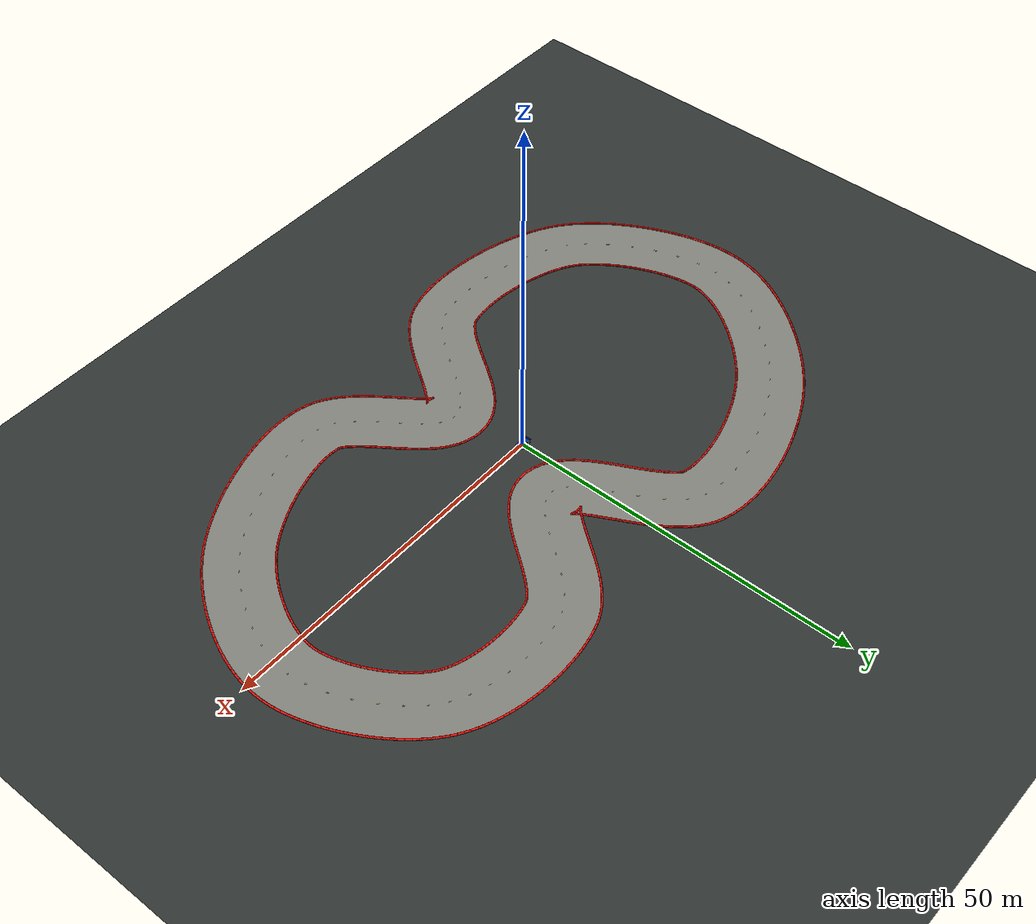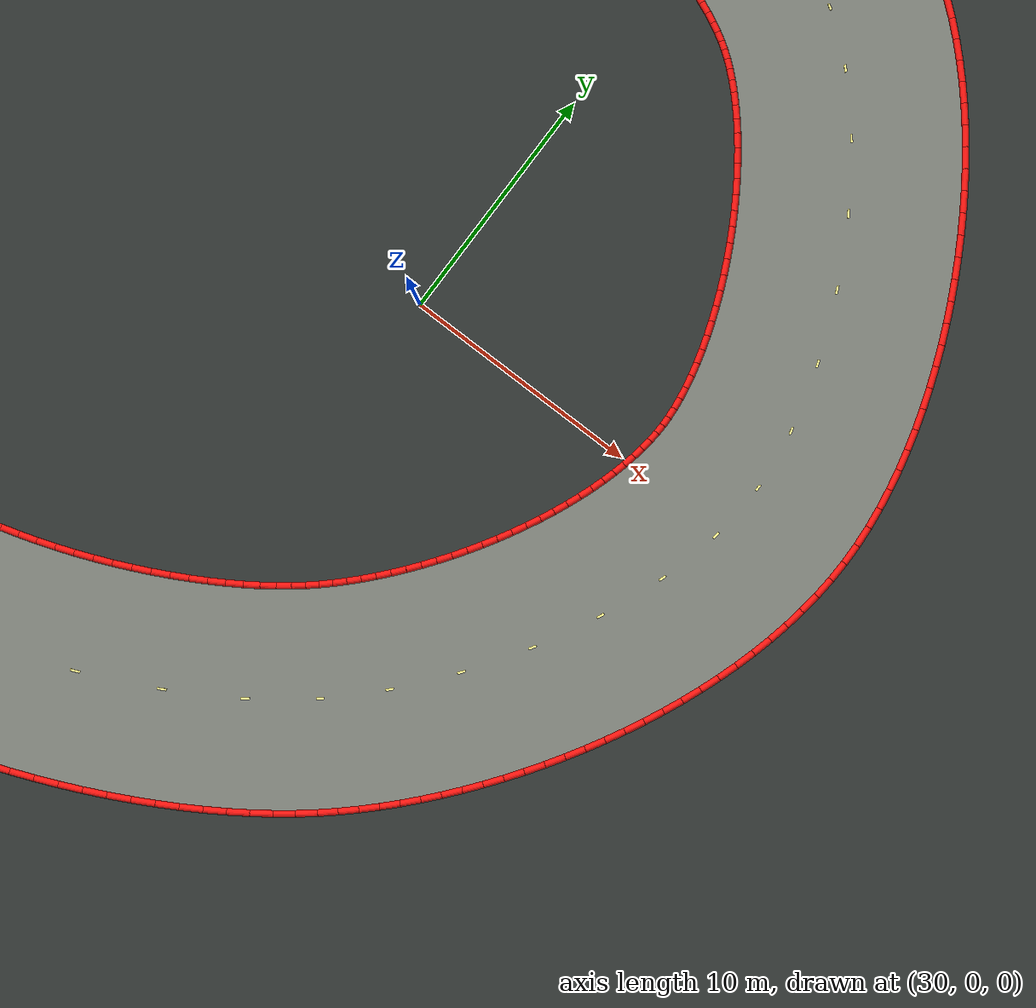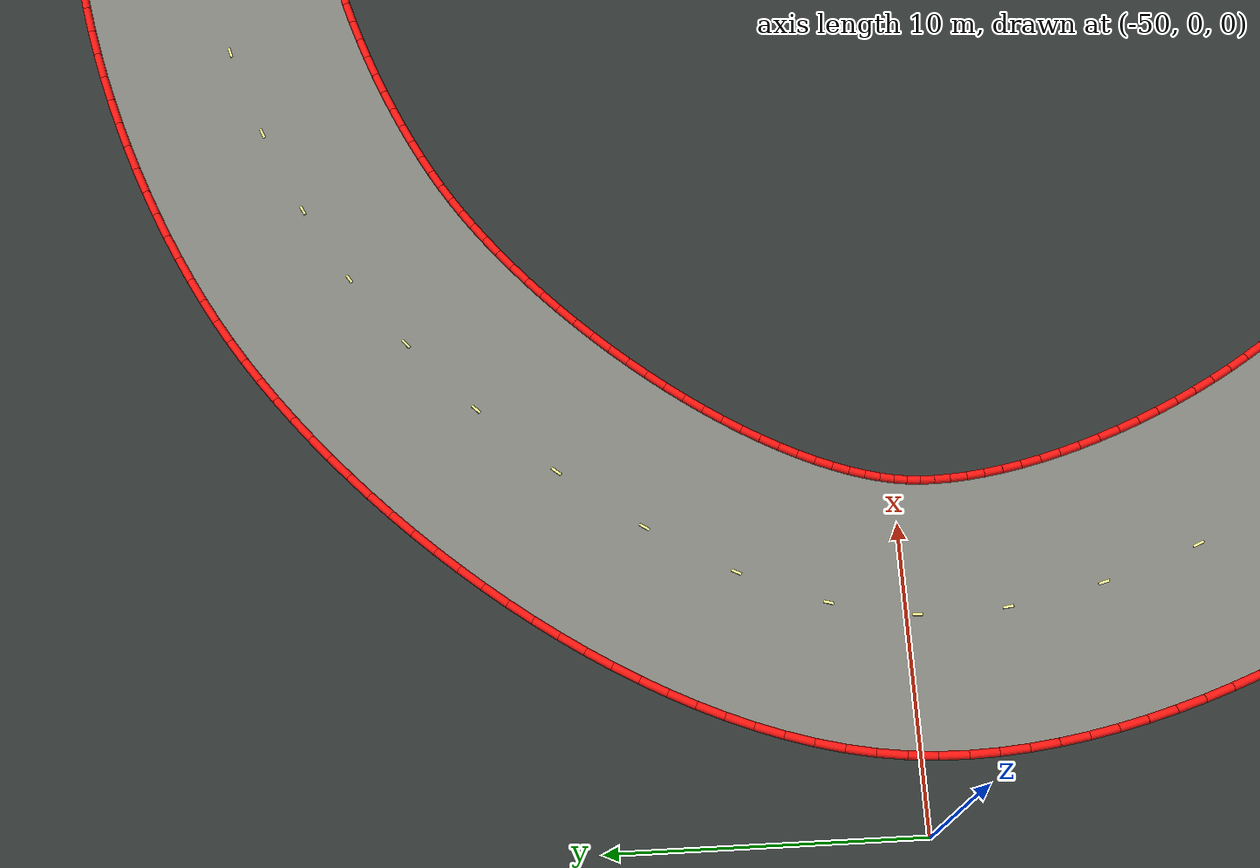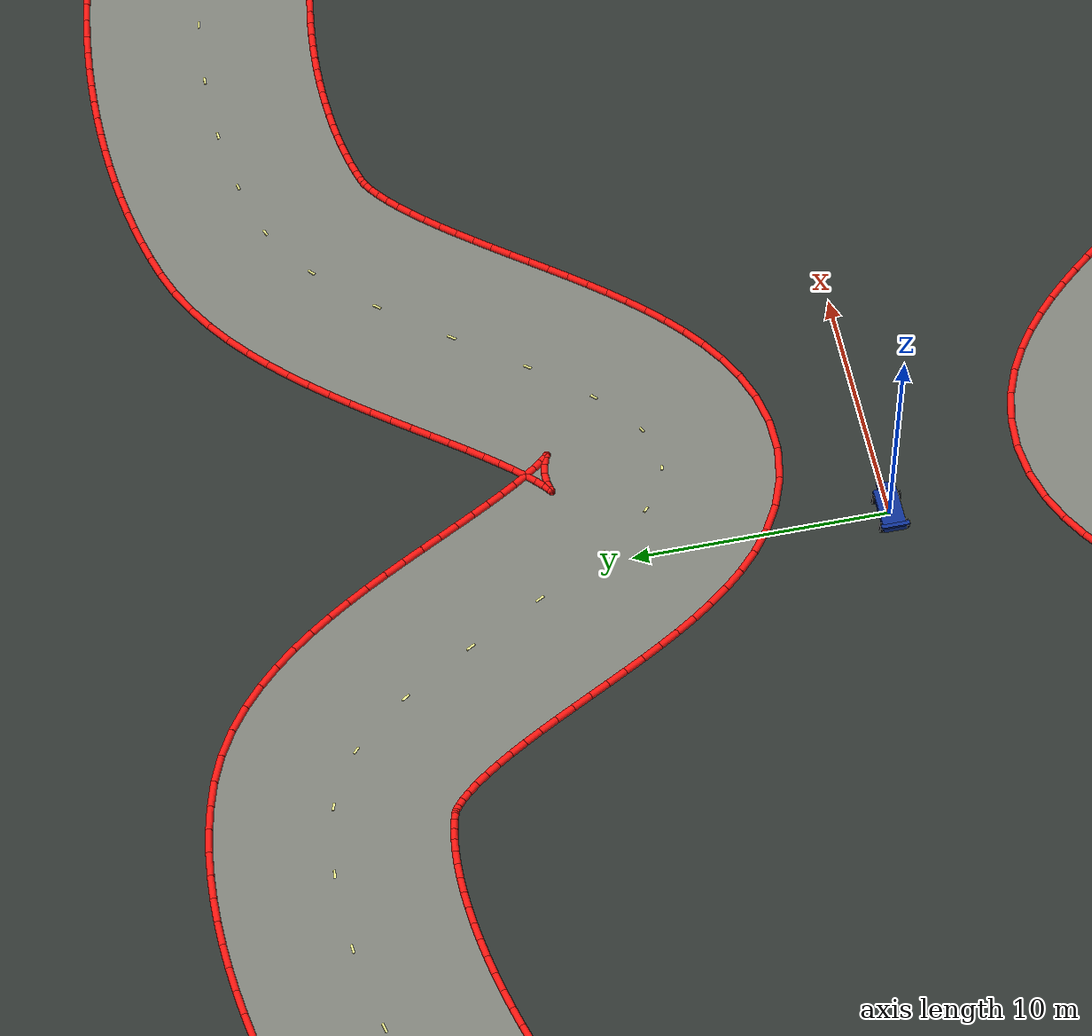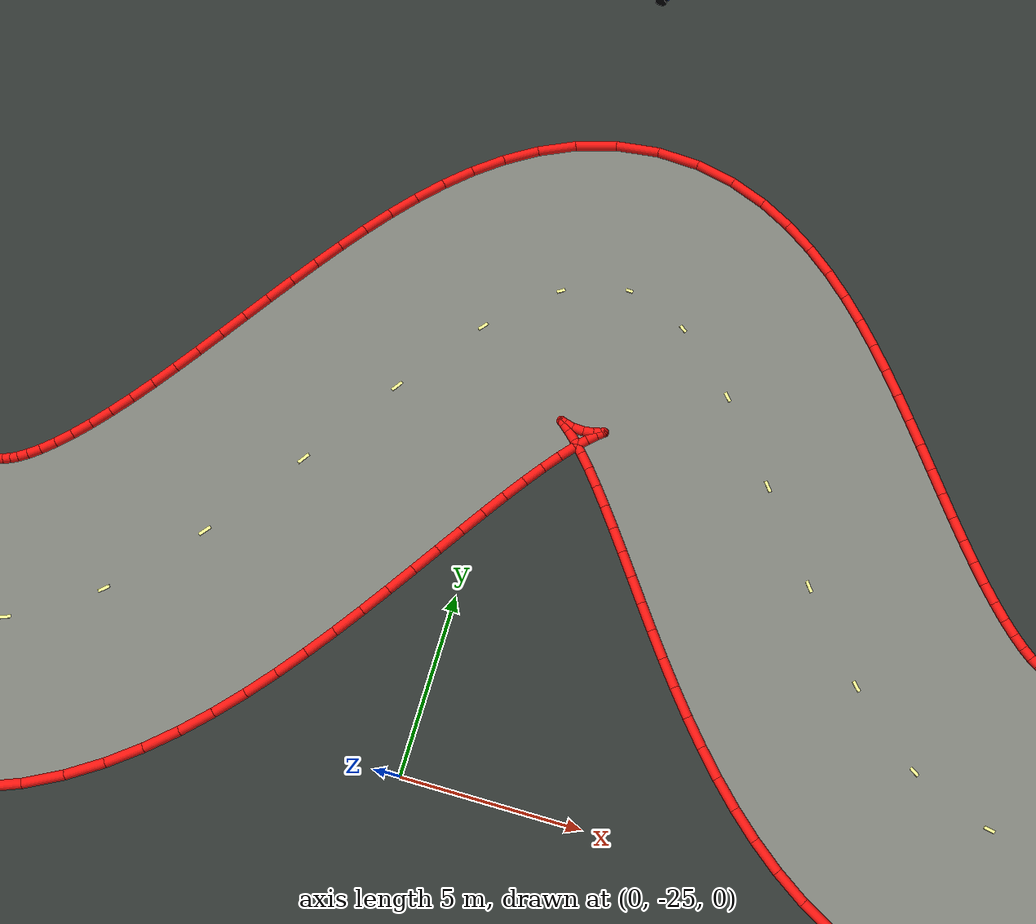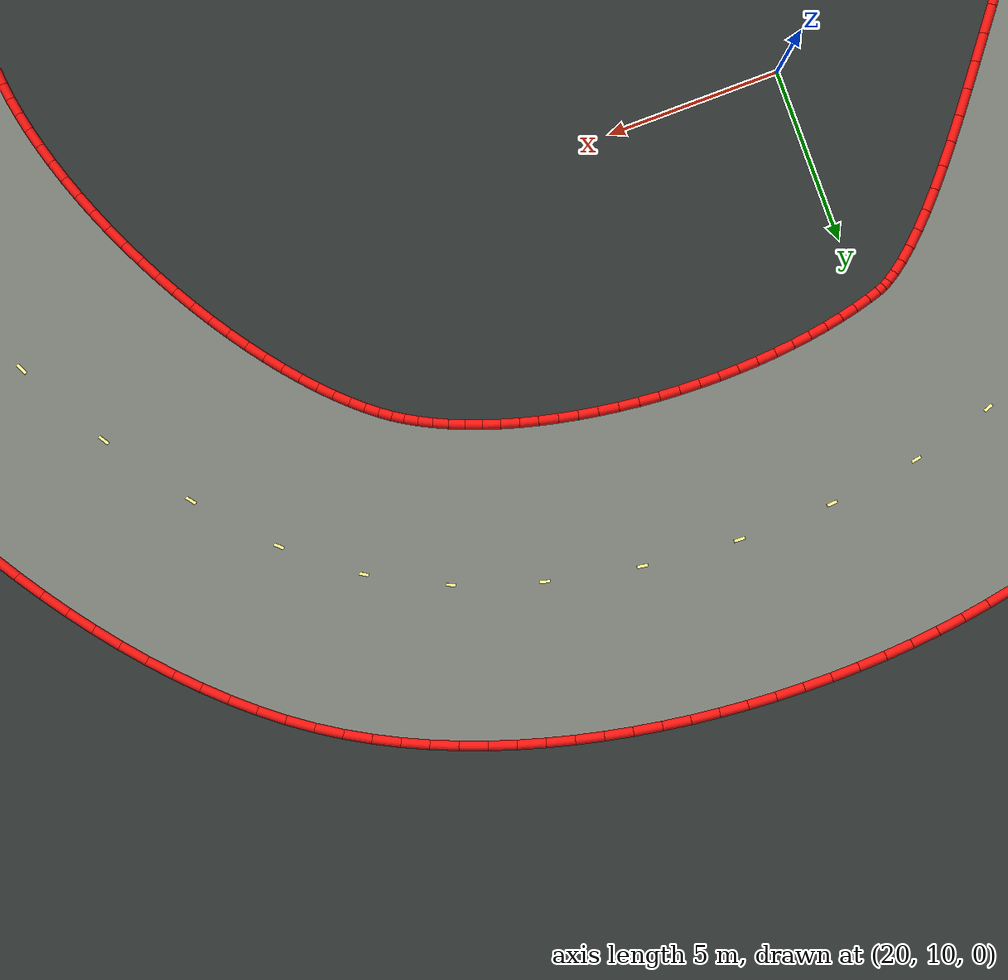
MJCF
<mujoco model="racesim_club_world">
  <compiler angle="degree" autolimits="true"/>
  <option timestep="0.02" gravity="0 0 -9.81"/>
  <visual>
    <global offwidth="1280" offheight="960"/>
    <headlight ambient="0.35 0.35 0.35" diffuse="0.8 0.8 0.8"/>
  </visual>

  <include file="car.xml"/>
  <include file="club_track.xml"/>

  <asset>
    <texture name="grid" type="2d" builtin="checker" width="512" height="512"
             rgb1="0.16 0.18 0.17" rgb2="0.20 0.22 0.21"/>
    <material name="ground" texture="grid" texrepeat="12 12" reflectance="0.05"/>
  </asset>

  <worldbody>
    <light name="sun" pos="0 0 30" dir="0 0 -1" diffuse="1.0 1.0 1.0" ambient="0.25 0.25 0.25"/>
    <geom name="ground" type="plane" size="90 90 0.1" material="ground"/>
    <camera name="topdown" pos="0 0 125" xyaxes="1 0 0 0 1 0" fovy="42"/>
    <camera name="follow" mode="trackcom" target="car" pos="-5 0 3" xyaxes="0 -1 0 0.5 0 0.866"/>
  </worldbody>
</mujoco>

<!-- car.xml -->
<mujoco model="simple_car">
  <default>
    <geom friction="1.2 0.02 0.001" density="600"/>
    <joint damping="0.1"/>
  </default>

  <asset>
    <material name="chassis_blue" rgba="0.05 0.18 0.55 1"/>
    <material name="wheel_dark" rgba="0.02 0.02 0.025 1"/>
  </asset>

  <worldbody>
    <body name="car" pos="0 0 0.28">
      <freejoint name="root"/>
      <geom name="chassis" type="box" size="0.9 0.45 0.12" material="chassis_blue"/>
      <geom name="nose" type="box" pos="0.75 0 0.02" size="0.45 0.25 0.06" material="chassis_blue"/>
      <geom name="rear_wing" type="box" pos="-0.85 0 0.22" size="0.08 0.55 0.04" material="chassis_blue"/>

      <body name="front_left_wheel" pos="0.65 0.48 -0.12">
        <joint name="front_left_spin" type="hinge" axis="0 1 0"/>
        <geom type="cylinder" size="0.18 0.08" euler="90 0 0" material="wheel_dark"/>
      </body>
      <body name="front_right_wheel" pos="0.65 -0.48 -0.12">
        <joint name="front_right_spin" type="hinge" axis="0 1 0"/>
        <geom type="cylinder" size="0.18 0.08" euler="90 0 0" material="wheel_dark"/>
      </body>
      <body name="rear_left_wheel" pos="-0.65 0.48 -0.12">
        <joint name="rear_left_spin" type="hinge" axis="0 1 0"/>
        <geom type="cylinder" size="0.18 0.08" euler="90 0 0" material="wheel_dark"/>
      </body>
      <body name="rear_right_wheel" pos="-0.65 -0.48 -0.12">
        <joint name="rear_right_spin" type="hinge" axis="0 1 0"/>
        <geom type="cylinder" size="0.18 0.08" euler="90 0 0" material="wheel_dark"/>
      </body>
    </body>
  </worldbody>
</mujoco>

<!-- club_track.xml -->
<mujoco model="club_track_visuals">
  <asset>
    <mesh name="track_surface_mesh" inertia="shell" vertex="40.50000 1.99916 0.02200 40.48950 2.38241 0.02200 40.45695 2.80035 0.02200 40.40082 3.25252 0.02200 40.32029 3.73440 0.02200 40.21509 4.24164 0.02200 40.08534 4.77015 0.02200 39.93150 5.31606 0.02200 39.75425 5.87570 0.02200 39.55447 6.44559 0.02200 39.33316 7.02240 0.02200 39.09147 7.60293 0.02200 38.83063 8.18412 0.02200 38.55196 8.76297 0.02200 38.25686 9.33656 0.02200 37.94683 9.90204 0.02200 37.62344 10.45660 0.02200 37.28835 10.99746 0.02200 36.94335 11.52186 0.02200 36.59034 12.02708 0.02200 36.23137 12.51040 0.02200 35.86868 12.96910 0.02200 35.50471 13.40053 0.02200 35.14219 13.80203 0.02200 34.78413 14.17105 0.02200 34.43396 14.50515 0.02200 34.09555 14.80207 0.02200 33.77327 15.05988 0.02200 33.46799 15.27993 0.02200 33.16785 15.47254 0.02200 32.83275 15.66492 0.02200 32.46350 15.85501 0.02200 32.06227 16.04044 0.02200 31.63142 16.21919 0.02200 31.17342 16.38954 0.02200 30.69084 16.55005 0.02200 30.18625 16.69953 0.02200 29.66225 16.83697 0.02200 29.12140 16.96155 0.02200 28.56629 17.07262 0.02200 27.99944 17.16962 0.02200 27.42340 17.25212 0.02200 26.84066 17.31978 0.02200 26.25375 17.37236 0.02200 25.66516 17.40968 0.02200 25.07740 17.43166 0.02200 24.49299 17.43828 0.02200 23.91447 17.42961 0.02200 23.34442 17.40579 0.02200 22.78544 17.36706 0.02200 22.24017 17.31378 0.02200 21.71133 17.24642 0.02200 21.20169 17.16559 0.02200 20.71406 17.07212 0.02200 20.25136 16.96702 0.02200 19.81653 16.85159 0.02200 19.49038 16.75397 0.02200 19.29530 16.67973 0.02200 19.11516 16.58374 0.02200 18.86832 16.42367 0.02200 18.56604 16.19438 0.02200 18.21963 15.89600 0.02200 17.83897 15.53208 0.02200 17.43202 15.10811 0.02200 17.00491 14.63057 0.02200 16.56222 14.10633 0.02200 16.10722 13.54231 0.02200 15.64218 12.94527 0.02200 15.16851 12.32174 0.02200 14.68691 11.67793 0.02200 14.19739 11.01972 0.02200 13.69937 10.35261 0.02200 13.19154 9.68168 0.02200 12.67176 9.01155 0.02200 12.13686 8.34640 0.02200 11.58227 7.68989 0.02200 11.00151 7.04531 0.02200 10.38544 6.41582 0.02200 9.72127 5.80517 0.02200 8.99148 5.21926 0.02200 8.17335 4.66926 0.02200 7.24075 4.17682 0.02200 6.17184 3.78058 0.02200 4.96563 3.53816 0.02200 3.65423 3.51330 0.02200 2.33732 3.74552 0.02200 1.14580 4.19744 0.02200 0.13279 4.78676 0.02200 -0.71646 5.44895 0.02200 -1.43578 6.14692 0.02200 -2.05883 6.86374 0.02200 -2.61229 7.59293 0.02200 -3.11558 8.33211 0.02200 -3.58241 9.07989 0.02200 -4.02247 9.83452 0.02200 -4.44270 10.59344 0.02200 -4.84810 11.35321 0.02200 -5.24236 12.10960 0.02200 -5.62819 12.85762 0.02200 -6.00749 13.59164 0.02200 -6.38148 14.30543 0.02200 -6.75070 14.99222 0.02200 -7.11497 15.64473 0.02200 -7.47321 16.25520 0.02200 -7.82325 16.81545 0.02200 -8.16151 17.31704 0.02200 -8.48256 17.75154 0.02200 -8.77867 18.11114 0.02200 -9.03939 18.38971 0.02200 -9.25174 18.58467 0.02200 -9.40149 18.69955 0.02200 -9.47697 18.74683 0.02200 -9.55512 18.77725 0.02200 -9.81982 18.85522 0.02200 -10.20772 18.94658 0.02200 -10.65020 19.02291 0.02200 -11.14329 19.08046 0.02200 -11.68250 19.11648 0.02200 -12.26319 19.12910 0.02200 -12.88071 19.11716 0.02200 -13.53054 19.08009 0.02200 -14.20831 19.01774 0.02200 -14.90983 18.93034 0.02200 -15.63109 18.81837 0.02200 -16.36823 18.68251 0.02200 -17.11753 18.52363 0.02200 -17.87542 18.34269 0.02200 -18.63841 18.14079 0.02200 -19.40309 17.91910 0.02200 -20.16612 17.67885 0.02200 -20.92423 17.42137 0.02200 -21.67416 17.14805 0.02200 -22.41268 16.86032 0.02200 -23.13656 16.55973 0.02200 -23.84256 16.24789 0.02200 -24.52741 15.92652 0.02200 -25.18780 15.59746 0.02200 -25.82037 15.26271 0.02200 -26.42165 14.92446 0.02200 -26.98810 14.58518 0.02200 -27.51893 14.24577 0.02200 -28.03494 13.89340 0.02200 -28.56367 13.51030 0.02200 -29.10135 13.09863 0.02200 -29.64497 12.66026 0.02200 -30.19170 12.19704 0.02200 -30.73890 11.71087 0.02200 -31.28401 11.20364 0.02200 -31.82459 10.67728 0.02200 -32.35829 10.13371 0.02200 -32.88280 9.57489 0.02200 -33.39589 9.00283 0.02200 -33.89537 8.41956 0.02200 -34.37910 7.82715 0.02200 -34.84499 7.22774 0.02200 -35.29098 6.62355 0.02200 -35.71507 6.01688 0.02200 -36.11531 5.41011 0.02200 -36.48982 4.80574 0.02200 -36.83682 4.20643 0.02200 -37.15463 3.61493 0.02200 -37.44172 3.03419 0.02200 -37.69678 2.46733 0.02200 -37.91871 1.91762 0.02200 -38.10679 1.38849 0.02200 -38.26069 0.88349 0.02200 -38.38062 0.40620 0.02200 -38.46744 -0.03991 0.02200 -38.52338 -0.45808 0.02200 -38.55348 -0.88429 0.02200 -38.56046 -1.35639 0.02200 -38.54196 -1.87043 0.02200 -38.49645 -2.42152 0.02200 -38.42307 -3.00483 0.02200 -38.32154 -3.61572 0.02200 -38.19198 -4.24975 0.02200 -38.03488 -4.90266 0.02200 -37.85096 -5.57040 0.02200 -37.64112 -6.24910 0.02200 -37.40645 -6.93501 0.02200 -37.14817 -7.62452 0.02200 -36.86757 -8.31415 0.02200 -36.56609 -9.00048 0.02200 -36.24523 -9.68016 0.02200 -35.90658 -10.34990 0.02200 -35.55185 -11.00645 0.02200 -35.18283 -11.64659 0.02200 -34.80145 -12.26712 0.02200 -34.40979 -12.86487 0.02200 -34.01006 -13.43664 0.02200 -33.60472 -13.97929 0.02200 -33.19644 -14.48967 0.02200 -32.78822 -14.96470 0.02200 -32.38339 -15.40136 0.02200 -31.98573 -15.79679 0.02200 -31.59955 -16.14836 0.02200 -31.22948 -16.45398 0.02200 -30.84227 -16.74013 0.02200 -30.40924 -17.02729 0.02200 -29.92850 -17.31513 0.02200 -29.40365 -17.60002 0.02200 -28.83843 -17.87890 0.02200 -28.23666 -18.14923 0.02200 -27.60216 -18.40888 0.02200 -26.93872 -18.65601 0.02200 -26.25011 -18.88911 0.02200 -25.54005 -19.10684 0.02200 -24.81221 -19.30806 0.02200 -24.07026 -19.49178 0.02200 -23.31781 -19.65715 0.02200 -22.55850 -19.80339 0.02200 -21.79594 -19.92988 0.02200 -21.03378 -20.03604 0.02200 -20.27569 -20.12143 0.02200 -19.52541 -20.18567 0.02200 -18.78674 -20.22852 0.02200 -18.06354 -20.24985 0.02200 -17.35982 -20.24971 0.02200 -16.67969 -20.22829 0.02200 -16.02743 -20.18606 0.02200 -15.40748 -20.12378 0.02200 -14.82445 -20.04261 0.02200 -14.28312 -19.94419 0.02200 -13.78840 -19.83087 0.02200 -13.41279 -19.72753 0.02200 -13.21967 -19.65700 0.02200 -13.04208 -19.56411 0.02200 -12.80310 -19.40930 0.02200 -12.51107 -19.18488 0.02200 -12.17609 -18.88887 0.02200 -11.80774 -18.52347 0.02200 -11.41409 -18.09350 0.02200 -11.00143 -17.60520 0.02200 -10.57447 -17.06550 0.02200 -10.13653 -16.48152 0.02200 -9.68979 -15.86032 0.02200 -9.23554 -15.20876 0.02200 -8.77424 -14.53339 0.02200 -8.30569 -13.84040 0.02200 -7.82901 -13.13559 0.02200 -7.34263 -12.42432 0.02200 -6.84417 -11.71148 0.02200 -6.33024 -11.00144 0.02200 -5.79617 -10.29808 0.02200 -5.23548 -9.60478 0.02200 -4.63925 -8.92474 0.02200 -3.99522 -8.26152 0.02200 -3.28677 -7.62046 0.02200 -2.49248 -7.01135 0.02200 -1.58737 -6.45302 0.02200 -0.54912 -5.97927 0.02200 0.62833 -5.64174 0.02200 1.90445 -5.50101 0.02200 3.15063 -5.58454 0.02200 4.30371 -5.85992 0.02200 5.32988 -6.27366 0.02200 6.22774 -6.77547 0.02200 7.01454 -7.32979 0.02200 7.71281 -7.91542 0.02200 8.34325 -8.52082 0.02200 8.92247 -9.13959 0.02200 9.46304 -9.76770 0.02200 9.97420 -10.40184 0.02200 10.46269 -11.03871 0.02200 10.93337 -11.67469 0.02200 11.38969 -12.30568 0.02200 11.83405 -12.92711 0.02200 12.26794 -13.53394 0.02200 12.69207 -14.12069 0.02200 13.10640 -14.68149 0.02200 13.51007 -15.21008 0.02200 13.90131 -15.69996 0.02200 14.27726 -16.14443 0.02200 14.63371 -16.53686 0.02200 14.96486 -16.87102 0.02200 15.26309 -17.14181 0.02200 15.51896 -17.34620 0.02200 15.72184 -17.48481 0.02200 15.86173 -17.56366 0.02200 15.93274 -17.59547 0.02200 16.01206 -17.61528 0.02200 16.29421 -17.66247 0.02200 16.69633 -17.70761 0.02200 17.15262 -17.73260 0.02200 17.65776 -17.73431 0.02200 18.20637 -17.71070 0.02200 18.79317 -17.66063 0.02200 19.41310 -17.58364 0.02200 20.06140 -17.47976 0.02200 20.73353 -17.34940 0.02200 21.42522 -17.19328 0.02200 22.13240 -17.01232 0.02200 22.85117 -16.80760 0.02200 23.57780 -16.58033 0.02200 24.30869 -16.33182 0.02200 25.04033 -16.06349 0.02200 25.76929 -15.77681 0.02200 26.49220 -15.47332 0.02200 27.20573 -15.15464 0.02200 27.90659 -14.82247 0.02200 28.59147 -14.47860 0.02200 29.25706 -14.12490 0.02200 29.90005 -13.76338 0.02200 30.51705 -13.39620 0.02200 31.10464 -13.02571 0.02200 31.65931 -12.65449 0.02200 32.17748 -12.28548 0.02200 32.65548 -11.92199 0.02200 33.09504 -11.56326 0.02200 33.48607 -11.22084 0.02200 33.88432 -10.84979 0.02200 34.28471 -10.45409 0.02200 34.68515 -10.03545 0.02200 35.08368 -9.59556 0.02200 35.47850 -9.13618 0.02200 35.86787 -8.65907 0.02200 36.25016 -8.16601 0.02200 36.62385 -7.65880 0.02200 36.98743 -7.13926 0.02200 37.33949 -6.60924 0.02200 37.67868 -6.07060 0.02200 38.00368 -5.52524 0.02200 38.31322 -4.97510 0.02200 38.60610 -4.42218 0.02200 38.88116 -3.86849 0.02200 39.13731 -3.31613 0.02200 39.37352 -2.76727 0.02200 39.58884 -2.22414 0.02200 39.78242 -1.68904 0.02200 39.95351 -1.16440 0.02200 40.10154 -0.65270 0.02200 40.22609 -0.15652 0.02200 40.32694 0.32147 0.02200 40.40419 0.77855 0.02200 40.45819 1.21199 0.02200 40.48974 1.61911 0.02200 49.50000 2.00084 0.02200 49.47732 2.85053 0.02200 49.41186 3.70007 0.02200 49.30742 4.54576 0.02200 49.16707 5.38800 0.02200 48.99338 6.22698 0.02200 48.78847 7.06265 0.02200 48.55417 7.89474 0.02200 48.29206 8.72277 0.02200 48.00355 9.54608 0.02200 47.68988 10.36385 0.02200 47.35219 11.17513 0.02200 46.99151 11.97885 0.02200 46.60880 12.77385 0.02200 46.20492 13.55892 0.02200 45.78066 14.33275 0.02200 45.33669 15.09402 0.02200 44.87364 15.84136 0.02200 44.39199 16.57338 0.02200 43.89211 17.28866 0.02200 43.37421 17.98579 0.02200 42.83833 18.66331 0.02200 42.28429 19.31976 0.02200 41.71165 19.95363 0.02200 41.11964 20.56334 0.02200 40.50713 21.14719 0.02200 39.87251 21.70328 0.02200 39.21367 22.22940 0.02200 38.53201 22.72007 0.02200 37.84425 23.16223 0.02200 37.13755 23.56863 0.02200 36.41478 23.94126 0.02200 35.67745 24.28244 0.02200 34.92687 24.59415 0.02200 34.16423 24.87807 0.02200 33.39065 25.13556 0.02200 32.60722 25.36780 0.02200 31.81502 25.57570 0.02200 31.01515 25.76006 0.02200 30.20872 25.92148 0.02200 29.39686 26.06047 0.02200 28.58071 26.17740 0.02200 27.76143 26.27255 0.02200 26.94018 26.34614 0.02200 26.11815 26.39827 0.02200 25.29648 26.42899 0.02200 24.47633 26.43827 0.02200 23.65885 26.42598 0.02200 22.84512 26.39193 0.02200 22.03621 26.33582 0.02200 21.23316 26.25726 0.02200 20.43692 26.15573 0.02200 19.64839 26.03054 0.02200 18.86843 25.88085 0.02200 18.09781 25.70557 0.02200 17.33725 25.50336 0.02200 16.50962 25.24603 0.02200 15.55119 24.86396 0.02200 14.59516 24.36639 0.02200 13.72246 23.80745 0.02200 12.92118 23.20406 0.02200 12.17928 22.56790 0.02200 11.48622 21.90724 0.02200 10.83335 21.22836 0.02200 10.21384 20.53661 0.02200 9.62243 19.83690 0.02200 9.05516 19.13413 0.02200 8.50907 18.43332 0.02200 7.98206 17.73976 0.02200 7.47276 17.05903 0.02200 6.98044 16.39705 0.02200 6.50502 15.76013 0.02200 6.04712 15.15499 0.02200 5.60817 14.58880 0.02200 5.19067 14.06920 0.02200 4.79849 13.60431 0.02200 4.43743 13.20265 0.02200 4.11594 12.87286 0.02200 3.84614 12.62300 0.02200 3.64483 12.45897 0.02200 3.53406 12.38139 0.02200 3.53926 12.38042 0.02200 3.68160 12.42921 0.02200 3.96136 12.48195 0.02200 4.34577 12.48670 0.02200 4.74756 12.41677 0.02200 5.05196 12.30558 0.02200 5.20311 12.22261 0.02200 5.21303 12.21956 0.02200 5.11282 12.32073 0.02200 4.93340 12.53020 0.02200 4.69872 12.84166 0.02200 4.42544 13.24464 0.02200 4.12457 13.72774 0.02200 3.80305 14.27988 0.02200 3.46507 14.89080 0.02200 3.11291 15.55111 0.02200 2.74754 16.25224 0.02200 2.36890 16.98636 0.02200 1.97618 17.74628 0.02200 1.56785 18.52540 0.02200 1.14172 19.31767 0.02200 0.69488 20.11757 0.02200 0.22350 20.92003 0.02200 -0.27730 21.72041 0.02200 -0.81385 22.51434 0.02200 -1.39432 23.29742 0.02200 -2.02918 24.06466 0.02200 -2.73159 24.80934 0.02200 -3.51729 25.52125 0.02200 -4.40323 26.18403 0.02200 -5.40383 26.77239 0.02200 -6.44488 27.22275 0.02200 -7.45187 27.53812 0.02200 -8.40119 27.76340 0.02200 -9.35644 27.92943 0.02200 -10.31662 28.04242 0.02200 -11.28120 28.10753 0.02200 -12.24983 28.12909 0.02200 -13.22216 28.11068 0.02200 -14.19772 28.05532 0.02200 -15.17587 27.96558 0.02200 -16.15580 27.84368 0.02200 -17.13654 27.69156 0.02200 -18.11693 27.51099 0.02200 -19.09569 27.30354 0.02200 -20.07141 27.07068 0.02200 -21.04257 26.81374 0.02200 -22.00759 26.53400 0.02200 -22.96480 26.23265 0.02200 -23.91248 25.91080 0.02200 -24.84888 25.56952 0.02200 -25.77225 25.20977 0.02200 -26.68081 24.83248 0.02200 -27.57280 24.43845 0.02200 -28.44650 24.02842 0.02200 -29.30021 23.60296 0.02200 -30.13230 23.16253 0.02200 -30.94124 22.70735 0.02200 -31.72556 22.23740 0.02200 -32.48107 21.75423 0.02200 -33.21274 21.25481 0.02200 -33.93964 20.72826 0.02200 -34.66189 20.17538 0.02200 -35.37887 19.59729 0.02200 -36.08973 18.99507 0.02200 -36.79351 18.36982 0.02200 -37.48910 17.72260 0.02200 -38.17529 17.05447 0.02200 -38.85082 16.36645 0.02200 -39.51431 15.65955 0.02200 -40.16438 14.93474 0.02200 -40.79955 14.19296 0.02200 -41.41834 13.43511 0.02200 -42.01918 12.66199 0.02200 -42.60049 11.87437 0.02200 -43.16063 11.07293 0.02200 -43.69790 10.25823 0.02200 -44.21053 9.43075 0.02200 -44.69666 8.59081 0.02200 -45.15433 7.73860 0.02200 -45.58142 6.87415 0.02200 -45.97561 5.99733 0.02200 -46.33434 5.10781 0.02200 -46.65469 4.20513 0.02200 -46.93334 3.28871 0.02200 -47.16644 2.35795 0.02200 -47.34950 1.41234 0.02200 -47.47662 0.45808 0.02200 -47.54502 -0.49404 0.02200 -47.56000 -1.44678 0.02200 -47.52642 -2.39916 0.02200 -47.44831 -3.35113 0.02200 -47.32901 -4.30258 0.02200 -47.17132 -5.25321 0.02200 -46.97758 -6.20254 0.02200 -46.74982 -7.14986 0.02200 -46.48981 -8.09431 0.02200 -46.19914 -9.03482 0.02200 -45.87921 -9.97019 0.02200 -45.53132 -10.89908 0.02200 -45.15664 -11.82007 0.02200 -44.75624 -12.73163 0.02200 -44.33112 -13.63215 0.02200 -43.88218 -14.52001 0.02200 -43.41020 -15.39350 0.02200 -42.91589 -16.25091 0.02200 -42.39981 -17.09051 0.02200 -41.86238 -17.91054 0.02200 -41.30388 -18.70923 0.02200 -40.72435 -19.48482 0.02200 -40.12360 -20.23549 0.02200 -39.50115 -20.95941 0.02200 -38.85614 -21.65464 0.02200 -38.18729 -22.31911 0.02200 -37.49281 -22.95053 0.02200 -36.77052 -23.54602 0.02200 -36.00816 -24.10991 0.02200 -35.21225 -24.63853 0.02200 -34.39023 -25.13133 0.02200 -33.54407 -25.59107 0.02200 -32.67556 -26.01994 0.02200 -31.78644 -26.41960 0.02200 -30.87846 -26.79135 0.02200 -29.95335 -27.13611 0.02200 -29.01291 -27.45456 0.02200 -28.05897 -27.74715 0.02200 -27.09341 -28.01416 0.02200 -26.11812 -28.25570 0.02200 -25.13503 -28.47178 0.02200 -24.14607 -28.66227 0.02200 -23.15316 -28.82695 0.02200 -22.15822 -28.96552 0.02200 -21.16311 -29.07757 0.02200 -20.16967 -29.16258 0.02200 -19.17964 -29.21994 0.02200 -18.19471 -29.24890 0.02200 -17.21642 -29.24856 0.02200 -16.24621 -29.21784 0.02200 -15.28536 -29.15542 0.02200 -14.33499 -29.05965 0.02200 -13.39603 -28.92853 0.02200 -12.46924 -28.75951 0.02200 -11.55529 -28.54942 0.02200 -10.58721 -28.27247 0.02200 -9.56423 -27.88122 0.02200 -8.55653 -27.36666 0.02200 -7.63929 -26.78053 0.02200 -6.80250 -26.14277 0.02200 -6.03433 -25.46753 0.02200 -5.32350 -24.76484 0.02200 -4.66024 -24.04208 0.02200 -4.03654 -23.30523 0.02200 -3.44599 -22.55957 0.02200 -2.88357 -21.81018 0.02200 -2.34538 -21.06220 0.02200 -1.82845 -20.32100 0.02200 -1.33058 -19.59223 0.02200 -0.85028 -18.88190 0.02200 -0.38672 -18.19644 0.02200 0.06023 -17.54268 0.02200 0.48990 -16.92794 0.02200 0.90061 -16.36007 0.02200 1.28938 -15.84740 0.02200 1.65146 -15.39874 0.02200 1.97963 -15.02313 0.02200 2.26332 -14.72919 0.02200 2.48764 -14.52380 0.02200 2.63285 -14.40939 0.02200 2.67571 -14.37931 0.02200 2.59558 -14.41200 0.02200 2.38811 -14.46802 0.02200 2.09555 -14.49899 0.02200 1.77879 -14.47938 0.02200 1.54161 -14.42560 0.02200 1.41940 -14.37972 0.02200 1.41507 -14.38062 0.02200 1.51295 -14.45246 0.02200 1.69205 -14.60500 0.02200 1.93323 -14.83839 0.02200 2.22143 -15.14760 0.02200 2.54563 -15.52525 0.02200 2.89813 -15.96324 0.02200 3.27377 -16.45345 0.02200 3.66922 -16.98809 0.02200 4.08259 -17.55984 0.02200 4.51303 -18.16187 0.02200 4.96060 -18.78779 0.02200 5.42615 -19.43167 0.02200 5.91127 -20.08797 0.02200 6.41836 -20.75153 0.02200 6.95074 -21.41745 0.02200 7.51285 -22.08099 0.02200 8.11043 -22.73740 0.02200 8.75083 -23.38146 0.02200 9.44324 -24.00689 0.02200 10.19864 -24.60528 0.02200 11.02920 -25.16460 0.02200 11.94649 -25.66742 0.02200 12.95795 -26.08962 0.02200 13.98794 -26.38472 0.02200 14.99375 -26.56802 0.02200 15.93927 -26.67571 0.02200 16.88522 -26.72863 0.02200 17.83185 -26.73262 0.02200 18.77948 -26.69243 0.02200 19.72831 -26.61192 0.02200 20.67830 -26.49427 0.02200 21.62917 -26.34215 0.02200 22.58037 -26.15787 0.02200 23.53110 -25.94344 0.02200 24.48036 -25.70065 0.02200 25.42697 -25.43112 0.02200 26.36958 -25.13637 0.02200 27.30673 -24.81780 0.02200 28.23685 -24.47671 0.02200 29.15830 -24.11435 0.02200 30.06937 -23.73187 0.02200 30.96832 -23.33039 0.02200 31.85336 -22.91092 0.02200 32.72274 -22.47439 0.02200 33.57467 -22.02163 0.02200 34.40742 -21.55335 0.02200 35.21928 -21.07012 0.02200 36.00861 -20.57230 0.02200 36.77384 -20.06001 0.02200 37.51347 -19.53304 0.02200 38.22611 -18.99080 0.02200 38.90496 -18.43674 0.02200 39.51781 -17.90052 0.02200 40.11517 -17.34413 0.02200 40.69997 -16.76633 0.02200 41.27219 -16.16821 0.02200 41.83165 -15.55081 0.02200 42.37802 -14.91516 0.02200 42.91091 -14.26224 0.02200 43.42981 -13.59304 0.02200 43.93414 -12.90852 0.02200 44.42324 -12.20963 0.02200 44.89641 -11.49728 0.02200 45.35287 -10.77238 0.02200 45.79182 -10.03577 0.02200 46.21236 -9.28828 0.02200 46.61360 -8.53069 0.02200 46.99455 -7.76374 0.02200 47.35417 -6.98809 0.02200 47.69137 -6.20434 0.02200 48.00496 -5.41302 0.02200 48.29366 -4.61458 0.02200 48.55608 -3.80937 0.02200 48.79068 -2.99767 0.02200 48.99575 -2.17965 0.02200 49.16935 -1.35541 0.02200 49.30928 -0.52500 0.02200 49.41304 0.31155 0.02200 49.47772 1.15417 0.02200" face="0 337 1 0 336 337 1 338 2 1 337 338 2 339 3 2 338 339 3 340 4 3 339 340 4 341 5 4 340 341 5 342 6 5 341 342 6 343 7 6 342 343 7 344 8 7 343 344 8 345 9 8 344 345 9 346 10 9 345 346 10 347 11 10 346 347 11 348 12 11 347 348 12 349 13 12 348 349 13 350 14 13 349 350 14 351 15 14 350 351 15 352 16 15 351 352 16 353 17 16 352 353 17 354 18 17 353 354 18 355 19 18 354 355 19 356 20 19 355 356 20 357 21 20 356 357 21 358 22 21 357 358 22 359 23 22 358 359 23 360 24 23 359 360 24 361 25 24 360 361 25 362 26 25 361 362 26 363 27 26 362 363 27 364 28 27 363 364 28 365 29 28 364 365 29 366 30 29 365 366 30 367 31 30 366 367 31 368 32 31 367 368 32 369 33 32 368 369 33 370 34 33 369 370 34 371 35 34 370 371 35 372 36 35 371 372 36 373 37 36 372 373 37 374 38 37 373 374 38 375 39 38 374 375 39 376 40 39 375 376 40 377 41 40 376 377 41 378 42 41 377 378 42 379 43 42 378 379 43 380 44 43 379 380 44 381 45 44 380 381 45 382 46 45 381 382 46 383 47 46 382 383 47 384 48 47 383 384 48 385 49 48 384 385 49 386 50 49 385 386 50 387 51 50 386 387 51 388 52 51 387 388 52 389 53 52 388 389 53 390 54 53 389 390 54 391 55 54 390 391 55 392 56 55 391 392 56 393 57 56 392 393 57 394 58 57 393 394 58 395 59 58 394 395 59 396 60 59 395 396 60 397 61 60 396 397 61 398 62 61 397 398 62 399 63 62 398 399 63 400 64 63 399 400 64 401 65 64 400 401 65 402 66 65 401 402 66 403 67 66 402 403 67 404 68 67 403 404 68 405 69 68 404 405 69 406 70 69 405 406 70 407 71 70 406 407 71 408 72 71 407 408 72 409 73 72 408 409 73 410 74 73 409 410 74 411 75 74 410 411 75 412 76 75 411 412 76 413 77 76 412 413 77 414 78 77 413 414 78 415 79 78 414 415 79 416 80 79 415 416 80 417 81 80 416 417 81 418 82 81 417 418 82 419 83 82 418 419 83 420 84 83 419 420 84 421 85 84 420 421 85 422 86 85 421 422 86 423 87 86 422 423 87 424 88 87 423 424 88 425 89 88 424 425 89 426 90 89 425 426 90 427 91 90 426 427 91 428 92 91 427 428 92 429 93 92 428 429 93 430 94 93 429 430 94 431 95 94 430 431 95 432 96 95 431 432 96 433 97 96 432 433 97 434 98 97 433 434 98 435 99 98 434 435 99 436 100 99 435 436 100 437 101 100 436 437 101 438 102 101 437 438 102 439 103 102 438 439 103 440 104 103 439 440 104 441 105 104 440 441 105 442 106 105 441 442 106 443 107 106 442 443 107 444 108 107 443 444 108 445 109 108 444 445 109 446 110 109 445 446 110 447 111 110 446 447 111 448 112 111 447 448 112 449 113 112 448 449 113 450 114 113 449 450 114 451 115 114 450 451 115 452 116 115 451 452 116 453 117 116 452 453 117 454 118 117 453 454 118 455 119 118 454 455 119 456 120 119 455 456 120 457 121 120 456 457 121 458 122 121 457 458 122 459 123 122 458 459 123 460 124 123 459 460 124 461 125 124 460 461 125 462 126 125 461 462 126 463 127 126 462 463 127 464 128 127 463 464 128 465 129 128 464 465 129 466 130 129 465 466 130 467 131 130 466 467 131 468 132 131 467 468 132 469 133 132 468 469 133 470 134 133 469 470 134 471 135 134 470 471 135 472 136 135 471 472 136 473 137 136 472 473 137 474 138 137 473 474 138 475 139 138 474 475 139 476 140 139 475 476 140 477 141 140 476 477 141 478 142 141 477 478 142 479 143 142 478 479 143 480 144 143 479 480 144 481 145 144 480 481 145 482 146 145 481 482 146 483 147 146 482 483 147 484 148 147 483 484 148 485 149 148 484 485 149 486 150 149 485 486 150 487 151 150 486 487 151 488 152 151 487 488 152 489 153 152 488 489 153 490 154 153 489 490 154 491 155 154 490 491 155 492 156 155 491 492 156 493 157 156 492 493 157 494 158 157 493 494 158 495 159 158 494 495 159 496 160 159 495 496 160 497 161 160 496 497 161 498 162 161 497 498 162 499 163 162 498 499 163 500 164 163 499 500 164 501 165 164 500 501 165 502 166 165 501 502 166 503 167 166 502 503 167 504 168 167 503 504 168 505 169 168 504 505 169 506 170 169 505 506 170 507 171 170 506 507 171 508 172 171 507 508 172 509 173 172 508 509 173 510 174 173 509 510 174 511 175 174 510 511 175 512 176 175 511 512 176 513 177 176 512 513 177 514 178 177 513 514 178 515 179 178 514 515 179 516 180 179 515 516 180 517 181 180 516 517 181 518 182 181 517 518 182 519 183 182 518 519 183 520 184 183 519 520 184 521 185 184 520 521 185 522 186 185 521 522 186 523 187 186 522 523 187 524 188 187 523 524 188 525 189 188 524 525 189 526 190 189 525 526 190 527 191 190 526 527 191 528 192 191 527 528 192 529 193 192 528 529 193 530 194 193 529 530 194 531 195 194 530 531 195 532 196 195 531 532 196 533 197 196 532 533 197 534 198 197 533 534 198 535 199 198 534 535 199 536 200 199 535 536 200 537 201 200 536 537 201 538 202 201 537 538 202 539 203 202 538 539 203 540 204 203 539 540 204 541 205 204 540 541 205 542 206 205 541 542 206 543 207 206 542 543 207 544 208 207 543 544 208 545 209 208 544 545 209 546 210 209 545 546 210 547 211 210 546 547 211 548 212 211 547 548 212 549 213 212 548 549 213 550 214 213 549 550 214 551 215 214 550 551 215 552 216 215 551 552 216 553 217 216 552 553 217 554 218 217 553 554 218 555 219 218 554 555 219 556 220 219 555 556 220 557 221 220 556 557 221 558 222 221 557 558 222 559 223 222 558 559 223 560 224 223 559 560 224 561 225 224 560 561 225 562 226 225 561 562 226 563 227 226 562 563 227 564 228 227 563 564 228 565 229 228 564 565 229 566 230 229 565 566 230 567 231 230 566 567 231 568 232 231 567 568 232 569 233 232 568 569 233 570 234 233 569 570 234 571 235 234 570 571 235 572 236 235 571 572 236 573 237 236 572 573 237 574 238 237 573 574 238 575 239 238 574 575 239 576 240 239 575 576 240 577 241 240 576 577 241 578 242 241 577 578 242 579 243 242 578 579 243 580 244 243 579 580 244 581 245 244 580 581 245 582 246 245 581 582 246 583 247 246 582 583 247 584 248 247 583 584 248 585 249 248 584 585 249 586 250 249 585 586 250 587 251 250 586 587 251 588 252 251 587 588 252 589 253 252 588 589 253 590 254 253 589 590 254 591 255 254 590 591 255 592 256 255 591 592 256 593 257 256 592 593 257 594 258 257 593 594 258 595 259 258 594 595 259 596 260 259 595 596 260 597 261 260 596 597 261 598 262 261 597 598 262 599 263 262 598 599 263 600 264 263 599 600 264 601 265 264 600 601 265 602 266 265 601 602 266 603 267 266 602 603 267 604 268 267 603 604 268 605 269 268 604 605 269 606 270 269 605 606 270 607 271 270 606 607 271 608 272 271 607 608 272 609 273 272 608 609 273 610 274 273 609 610 274 611 275 274 610 611 275 612 276 275 611 612 276 613 277 276 612 613 277 614 278 277 613 614 278 615 279 278 614 615 279 616 280 279 615 616 280 617 281 280 616 617 281 618 282 281 617 618 282 619 283 282 618 619 283 620 284 283 619 620 284 621 285 284 620 621 285 622 286 285 621 622 286 623 287 286 622 623 287 624 288 287 623 624 288 625 289 288 624 625 289 626 290 289 625 626 290 627 291 290 626 627 291 628 292 291 627 628 292 629 293 292 628 629 293 630 294 293 629 630 294 631 295 294 630 631 295 632 296 295 631 632 296 633 297 296 632 633 297 634 298 297 633 634 298 635 299 298 634 635 299 636 300 299 635 636 300 637 301 300 636 637 301 638 302 301 637 638 302 639 303 302 638 639 303 640 304 303 639 640 304 641 305 304 640 641 305 642 306 305 641 642 306 643 307 306 642 643 307 644 308 307 643 644 308 645 309 308 644 645 309 646 310 309 645 646 310 647 311 310 646 647 311 648 312 311 647 648 312 649 313 312 648 649 313 650 314 313 649 650 314 651 315 314 650 651 315 652 316 315 651 652 316 653 317 316 652 653 317 654 318 317 653 654 318 655 319 318 654 655 319 656 320 319 655 656 320 657 321 320 656 657 321 658 322 321 657 658 322 659 323 322 658 659 323 660 324 323 659 660 324 661 325 324 660 661 325 662 326 325 661 662 326 663 327 326 662 663 327 664 328 327 663 664 328 665 329 328 664 665 329 666 330 329 665 666 330 667 331 330 666 667 331 668 332 331 667 668 332 669 333 332 668 669 333 670 334 333 669 670 334 671 335 334 670 671 335 336 0 335 671 336"/>
    <material name="track_asphalt" rgba="0.48 0.49 0.46 1" emission="0.08"/>
    <material name="track_boundary" rgba="0.95 0.08 0.06 1" emission="0.05"/>
    <material name="track_centerline" rgba="1.0 0.95 0.55 1" emission="0.15"/>
  </asset>
  <worldbody>
    <geom name="track_surface" type="mesh" mesh="track_surface_mesh" material="track_asphalt" contype="0" conaffinity="0"/>
    <geom name="track_left_boundary_000" type="capsule" fromto="40.50000 1.99916 0.09 40.48950 2.38241 0.09" size="0.14" material="track_boundary" contype="0" conaffinity="0"/>
    <geom name="track_left_boundary_001" type="capsule" fromto="40.48950 2.38241 0.09 40.45695 2.80035 0.09" size="0.14" material="track_boundary" contype="0" conaffinity="0"/>
    <geom name="track_left_boundary_002" type="capsule" fromto="40.45695 2.80035 0.09 40.40082 3.25252 0.09" size="0.14" material="track_boundary" contype="0" conaffinity="0"/>
    <geom name="track_left_boundary_003" type="capsule" fromto="40.40082 3.25252 0.09 40.32029 3.73440 0.09" size="0.14" material="track_boundary" contype="0" conaffinity="0"/>
    <geom name="track_left_boundary_004" type="capsule" fromto="40.32029 3.73440 0.09 40.21509 4.24164 0.09" size="0.14" material="track_boundary" contype="0" conaffinity="0"/>
    <geom name="track_left_boundary_005" type="capsule" fromto="40.21509 4.24164 0.09 40.08534 4.77015 0.09" size="0.14" material="track_boundary" contype="0" conaffinity="0"/>
    <geom name="track_left_boundary_006" type="capsule" fromto="40.08534 4.77015 0.09 39.93150 5.31606 0.09" size="0.14" material="track_boundary" contype="0" conaffinity="0"/>
    <geom name="track_left_boundary_007" type="capsule" fromto="39.93150 5.31606 0.09 39.75425 5.87570 0.09" size="0.14" material="track_boundary" contype="0" conaffinity="0"/>
    <geom name="track_left_boundary_008" type="capsule" fromto="39.75425 5.87570 0.09 39.55447 6.44559 0.09" size="0.14" material="track_boundary" contype="0" conaffinity="0"/>
    <geom name="track_left_boundary_009" type="capsule" fromto="39.55447 6.44559 0.09 39.33316 7.02240 0.09" size="0.14" material="track_boundary" contype="0" conaffinity="0"/>
    <geom name="track_left_boundary_010" type="capsule" fromto="39.33316 7.02240 0.09 39.09147 7.60293 0.09" size="0.14" material="track_boundary" contype="0" conaffinity="0"/>
    <geom name="track_left_boundary_011" type="capsule" fromto="39.09147 7.60293 0.09 38.83063 8.18412 0.09" size="0.14" material="track_boundary" contype="0" conaffinity="0"/>
    <geom name="track_left_boundary_012" type="capsule" fromto="38.83063 8.18412 0.09 38.55196 8.76297 0.09" size="0.14" material="track_boundary" contype="0" conaffinity="0"/>
    <geom name="track_left_boundary_013" type="capsule" fromto="38.55196 8.76297 0.09 38.25686 9.33656 0.09" size="0.14" material="track_boundary" contype="0" conaffinity="0"/>
    <geom name="track_left_boundary_014" type="capsule" fromto="38.25686 9.33656 0.09 37.94683 9.90204 0.09" size="0.14" material="track_boundary" contype="0" conaffinity="0"/>
    <geom name="track_left_boundary_015" type="capsule" fromto="37.94683 9.90204 0.09 37.62344 10.45660 0.09" size="0.14" material="track_boundary" contype="0" conaffinity="0"/>
    <geom name="track_left_boundary_016" type="capsule" fromto="37.62344 10.45660 0.09 37.28835 10.99746 0.09" size="0.14" material="track_boundary" contype="0" conaffinity="0"/>
    <geom name="track_left_boundary_017" type="capsule" fromto="37.28835 10.99746 0.09 36.94335 11.52186 0.09" size="0.14" material="track_boundary" contype="0" conaffinity="0"/>
    <geom name="track_left_boundary_018" type="capsule" fromto="36.94335 11.52186 0.09 36.59034 12.02708 0.09" size="0.14" material="track_boundary" contype="0" conaffinity="0"/>
    <geom name="track_left_boundary_019" type="capsule" fromto="36.59034 12.02708 0.09 36.23137 12.51040 0.09" size="0.14" material="track_boundary" contype="0" conaffinity="0"/>
    <geom name="track_left_boundary_020" type="capsule" fromto="36.23137 12.51040 0.09 35.86868 12.96910 0.09" size="0.14" material="track_boundary" contype="0" conaffinity="0"/>
    <geom name="track_left_boundary_021" type="capsule" fromto="35.86868 12.96910 0.09 35.50471 13.40053 0.09" size="0.14" material="track_boundary" contype="0" conaffinity="0"/>
    <geom name="track_left_boundary_022" type="capsule" fromto="35.50471 13.40053 0.09 35.14219 13.80203 0.09" size="0.14" material="track_boundary" contype="0" conaffinity="0"/>
    <geom name="track_left_boundary_023" type="capsule" fromto="35.14219 13.80203 0.09 34.78413 14.17105 0.09" size="0.14" material="track_boundary" contype="0" conaffinity="0"/>
    <geom name="track_left_boundary_024" type="capsule" fromto="34.78413 14.17105 0.09 34.43396 14.50515 0.09" size="0.14" material="track_boundary" contype="0" conaffinity="0"/>
    <geom name="track_left_boundary_025" type="capsule" fromto="34.43396 14.50515 0.09 34.09555 14.80207 0.09" size="0.14" material="track_boundary" contype="0" conaffinity="0"/>
    <geom name="track_left_boundary_026" type="capsule" fromto="34.09555 14.80207 0.09 33.77327 15.05988 0.09" size="0.14" material="track_boundary" contype="0" conaffinity="0"/>
    <geom name="track_left_boundary_027" type="capsule" fromto="33.77327 15.05988 0.09 33.46799 15.27993 0.09" size="0.14" material="track_boundary" contype="0" conaffinity="0"/>
    <geom name="track_left_boundary_028" type="capsule" fromto="33.46799 15.27993 0.09 33.16785 15.47254 0.09" size="0.14" material="track_boundary" contype="0" conaffinity="0"/>
    <geom name="track_left_boundary_029" type="capsule" fromto="33.16785 15.47254 0.09 32.83275 15.66492 0.09" size="0.14" material="track_boundary" contype="0" conaffinity="0"/>
    <geom name="track_left_boundary_030" type="capsule" fromto="32.83275 15.66492 0.09 32.46350 15.85501 0.09" size="0.14" material="track_boundary" contype="0" conaffinity="0"/>
    <geom name="track_left_boundary_031" type="capsule" fromto="32.46350 15.85501 0.09 32.06227 16.04044 0.09" size="0.14" material="track_boundary" contype="0" conaffinity="0"/>
    <geom name="track_left_boundary_032" type="capsule" fromto="32.06227 16.04044 0.09 31.63142 16.21919 0.09" size="0.14" material="track_boundary" contype="0" conaffinity="0"/>
    <geom name="track_left_boundary_033" type="capsule" fromto="31.63142 16.21919 0.09 31.17342 16.38954 0.09" size="0.14" material="track_boundary" contype="0" conaffinity="0"/>
    <geom name="track_left_boundary_034" type="capsule" fromto="31.17342 16.38954 0.09 30.69084 16.55005 0.09" size="0.14" material="track_boundary" contype="0" conaffinity="0"/>
    <geom name="track_left_boundary_035" type="capsule" fromto="30.69084 16.55005 0.09 30.18625 16.69953 0.09" size="0.14" material="track_boundary" contype="0" conaffinity="0"/>
    <geom name="track_left_boundary_036" type="capsule" fromto="30.18625 16.69953 0.09 29.66225 16.83697 0.09" size="0.14" material="track_boundary" contype="0" conaffinity="0"/>
    <geom name="track_left_boundary_037" type="capsule" fromto="29.66225 16.83697 0.09 29.12140 16.96155 0.09" size="0.14" material="track_boundary" contype="0" conaffinity="0"/>
    <geom name="track_left_boundary_038" type="capsule" fromto="29.12140 16.96155 0.09 28.56629 17.07262 0.09" size="0.14" material="track_boundary" contype="0" conaffinity="0"/>
    <geom name="track_left_boundary_039" type="capsule" fromto="28.56629 17.07262 0.09 27.99944 17.16962 0.09" size="0.14" material="track_boundary" contype="0" conaffinity="0"/>
    <geom name="track_left_boundary_040" type="capsule" fromto="27.99944 17.16962 0.09 27.42340 17.25212 0.09" size="0.14" material="track_boundary" contype="0" conaffinity="0"/>
    <geom name="track_left_boundary_041" type="capsule" fromto="27.42340 17.25212 0.09 26.84066 17.31978 0.09" size="0.14" material="track_boundary" contype="0" conaffinity="0"/>
    <geom name="track_left_boundary_042" type="capsule" fromto="26.84066 17.31978 0.09 26.25375 17.37236 0.09" size="0.14" material="track_boundary" contype="0" conaffinity="0"/>
    <geom name="track_left_boundary_043" type="capsule" fromto="26.25375 17.37236 0.09 25.66516 17.40968 0.09" size="0.14" material="track_boundary" contype="0" conaffinity="0"/>
    <geom name="track_left_boundary_044" type="capsule" fromto="25.66516 17.40968 0.09 25.07740 17.43166 0.09" size="0.14" material="track_boundary" contype="0" conaffinity="0"/>
    <geom name="track_left_boundary_045" type="capsule" fromto="25.07740 17.43166 0.09 24.49299 17.43828 0.09" size="0.14" material="track_boundary" contype="0" conaffinity="0"/>
    <geom name="track_left_boundary_046" type="capsule" fromto="24.49299 17.43828 0.09 23.91447 17.42961 0.09" size="0.14" material="track_boundary" contype="0" conaffinity="0"/>
    <geom name="track_left_boundary_047" type="capsule" fromto="23.91447 17.42961 0.09 23.34442 17.40579 0.09" size="0.14" material="track_boundary" contype="0" conaffinity="0"/>
    <geom name="track_left_boundary_048" type="capsule" fromto="23.34442 17.40579 0.09 22.78544 17.36706 0.09" size="0.14" material="track_boundary" contype="0" conaffinity="0"/>
    <geom name="track_left_boundary_049" type="capsule" fromto="22.78544 17.36706 0.09 22.24017 17.31378 0.09" size="0.14" material="track_boundary" contype="0" conaffinity="0"/>
    <geom name="track_left_boundary_050" type="capsule" fromto="22.24017 17.31378 0.09 21.71133 17.24642 0.09" size="0.14" material="track_boundary" contype="0" conaffinity="0"/>
    <geom name="track_left_boundary_051" type="capsule" fromto="21.71133 17.24642 0.09 21.20169 17.16559 0.09" size="0.14" material="track_boundary" contype="0" conaffinity="0"/>
    <geom name="track_left_boundary_052" type="capsule" fromto="21.20169 17.16559 0.09 20.71406 17.07212 0.09" size="0.14" material="track_boundary" contype="0" conaffinity="0"/>
    <geom name="track_left_boundary_053" type="capsule" fromto="20.71406 17.07212 0.09 20.25136 16.96702 0.09" size="0.14" material="track_boundary" contype="0" conaffinity="0"/>
    <geom name="track_left_boundary_054" type="capsule" fromto="20.25136 16.96702 0.09 19.81653 16.85159 0.09" size="0.14" material="track_boundary" contype="0" conaffinity="0"/>
    <geom name="track_left_boundary_055" type="capsule" fromto="19.81653 16.85159 0.09 19.49038 16.75397 0.09" size="0.14" material="track_boundary" contype="0" conaffinity="0"/>
    <geom name="track_left_boundary_056" type="capsule" fromto="19.49038 16.75397 0.09 19.29530 16.67973 0.09" size="0.14" material="track_boundary" contype="0" conaffinity="0"/>
    <geom name="track_left_boundary_057" type="capsule" fromto="19.29530 16.67973 0.09 19.11516 16.58374 0.09" size="0.14" material="track_boundary" contype="0" conaffinity="0"/>
    <geom name="track_left_boundary_058" type="capsule" fromto="19.11516 16.58374 0.09 18.86832 16.42367 0.09" size="0.14" material="track_boundary" contype="0" conaffinity="0"/>
    <geom name="track_left_boundary_059" type="capsule" fromto="18.86832 16.42367 0.09 18.56604 16.19438 0.09" size="0.14" material="track_boundary" contype="0" conaffinity="0"/>
    <geom name="track_left_boundary_060" type="capsule" fromto="18.56604 16.19438 0.09 18.21963 15.89600 0.09" size="0.14" material="track_boundary" contype="0" conaffinity="0"/>
    <geom name="track_left_boundary_061" type="capsule" fromto="18.21963 15.89600 0.09 17.83897 15.53208 0.09" size="0.14" material="track_boundary" contype="0" conaffinity="0"/>
    <geom name="track_left_boundary_062" type="capsule" fromto="17.83897 15.53208 0.09 17.43202 15.10811 0.09" size="0.14" material="track_boundary" contype="0" conaffinity="0"/>
    <geom name="track_left_boundary_063" type="capsule" fromto="17.43202 15.10811 0.09 17.00491 14.63057 0.09" size="0.14" material="track_boundary" contype="0" conaffinity="0"/>
    <geom name="track_left_boundary_064" type="capsule" fromto="17.00491 14.63057 0.09 16.56222 14.10633 0.09" size="0.14" material="track_boundary" contype="0" conaffinity="0"/>
    <geom name="track_left_boundary_065" type="capsule" fromto="16.56222 14.10633 0.09 16.10722 13.54231 0.09" size="0.14" material="track_boundary" contype="0" conaffinity="0"/>
    <geom name="track_left_boundary_066" type="capsule" fromto="16.10722 13.54231 0.09 15.64218 12.94527 0.09" size="0.14" material="track_boundary" contype="0" conaffinity="0"/>
    <geom name="track_left_boundary_067" type="capsule" fromto="15.64218 12.94527 0.09 15.16851 12.32174 0.09" size="0.14" material="track_boundary" contype="0" conaffinity="0"/>
    <geom name="track_left_boundary_068" type="capsule" fromto="15.16851 12.32174 0.09 14.68691 11.67793 0.09" size="0.14" material="track_boundary" contype="0" conaffinity="0"/>
    <geom name="track_left_boundary_069" type="capsule" fromto="14.68691 11.67793 0.09 14.19739 11.01972 0.09" size="0.14" material="track_boundary" contype="0" conaffinity="0"/>
    <geom name="track_left_boundary_070" type="capsule" fromto="14.19739 11.01972 0.09 13.69937 10.35261 0.09" size="0.14" material="track_boundary" contype="0" conaffinity="0"/>
    <geom name="track_left_boundary_071" type="capsule" fromto="13.69937 10.35261 0.09 13.19154 9.68168 0.09" size="0.14" material="track_boundary" contype="0" conaffinity="0"/>
    <geom name="track_left_boundary_072" type="capsule" fromto="13.19154 9.68168 0.09 12.67176 9.01155 0.09" size="0.14" material="track_boundary" contype="0" conaffinity="0"/>
    <geom name="track_left_boundary_073" type="capsule" fromto="12.67176 9.01155 0.09 12.13686 8.34640 0.09" size="0.14" material="track_boundary" contype="0" conaffinity="0"/>
    <geom name="track_left_boundary_074" type="capsule" fromto="12.13686 8.34640 0.09 11.58227 7.68989 0.09" size="0.14" material="track_boundary" contype="0" conaffinity="0"/>
    <geom name="track_left_boundary_075" type="capsule" fromto="11.58227 7.68989 0.09 11.00151 7.04531 0.09" size="0.14" material="track_boundary" contype="0" conaffinity="0"/>
    <geom name="track_left_boundary_076" type="capsule" fromto="11.00151 7.04531 0.09 10.38544 6.41582 0.09" size="0.14" material="track_boundary" contype="0" conaffinity="0"/>
    <geom name="track_left_boundary_077" type="capsule" fromto="10.38544 6.41582 0.09 9.72127 5.80517 0.09" size="0.14" material="track_boundary" contype="0" conaffinity="0"/>
    <geom name="track_left_boundary_078" type="capsule" fromto="9.72127 5.80517 0.09 8.99148 5.21926 0.09" size="0.14" material="track_boundary" contype="0" conaffinity="0"/>
    <geom name="track_left_boundary_079" type="capsule" fromto="8.99148 5.21926 0.09 8.17335 4.66926 0.09" size="0.14" material="track_boundary" contype="0" conaffinity="0"/>
    <geom name="track_left_boundary_080" type="capsule" fromto="8.17335 4.66926 0.09 7.24075 4.17682 0.09" size="0.14" material="track_boundary" contype="0" conaffinity="0"/>
    <geom name="track_left_boundary_081" type="capsule" fromto="7.24075 4.17682 0.09 6.17184 3.78058 0.09" size="0.14" material="track_boundary" contype="0" conaffinity="0"/>
    <geom name="track_left_boundary_082" type="capsule" fromto="6.17184 3.78058 0.09 4.96563 3.53816 0.09" size="0.14" material="track_boundary" contype="0" conaffinity="0"/>
    <geom name="track_left_boundary_083" type="capsule" fromto="4.96563 3.53816 0.09 3.65423 3.51330 0.09" size="0.14" material="track_boundary" contype="0" conaffinity="0"/>
    <geom name="track_left_boundary_084" type="capsule" fromto="3.65423 3.51330 0.09 2.33732 3.74552 0.09" size="0.14" material="track_boundary" contype="0" conaffinity="0"/>
    <geom name="track_left_boundary_085" type="capsule" fromto="2.33732 3.74552 0.09 1.14580 4.19744 0.09" size="0.14" material="track_boundary" contype="0" conaffinity="0"/>
    <geom name="track_left_boundary_086" type="capsule" fromto="1.14580 4.19744 0.09 0.13279 4.78676 0.09" size="0.14" material="track_boundary" contype="0" conaffinity="0"/>
    <geom name="track_left_boundary_087" type="capsule" fromto="0.13279 4.78676 0.09 -0.71646 5.44895 0.09" size="0.14" material="track_boundary" contype="0" conaffinity="0"/>
    <geom name="track_left_boundary_088" type="capsule" fromto="-0.71646 5.44895 0.09 -1.43578 6.14692 0.09" size="0.14" material="track_boundary" contype="0" conaffinity="0"/>
    <geom name="track_left_boundary_089" type="capsule" fromto="-1.43578 6.14692 0.09 -2.05883 6.86374 0.09" size="0.14" material="track_boundary" contype="0" conaffinity="0"/>
    <geom name="track_left_boundary_090" type="capsule" fromto="-2.05883 6.86374 0.09 -2.61229 7.59293 0.09" size="0.14" material="track_boundary" contype="0" conaffinity="0"/>
    <geom name="track_left_boundary_091" type="capsule" fromto="-2.61229 7.59293 0.09 -3.11558 8.33211 0.09" size="0.14" material="track_boundary" contype="0" conaffinity="0"/>
    <geom name="track_left_boundary_092" type="capsule" fromto="-3.11558 8.33211 0.09 -3.58241 9.07989 0.09" size="0.14" material="track_boundary" contype="0" conaffinity="0"/>
    <geom name="track_left_boundary_093" type="capsule" fromto="-3.58241 9.07989 0.09 -4.02247 9.83452 0.09" size="0.14" material="track_boundary" contype="0" conaffinity="0"/>
    <geom name="track_left_boundary_094" type="capsule" fromto="-4.02247 9.83452 0.09 -4.44270 10.59344 0.09" size="0.14" material="track_boundary" contype="0" conaffinity="0"/>
    <geom name="track_left_boundary_095" type="capsule" fromto="-4.44270 10.59344 0.09 -4.84810 11.35321 0.09" size="0.14" material="track_boundary" contype="0" conaffinity="0"/>
    <geom name="track_left_boundary_096" type="capsule" fromto="-4.84810 11.35321 0.09 -5.24236 12.10960 0.09" size="0.14" material="track_boundary" contype="0" conaffinity="0"/>
    <geom name="track_left_boundary_097" type="capsule" fromto="-5.24236 12.10960 0.09 -5.62819 12.85762 0.09" size="0.14" material="track_boundary" contype="0" conaffinity="0"/>
    <geom name="track_left_boundary_098" type="capsule" fromto="-5.62819 12.85762 0.09 -6.00749 13.59164 0.09" size="0.14" material="track_boundary" contype="0" conaffinity="0"/>
    <geom name="track_left_boundary_099" type="capsule" fromto="-6.00749 13.59164 0.09 -6.38148 14.30543 0.09" size="0.14" material="track_boundary" contype="0" conaffinity="0"/>
    <geom name="track_left_boundary_100" type="capsule" fromto="-6.38148 14.30543 0.09 -6.75070 14.99222 0.09" size="0.14" material="track_boundary" contype="0" conaffinity="0"/>
    <geom name="track_left_boundary_101" type="capsule" fromto="-6.75070 14.99222 0.09 -7.11497 15.64473 0.09" size="0.14" material="track_boundary" contype="0" conaffinity="0"/>
    <geom name="track_left_boundary_102" type="capsule" fromto="-7.11497 15.64473 0.09 -7.47321 16.25520 0.09" size="0.14" material="track_boundary" contype="0" conaffinity="0"/>
    <geom name="track_left_boundary_103" type="capsule" fromto="-7.47321 16.25520 0.09 -7.82325 16.81545 0.09" size="0.14" material="track_boundary" contype="0" conaffinity="0"/>
    <geom name="track_left_boundary_104" type="capsule" fromto="-7.82325 16.81545 0.09 -8.16151 17.31704 0.09" size="0.14" material="track_boundary" contype="0" conaffinity="0"/>
    <geom name="track_left_boundary_105" type="capsule" fromto="-8.16151 17.31704 0.09 -8.48256 17.75154 0.09" size="0.14" material="track_boundary" contype="0" conaffinity="0"/>
    <geom name="track_left_boundary_106" type="capsule" fromto="-8.48256 17.75154 0.09 -8.77867 18.11114 0.09" size="0.14" material="track_boundary" contype="0" conaffinity="0"/>
    <geom name="track_left_boundary_107" type="capsule" fromto="-8.77867 18.11114 0.09 -9.03939 18.38971 0.09" size="0.14" material="track_boundary" contype="0" conaffinity="0"/>
    <geom name="track_left_boundary_108" type="capsule" fromto="-9.03939 18.38971 0.09 -9.25174 18.58467 0.09" size="0.14" material="track_boundary" contype="0" conaffinity="0"/>
    <geom name="track_left_boundary_109" type="capsule" fromto="-9.25174 18.58467 0.09 -9.40149 18.69955 0.09" size="0.14" material="track_boundary" contype="0" conaffinity="0"/>
    <geom name="track_left_boundary_110" type="capsule" fromto="-9.40149 18.69955 0.09 -9.47697 18.74683 0.09" size="0.14" material="track_boundary" contype="0" conaffinity="0"/>
    <geom name="track_left_boundary_111" type="capsule" fromto="-9.47697 18.74683 0.09 -9.55512 18.77725 0.09" size="0.14" material="track_boundary" contype="0" conaffinity="0"/>
    <geom name="track_left_boundary_112" type="capsule" fromto="-9.55512 18.77725 0.09 -9.81982 18.85522 0.09" size="0.14" material="track_boundary" contype="0" conaffinity="0"/>
    <geom name="track_left_boundary_113" type="capsule" fromto="-9.81982 18.85522 0.09 -10.20772 18.94658 0.09" size="0.14" material="track_boundary" contype="0" conaffinity="0"/>
    <geom name="track_left_boundary_114" type="capsule" fromto="-10.20772 18.94658 0.09 -10.65020 19.02291 0.09" size="0.14" material="track_boundary" contype="0" conaffinity="0"/>
    <geom name="track_left_boundary_115" type="capsule" fromto="-10.65020 19.02291 0.09 -11.14329 19.08046 0.09" size="0.14" material="track_boundary" contype="0" conaffinity="0"/>
    <geom name="track_left_boundary_116" type="capsule" fromto="-11.14329 19.08046 0.09 -11.68250 19.11648 0.09" size="0.14" material="track_boundary" contype="0" conaffinity="0"/>
    <geom name="track_left_boundary_117" type="capsule" fromto="-11.68250 19.11648 0.09 -12.26319 19.12910 0.09" size="0.14" material="track_boundary" contype="0" conaffinity="0"/>
    <geom name="track_left_boundary_118" type="capsule" fromto="-12.26319 19.12910 0.09 -12.88071 19.11716 0.09" size="0.14" material="track_boundary" contype="0" conaffinity="0"/>
    <geom name="track_left_boundary_119" type="capsule" fromto="-12.88071 19.11716 0.09 -13.53054 19.08009 0.09" size="0.14" material="track_boundary" contype="0" conaffinity="0"/>
    <geom name="track_left_boundary_120" type="capsule" fromto="-13.53054 19.08009 0.09 -14.20831 19.01774 0.09" size="0.14" material="track_boundary" contype="0" conaffinity="0"/>
    <geom name="track_left_boundary_121" type="capsule" fromto="-14.20831 19.01774 0.09 -14.90983 18.93034 0.09" size="0.14" material="track_boundary" contype="0" conaffinity="0"/>
    <geom name="track_left_boundary_122" type="capsule" fromto="-14.90983 18.93034 0.09 -15.63109 18.81837 0.09" size="0.14" material="track_boundary" contype="0" conaffinity="0"/>
    <geom name="track_left_boundary_123" type="capsule" fromto="-15.63109 18.81837 0.09 -16.36823 18.68251 0.09" size="0.14" material="track_boundary" contype="0" conaffinity="0"/>
    <geom name="track_left_boundary_124" type="capsule" fromto="-16.36823 18.68251 0.09 -17.11753 18.52363 0.09" size="0.14" material="track_boundary" contype="0" conaffinity="0"/>
    <geom name="track_left_boundary_125" type="capsule" fromto="-17.11753 18.52363 0.09 -17.87542 18.34269 0.09" size="0.14" material="track_boundary" contype="0" conaffinity="0"/>
    <geom name="track_left_boundary_126" type="capsule" fromto="-17.87542 18.34269 0.09 -18.63841 18.14079 0.09" size="0.14" material="track_boundary" contype="0" conaffinity="0"/>
    <geom name="track_left_boundary_127" type="capsule" fromto="-18.63841 18.14079 0.09 -19.40309 17.91910 0.09" size="0.14" material="track_boundary" contype="0" conaffinity="0"/>
    <geom name="track_left_boundary_128" type="capsule" fromto="-19.40309 17.91910 0.09 -20.16612 17.67885 0.09" size="0.14" material="track_boundary" contype="0" conaffinity="0"/>
    <geom name="track_left_boundary_129" type="capsule" fromto="-20.16612 17.67885 0.09 -20.92423 17.42137 0.09" size="0.14" material="track_boundary" contype="0" conaffinity="0"/>
    <geom name="track_left_boundary_130" type="capsule" fromto="-20.92423 17.42137 0.09 -21.67416 17.14805 0.09" size="0.14" material="track_boundary" contype="0" conaffinity="0"/>
    <geom name="track_left_boundary_131" type="capsule" fromto="-21.67416 17.14805 0.09 -22.41268 16.86032 0.09" size="0.14" material="track_boundary" contype="0" conaffinity="0"/>
    <geom name="track_left_boundary_132" type="capsule" fromto="-22.41268 16.86032 0.09 -23.13656 16.55973 0.09" size="0.14" material="track_boundary" contype="0" conaffinity="0"/>
    <geom name="track_left_boundary_133" type="capsule" fromto="-23.13656 16.55973 0.09 -23.84256 16.24789 0.09" size="0.14" material="track_boundary" contype="0" conaffinity="0"/>
    <geom name="track_left_boundary_134" type="capsule" fromto="-23.84256 16.24789 0.09 -24.52741 15.92652 0.09" size="0.14" material="track_boundary" contype="0" conaffinity="0"/>
    <geom name="track_left_boundary_135" type="capsule" fromto="-24.52741 15.92652 0.09 -25.18780 15.59746 0.09" size="0.14" material="track_boundary" contype="0" conaffinity="0"/>
    <geom name="track_left_boundary_136" type="capsule" fromto="-25.18780 15.59746 0.09 -25.82037 15.26271 0.09" size="0.14" material="track_boundary" contype="0" conaffinity="0"/>
    <geom name="track_left_boundary_137" type="capsule" fromto="-25.82037 15.26271 0.09 -26.42165 14.92446 0.09" size="0.14" material="track_boundary" contype="0" conaffinity="0"/>
    <geom name="track_left_boundary_138" type="capsule" fromto="-26.42165 14.92446 0.09 -26.98810 14.58518 0.09" size="0.14" material="track_boundary" contype="0" conaffinity="0"/>
    <geom name="track_left_boundary_139" type="capsule" fromto="-26.98810 14.58518 0.09 -27.51893 14.24577 0.09" size="0.14" material="track_boundary" contype="0" conaffinity="0"/>
    <geom name="track_left_boundary_140" type="capsule" fromto="-27.51893 14.24577 0.09 -28.03494 13.89340 0.09" size="0.14" material="track_boundary" contype="0" conaffinity="0"/>
    <geom name="track_left_boundary_141" type="capsule" fromto="-28.03494 13.89340 0.09 -28.56367 13.51030 0.09" size="0.14" material="track_boundary" contype="0" conaffinity="0"/>
    <geom name="track_left_boundary_142" type="capsule" fromto="-28.56367 13.51030 0.09 -29.10135 13.09863 0.09" size="0.14" material="track_boundary" contype="0" conaffinity="0"/>
    <geom name="track_left_boundary_143" type="capsule" fromto="-29.10135 13.09863 0.09 -29.64497 12.66026 0.09" size="0.14" material="track_boundary" contype="0" conaffinity="0"/>
    <geom name="track_left_boundary_144" type="capsule" fromto="-29.64497 12.66026 0.09 -30.19170 12.19704 0.09" size="0.14" material="track_boundary" contype="0" conaffinity="0"/>
    <geom name="track_left_boundary_145" type="capsule" fromto="-30.19170 12.19704 0.09 -30.73890 11.71087 0.09" size="0.14" material="track_boundary" contype="0" conaffinity="0"/>
    <geom name="track_left_boundary_146" type="capsule" fromto="-30.73890 11.71087 0.09 -31.28401 11.20364 0.09" size="0.14" material="track_boundary" contype="0" conaffinity="0"/>
    <geom name="track_left_boundary_147" type="capsule" fromto="-31.28401 11.20364 0.09 -31.82459 10.67728 0.09" size="0.14" material="track_boundary" contype="0" conaffinity="0"/>
    <geom name="track_left_boundary_148" type="capsule" fromto="-31.82459 10.67728 0.09 -32.35829 10.13371 0.09" size="0.14" material="track_boundary" contype="0" conaffinity="0"/>
    <geom name="track_left_boundary_149" type="capsule" fromto="-32.35829 10.13371 0.09 -32.88280 9.57489 0.09" size="0.14" material="track_boundary" contype="0" conaffinity="0"/>
    <geom name="track_left_boundary_150" type="capsule" fromto="-32.88280 9.57489 0.09 -33.39589 9.00283 0.09" size="0.14" material="track_boundary" contype="0" conaffinity="0"/>
    <geom name="track_left_boundary_151" type="capsule" fromto="-33.39589 9.00283 0.09 -33.89537 8.41956 0.09" size="0.14" material="track_boundary" contype="0" conaffinity="0"/>
    <geom name="track_left_boundary_152" type="capsule" fromto="-33.89537 8.41956 0.09 -34.37910 7.82715 0.09" size="0.14" material="track_boundary" contype="0" conaffinity="0"/>
    <geom name="track_left_boundary_153" type="capsule" fromto="-34.37910 7.82715 0.09 -34.84499 7.22774 0.09" size="0.14" material="track_boundary" contype="0" conaffinity="0"/>
    <geom name="track_left_boundary_154" type="capsule" fromto="-34.84499 7.22774 0.09 -35.29098 6.62355 0.09" size="0.14" material="track_boundary" contype="0" conaffinity="0"/>
    <geom name="track_left_boundary_155" type="capsule" fromto="-35.29098 6.62355 0.09 -35.71507 6.01688 0.09" size="0.14" material="track_boundary" contype="0" conaffinity="0"/>
    <geom name="track_left_boundary_156" type="capsule" fromto="-35.71507 6.01688 0.09 -36.11531 5.41011 0.09" size="0.14" material="track_boundary" contype="0" conaffinity="0"/>
    <geom name="track_left_boundary_157" type="capsule" fromto="-36.11531 5.41011 0.09 -36.48982 4.80574 0.09" size="0.14" material="track_boundary" contype="0" conaffinity="0"/>
    <geom name="track_left_boundary_158" type="capsule" fromto="-36.48982 4.80574 0.09 -36.83682 4.20643 0.09" size="0.14" material="track_boundary" contype="0" conaffinity="0"/>
    <geom name="track_left_boundary_159" type="capsule" fromto="-36.83682 4.20643 0.09 -37.15463 3.61493 0.09" size="0.14" material="track_boundary" contype="0" conaffinity="0"/>
    <geom name="track_left_boundary_160" type="capsule" fromto="-37.15463 3.61493 0.09 -37.44172 3.03419 0.09" size="0.14" material="track_boundary" contype="0" conaffinity="0"/>
    <geom name="track_left_boundary_161" type="capsule" fromto="-37.44172 3.03419 0.09 -37.69678 2.46733 0.09" size="0.14" material="track_boundary" contype="0" conaffinity="0"/>
    <geom name="track_left_boundary_162" type="capsule" fromto="-37.69678 2.46733 0.09 -37.91871 1.91762 0.09" size="0.14" material="track_boundary" contype="0" conaffinity="0"/>
    <geom name="track_left_boundary_163" type="capsule" fromto="-37.91871 1.91762 0.09 -38.10679 1.38849 0.09" size="0.14" material="track_boundary" contype="0" conaffinity="0"/>
    <geom name="track_left_boundary_164" type="capsule" fromto="-38.10679 1.38849 0.09 -38.26069 0.88349 0.09" size="0.14" material="track_boundary" contype="0" conaffinity="0"/>
    <geom name="track_left_boundary_165" type="capsule" fromto="-38.26069 0.88349 0.09 -38.38062 0.40620 0.09" size="0.14" material="track_boundary" contype="0" conaffinity="0"/>
    <geom name="track_left_boundary_166" type="capsule" fromto="-38.38062 0.40620 0.09 -38.46744 -0.03991 0.09" size="0.14" material="track_boundary" contype="0" conaffinity="0"/>
    <geom name="track_left_boundary_167" type="capsule" fromto="-38.46744 -0.03991 0.09 -38.52338 -0.45808 0.09" size="0.14" material="track_boundary" contype="0" conaffinity="0"/>
    <geom name="track_left_boundary_168" type="capsule" fromto="-38.52338 -0.45808 0.09 -38.55348 -0.88429 0.09" size="0.14" material="track_boundary" contype="0" conaffinity="0"/>
    <geom name="track_left_boundary_169" type="capsule" fromto="-38.55348 -0.88429 0.09 -38.56046 -1.35639 0.09" size="0.14" material="track_boundary" contype="0" conaffinity="0"/>
    <geom name="track_left_boundary_170" type="capsule" fromto="-38.56046 -1.35639 0.09 -38.54196 -1.87043 0.09" size="0.14" material="track_boundary" contype="0" conaffinity="0"/>
    <geom name="track_left_boundary_171" type="capsule" fromto="-38.54196 -1.87043 0.09 -38.49645 -2.42152 0.09" size="0.14" material="track_boundary" contype="0" conaffinity="0"/>
    <geom name="track_left_boundary_172" type="capsule" fromto="-38.49645 -2.42152 0.09 -38.42307 -3.00483 0.09" size="0.14" material="track_boundary" contype="0" conaffinity="0"/>
    <geom name="track_left_boundary_173" type="capsule" fromto="-38.42307 -3.00483 0.09 -38.32154 -3.61572 0.09" size="0.14" material="track_boundary" contype="0" conaffinity="0"/>
    <geom name="track_left_boundary_174" type="capsule" fromto="-38.32154 -3.61572 0.09 -38.19198 -4.24975 0.09" size="0.14" material="track_boundary" contype="0" conaffinity="0"/>
    <geom name="track_left_boundary_175" type="capsule" fromto="-38.19198 -4.24975 0.09 -38.03488 -4.90266 0.09" size="0.14" material="track_boundary" contype="0" conaffinity="0"/>
    <geom name="track_left_boundary_176" type="capsule" fromto="-38.03488 -4.90266 0.09 -37.85096 -5.57040 0.09" size="0.14" material="track_boundary" contype="0" conaffinity="0"/>
    <geom name="track_left_boundary_177" type="capsule" fromto="-37.85096 -5.57040 0.09 -37.64112 -6.24910 0.09" size="0.14" material="track_boundary" contype="0" conaffinity="0"/>
    <geom name="track_left_boundary_178" type="capsule" fromto="-37.64112 -6.24910 0.09 -37.40645 -6.93501 0.09" size="0.14" material="track_boundary" contype="0" conaffinity="0"/>
    <geom name="track_left_boundary_179" type="capsule" fromto="-37.40645 -6.93501 0.09 -37.14817 -7.62452 0.09" size="0.14" material="track_boundary" contype="0" conaffinity="0"/>
    <geom name="track_left_boundary_180" type="capsule" fromto="-37.14817 -7.62452 0.09 -36.86757 -8.31415 0.09" size="0.14" material="track_boundary" contype="0" conaffinity="0"/>
    <geom name="track_left_boundary_181" type="capsule" fromto="-36.86757 -8.31415 0.09 -36.56609 -9.00048 0.09" size="0.14" material="track_boundary" contype="0" conaffinity="0"/>
    <geom name="track_left_boundary_182" type="capsule" fromto="-36.56609 -9.00048 0.09 -36.24523 -9.68016 0.09" size="0.14" material="track_boundary" contype="0" conaffinity="0"/>
    <geom name="track_left_boundary_183" type="capsule" fromto="-36.24523 -9.68016 0.09 -35.90658 -10.34990 0.09" size="0.14" material="track_boundary" contype="0" conaffinity="0"/>
    <geom name="track_left_boundary_184" type="capsule" fromto="-35.90658 -10.34990 0.09 -35.55185 -11.00645 0.09" size="0.14" material="track_boundary" contype="0" conaffinity="0"/>
    <geom name="track_left_boundary_185" type="capsule" fromto="-35.55185 -11.00645 0.09 -35.18283 -11.64659 0.09" size="0.14" material="track_boundary" contype="0" conaffinity="0"/>
    <geom name="track_left_boundary_186" type="capsule" fromto="-35.18283 -11.64659 0.09 -34.80145 -12.26712 0.09" size="0.14" material="track_boundary" contype="0" conaffinity="0"/>
    <geom name="track_left_boundary_187" type="capsule" fromto="-34.80145 -12.26712 0.09 -34.40979 -12.86487 0.09" size="0.14" material="track_boundary" contype="0" conaffinity="0"/>
    <geom name="track_left_boundary_188" type="capsule" fromto="-34.40979 -12.86487 0.09 -34.01006 -13.43664 0.09" size="0.14" material="track_boundary" contype="0" conaffinity="0"/>
    <geom name="track_left_boundary_189" type="capsule" fromto="-34.01006 -13.43664 0.09 -33.60472 -13.97929 0.09" size="0.14" material="track_boundary" contype="0" conaffinity="0"/>
    <geom name="track_left_boundary_190" type="capsule" fromto="-33.60472 -13.97929 0.09 -33.19644 -14.48967 0.09" size="0.14" material="track_boundary" contype="0" conaffinity="0"/>
    <geom name="track_left_boundary_191" type="capsule" fromto="-33.19644 -14.48967 0.09 -32.78822 -14.96470 0.09" size="0.14" material="track_boundary" contype="0" conaffinity="0"/>
    <geom name="track_left_boundary_192" type="capsule" fromto="-32.78822 -14.96470 0.09 -32.38339 -15.40136 0.09" size="0.14" material="track_boundary" contype="0" conaffinity="0"/>
    <geom name="track_left_boundary_193" type="capsule" fromto="-32.38339 -15.40136 0.09 -31.98573 -15.79679 0.09" size="0.14" material="track_boundary" contype="0" conaffinity="0"/>
    <geom name="track_left_boundary_194" type="capsule" fromto="-31.98573 -15.79679 0.09 -31.59955 -16.14836 0.09" size="0.14" material="track_boundary" contype="0" conaffinity="0"/>
    <geom name="track_left_boundary_195" type="capsule" fromto="-31.59955 -16.14836 0.09 -31.22948 -16.45398 0.09" size="0.14" material="track_boundary" contype="0" conaffinity="0"/>
    <geom name="track_left_boundary_196" type="capsule" fromto="-31.22948 -16.45398 0.09 -30.84227 -16.74013 0.09" size="0.14" material="track_boundary" contype="0" conaffinity="0"/>
    <geom name="track_left_boundary_197" type="capsule" fromto="-30.84227 -16.74013 0.09 -30.40924 -17.02729 0.09" size="0.14" material="track_boundary" contype="0" conaffinity="0"/>
    <geom name="track_left_boundary_198" type="capsule" fromto="-30.40924 -17.02729 0.09 -29.92850 -17.31513 0.09" size="0.14" material="track_boundary" contype="0" conaffinity="0"/>
    <geom name="track_left_boundary_199" type="capsule" fromto="-29.92850 -17.31513 0.09 -29.40365 -17.60002 0.09" size="0.14" material="track_boundary" contype="0" conaffinity="0"/>
    <geom name="track_left_boundary_200" type="capsule" fromto="-29.40365 -17.60002 0.09 -28.83843 -17.87890 0.09" size="0.14" material="track_boundary" contype="0" conaffinity="0"/>
    <geom name="track_left_boundary_201" type="capsule" fromto="-28.83843 -17.87890 0.09 -28.23666 -18.14923 0.09" size="0.14" material="track_boundary" contype="0" conaffinity="0"/>
    <geom name="track_left_boundary_202" type="capsule" fromto="-28.23666 -18.14923 0.09 -27.60216 -18.40888 0.09" size="0.14" material="track_boundary" contype="0" conaffinity="0"/>
    <geom name="track_left_boundary_203" type="capsule" fromto="-27.60216 -18.40888 0.09 -26.93872 -18.65601 0.09" size="0.14" material="track_boundary" contype="0" conaffinity="0"/>
    <geom name="track_left_boundary_204" type="capsule" fromto="-26.93872 -18.65601 0.09 -26.25011 -18.88911 0.09" size="0.14" material="track_boundary" contype="0" conaffinity="0"/>
    <geom name="track_left_boundary_205" type="capsule" fromto="-26.25011 -18.88911 0.09 -25.54005 -19.10684 0.09" size="0.14" material="track_boundary" contype="0" conaffinity="0"/>
    <geom name="track_left_boundary_206" type="capsule" fromto="-25.54005 -19.10684 0.09 -24.81221 -19.30806 0.09" size="0.14" material="track_boundary" contype="0" conaffinity="0"/>
    <geom name="track_left_boundary_207" type="capsule" fromto="-24.81221 -19.30806 0.09 -24.07026 -19.49178 0.09" size="0.14" material="track_boundary" contype="0" conaffinity="0"/>
    <geom name="track_left_boundary_208" type="capsule" fromto="-24.07026 -19.49178 0.09 -23.31781 -19.65715 0.09" size="0.14" material="track_boundary" contype="0" conaffinity="0"/>
    <geom name="track_left_boundary_209" type="capsule" fromto="-23.31781 -19.65715 0.09 -22.55850 -19.80339 0.09" size="0.14" material="track_boundary" contype="0" conaffinity="0"/>
    <geom name="track_left_boundary_210" type="capsule" fromto="-22.55850 -19.80339 0.09 -21.79594 -19.92988 0.09" size="0.14" material="track_boundary" contype="0" conaffinity="0"/>
    <geom name="track_left_boundary_211" type="capsule" fromto="-21.79594 -19.92988 0.09 -21.03378 -20.03604 0.09" size="0.14" material="track_boundary" contype="0" conaffinity="0"/>
    <geom name="track_left_boundary_212" type="capsule" fromto="-21.03378 -20.03604 0.09 -20.27569 -20.12143 0.09" size="0.14" material="track_boundary" contype="0" conaffinity="0"/>
    <geom name="track_left_boundary_213" type="capsule" fromto="-20.27569 -20.12143 0.09 -19.52541 -20.18567 0.09" size="0.14" material="track_boundary" contype="0" conaffinity="0"/>
    <geom name="track_left_boundary_214" type="capsule" fromto="-19.52541 -20.18567 0.09 -18.78674 -20.22852 0.09" size="0.14" material="track_boundary" contype="0" conaffinity="0"/>
    <geom name="track_left_boundary_215" type="capsule" fromto="-18.78674 -20.22852 0.09 -18.06354 -20.24985 0.09" size="0.14" material="track_boundary" contype="0" conaffinity="0"/>
    <geom name="track_left_boundary_216" type="capsule" fromto="-18.06354 -20.24985 0.09 -17.35982 -20.24971 0.09" size="0.14" material="track_boundary" contype="0" conaffinity="0"/>
    <geom name="track_left_boundary_217" type="capsule" fromto="-17.35982 -20.24971 0.09 -16.67969 -20.22829 0.09" size="0.14" material="track_boundary" contype="0" conaffinity="0"/>
    <geom name="track_left_boundary_218" type="capsule" fromto="-16.67969 -20.22829 0.09 -16.02743 -20.18606 0.09" size="0.14" material="track_boundary" contype="0" conaffinity="0"/>
    <geom name="track_left_boundary_219" type="capsule" fromto="-16.02743 -20.18606 0.09 -15.40748 -20.12378 0.09" size="0.14" material="track_boundary" contype="0" conaffinity="0"/>
    <geom name="track_left_boundary_220" type="capsule" fromto="-15.40748 -20.12378 0.09 -14.82445 -20.04261 0.09" size="0.14" material="track_boundary" contype="0" conaffinity="0"/>
    <geom name="track_left_boundary_221" type="capsule" fromto="-14.82445 -20.04261 0.09 -14.28312 -19.94419 0.09" size="0.14" material="track_boundary" contype="0" conaffinity="0"/>
    <geom name="track_left_boundary_222" type="capsule" fromto="-14.28312 -19.94419 0.09 -13.78840 -19.83087 0.09" size="0.14" material="track_boundary" contype="0" conaffinity="0"/>
    <geom name="track_left_boundary_223" type="capsule" fromto="-13.78840 -19.83087 0.09 -13.41279 -19.72753 0.09" size="0.14" material="track_boundary" contype="0" conaffinity="0"/>
    <geom name="track_left_boundary_224" type="capsule" fromto="-13.41279 -19.72753 0.09 -13.21967 -19.65700 0.09" size="0.14" material="track_boundary" contype="0" conaffinity="0"/>
    <geom name="track_left_boundary_225" type="capsule" fromto="-13.21967 -19.65700 0.09 -13.04208 -19.56411 0.09" size="0.14" material="track_boundary" contype="0" conaffinity="0"/>
    <geom name="track_left_boundary_226" type="capsule" fromto="-13.04208 -19.56411 0.09 -12.80310 -19.40930 0.09" size="0.14" material="track_boundary" contype="0" conaffinity="0"/>
    <geom name="track_left_boundary_227" type="capsule" fromto="-12.80310 -19.40930 0.09 -12.51107 -19.18488 0.09" size="0.14" material="track_boundary" contype="0" conaffinity="0"/>
    <geom name="track_left_boundary_228" type="capsule" fromto="-12.51107 -19.18488 0.09 -12.17609 -18.88887 0.09" size="0.14" material="track_boundary" contype="0" conaffinity="0"/>
    <geom name="track_left_boundary_229" type="capsule" fromto="-12.17609 -18.88887 0.09 -11.80774 -18.52347 0.09" size="0.14" material="track_boundary" contype="0" conaffinity="0"/>
    <geom name="track_left_boundary_230" type="capsule" fromto="-11.80774 -18.52347 0.09 -11.41409 -18.09350 0.09" size="0.14" material="track_boundary" contype="0" conaffinity="0"/>
    <geom name="track_left_boundary_231" type="capsule" fromto="-11.41409 -18.09350 0.09 -11.00143 -17.60520 0.09" size="0.14" material="track_boundary" contype="0" conaffinity="0"/>
    <geom name="track_left_boundary_232" type="capsule" fromto="-11.00143 -17.60520 0.09 -10.57447 -17.06550 0.09" size="0.14" material="track_boundary" contype="0" conaffinity="0"/>
    <geom name="track_left_boundary_233" type="capsule" fromto="-10.57447 -17.06550 0.09 -10.13653 -16.48152 0.09" size="0.14" material="track_boundary" contype="0" conaffinity="0"/>
    <geom name="track_left_boundary_234" type="capsule" fromto="-10.13653 -16.48152 0.09 -9.68979 -15.86032 0.09" size="0.14" material="track_boundary" contype="0" conaffinity="0"/>
    <geom name="track_left_boundary_235" type="capsule" fromto="-9.68979 -15.86032 0.09 -9.23554 -15.20876 0.09" size="0.14" material="track_boundary" contype="0" conaffinity="0"/>
    <geom name="track_left_boundary_236" type="capsule" fromto="-9.23554 -15.20876 0.09 -8.77424 -14.53339 0.09" size="0.14" material="track_boundary" contype="0" conaffinity="0"/>
    <geom name="track_left_boundary_237" type="capsule" fromto="-8.77424 -14.53339 0.09 -8.30569 -13.84040 0.09" size="0.14" material="track_boundary" contype="0" conaffinity="0"/>
    <geom name="track_left_boundary_238" type="capsule" fromto="-8.30569 -13.84040 0.09 -7.82901 -13.13559 0.09" size="0.14" material="track_boundary" contype="0" conaffinity="0"/>
    <geom name="track_left_boundary_239" type="capsule" fromto="-7.82901 -13.13559 0.09 -7.34263 -12.42432 0.09" size="0.14" material="track_boundary" contype="0" conaffinity="0"/>
    <geom name="track_left_boundary_240" type="capsule" fromto="-7.34263 -12.42432 0.09 -6.84417 -11.71148 0.09" size="0.14" material="track_boundary" contype="0" conaffinity="0"/>
    <geom name="track_left_boundary_241" type="capsule" fromto="-6.84417 -11.71148 0.09 -6.33024 -11.00144 0.09" size="0.14" material="track_boundary" contype="0" conaffinity="0"/>
    <geom name="track_left_boundary_242" type="capsule" fromto="-6.33024 -11.00144 0.09 -5.79617 -10.29808 0.09" size="0.14" material="track_boundary" contype="0" conaffinity="0"/>
    <geom name="track_left_boundary_243" type="capsule" fromto="-5.79617 -10.29808 0.09 -5.23548 -9.60478 0.09" size="0.14" material="track_boundary" contype="0" conaffinity="0"/>
    <geom name="track_left_boundary_244" type="capsule" fromto="-5.23548 -9.60478 0.09 -4.63925 -8.92474 0.09" size="0.14" material="track_boundary" contype="0" conaffinity="0"/>
    <geom name="track_left_boundary_245" type="capsule" fromto="-4.63925 -8.92474 0.09 -3.99522 -8.26152 0.09" size="0.14" material="track_boundary" contype="0" conaffinity="0"/>
    <geom name="track_left_boundary_246" type="capsule" fromto="-3.99522 -8.26152 0.09 -3.28677 -7.62046 0.09" size="0.14" material="track_boundary" contype="0" conaffinity="0"/>
    <geom name="track_left_boundary_247" type="capsule" fromto="-3.28677 -7.62046 0.09 -2.49248 -7.01135 0.09" size="0.14" material="track_boundary" contype="0" conaffinity="0"/>
    <geom name="track_left_boundary_248" type="capsule" fromto="-2.49248 -7.01135 0.09 -1.58737 -6.45302 0.09" size="0.14" material="track_boundary" contype="0" conaffinity="0"/>
    <geom name="track_left_boundary_249" type="capsule" fromto="-1.58737 -6.45302 0.09 -0.54912 -5.97927 0.09" size="0.14" material="track_boundary" contype="0" conaffinity="0"/>
    <geom name="track_left_boundary_250" type="capsule" fromto="-0.54912 -5.97927 0.09 0.62833 -5.64174 0.09" size="0.14" material="track_boundary" contype="0" conaffinity="0"/>
    <geom name="track_left_boundary_251" type="capsule" fromto="0.62833 -5.64174 0.09 1.90445 -5.50101 0.09" size="0.14" material="track_boundary" contype="0" conaffinity="0"/>
    <geom name="track_left_boundary_252" type="capsule" fromto="1.90445 -5.50101 0.09 3.15063 -5.58454 0.09" size="0.14" material="track_boundary" contype="0" conaffinity="0"/>
    <geom name="track_left_boundary_253" type="capsule" fromto="3.15063 -5.58454 0.09 4.30371 -5.85992 0.09" size="0.14" material="track_boundary" contype="0" conaffinity="0"/>
    <geom name="track_left_boundary_254" type="capsule" fromto="4.30371 -5.85992 0.09 5.32988 -6.27366 0.09" size="0.14" material="track_boundary" contype="0" conaffinity="0"/>
    <geom name="track_left_boundary_255" type="capsule" fromto="5.32988 -6.27366 0.09 6.22774 -6.77547 0.09" size="0.14" material="track_boundary" contype="0" conaffinity="0"/>
    <geom name="track_left_boundary_256" type="capsule" fromto="6.22774 -6.77547 0.09 7.01454 -7.32979 0.09" size="0.14" material="track_boundary" contype="0" conaffinity="0"/>
    <geom name="track_left_boundary_257" type="capsule" fromto="7.01454 -7.32979 0.09 7.71281 -7.91542 0.09" size="0.14" material="track_boundary" contype="0" conaffinity="0"/>
    <geom name="track_left_boundary_258" type="capsule" fromto="7.71281 -7.91542 0.09 8.34325 -8.52082 0.09" size="0.14" material="track_boundary" contype="0" conaffinity="0"/>
    <geom name="track_left_boundary_259" type="capsule" fromto="8.34325 -8.52082 0.09 8.92247 -9.13959 0.09" size="0.14" material="track_boundary" contype="0" conaffinity="0"/>
    <geom name="track_left_boundary_260" type="capsule" fromto="8.92247 -9.13959 0.09 9.46304 -9.76770 0.09" size="0.14" material="track_boundary" contype="0" conaffinity="0"/>
    <geom name="track_left_boundary_261" type="capsule" fromto="9.46304 -9.76770 0.09 9.97420 -10.40184 0.09" size="0.14" material="track_boundary" contype="0" conaffinity="0"/>
    <geom name="track_left_boundary_262" type="capsule" fromto="9.97420 -10.40184 0.09 10.46269 -11.03871 0.09" size="0.14" material="track_boundary" contype="0" conaffinity="0"/>
    <geom name="track_left_boundary_263" type="capsule" fromto="10.46269 -11.03871 0.09 10.93337 -11.67469 0.09" size="0.14" material="track_boundary" contype="0" conaffinity="0"/>
    <geom name="track_left_boundary_264" type="capsule" fromto="10.93337 -11.67469 0.09 11.38969 -12.30568 0.09" size="0.14" material="track_boundary" contype="0" conaffinity="0"/>
    <geom name="track_left_boundary_265" type="capsule" fromto="11.38969 -12.30568 0.09 11.83405 -12.92711 0.09" size="0.14" material="track_boundary" contype="0" conaffinity="0"/>
    <geom name="track_left_boundary_266" type="capsule" fromto="11.83405 -12.92711 0.09 12.26794 -13.53394 0.09" size="0.14" material="track_boundary" contype="0" conaffinity="0"/>
    <geom name="track_left_boundary_267" type="capsule" fromto="12.26794 -13.53394 0.09 12.69207 -14.12069 0.09" size="0.14" material="track_boundary" contype="0" conaffinity="0"/>
    <geom name="track_left_boundary_268" type="capsule" fromto="12.69207 -14.12069 0.09 13.10640 -14.68149 0.09" size="0.14" material="track_boundary" contype="0" conaffinity="0"/>
    <geom name="track_left_boundary_269" type="capsule" fromto="13.10640 -14.68149 0.09 13.51007 -15.21008 0.09" size="0.14" material="track_boundary" contype="0" conaffinity="0"/>
    <geom name="track_left_boundary_270" type="capsule" fromto="13.51007 -15.21008 0.09 13.90131 -15.69996 0.09" size="0.14" material="track_boundary" contype="0" conaffinity="0"/>
    <geom name="track_left_boundary_271" type="capsule" fromto="13.90131 -15.69996 0.09 14.27726 -16.14443 0.09" size="0.14" material="track_boundary" contype="0" conaffinity="0"/>
    <geom name="track_left_boundary_272" type="capsule" fromto="14.27726 -16.14443 0.09 14.63371 -16.53686 0.09" size="0.14" material="track_boundary" contype="0" conaffinity="0"/>
    <geom name="track_left_boundary_273" type="capsule" fromto="14.63371 -16.53686 0.09 14.96486 -16.87102 0.09" size="0.14" material="track_boundary" contype="0" conaffinity="0"/>
    <geom name="track_left_boundary_274" type="capsule" fromto="14.96486 -16.87102 0.09 15.26309 -17.14181 0.09" size="0.14" material="track_boundary" contype="0" conaffinity="0"/>
    <geom name="track_left_boundary_275" type="capsule" fromto="15.26309 -17.14181 0.09 15.51896 -17.34620 0.09" size="0.14" material="track_boundary" contype="0" conaffinity="0"/>
    <geom name="track_left_boundary_276" type="capsule" fromto="15.51896 -17.34620 0.09 15.72184 -17.48481 0.09" size="0.14" material="track_boundary" contype="0" conaffinity="0"/>
    <geom name="track_left_boundary_277" type="capsule" fromto="15.72184 -17.48481 0.09 15.86173 -17.56366 0.09" size="0.14" material="track_boundary" contype="0" conaffinity="0"/>
    <geom name="track_left_boundary_278" type="capsule" fromto="15.86173 -17.56366 0.09 15.93274 -17.59547 0.09" size="0.14" material="track_boundary" contype="0" conaffinity="0"/>
    <geom name="track_left_boundary_279" type="capsule" fromto="15.93274 -17.59547 0.09 16.01206 -17.61528 0.09" size="0.14" material="track_boundary" contype="0" conaffinity="0"/>
    <geom name="track_left_boundary_280" type="capsule" fromto="16.01206 -17.61528 0.09 16.29421 -17.66247 0.09" size="0.14" material="track_boundary" contype="0" conaffinity="0"/>
    <geom name="track_left_boundary_281" type="capsule" fromto="16.29421 -17.66247 0.09 16.69633 -17.70761 0.09" size="0.14" material="track_boundary" contype="0" conaffinity="0"/>
    <geom name="track_left_boundary_282" type="capsule" fromto="16.69633 -17.70761 0.09 17.15262 -17.73260 0.09" size="0.14" material="track_boundary" contype="0" conaffinity="0"/>
    <geom name="track_left_boundary_283" type="capsule" fromto="17.15262 -17.73260 0.09 17.65776 -17.73431 0.09" size="0.14" material="track_boundary" contype="0" conaffinity="0"/>
    <geom name="track_left_boundary_284" type="capsule" fromto="17.65776 -17.73431 0.09 18.20637 -17.71070 0.09" size="0.14" material="track_boundary" contype="0" conaffinity="0"/>
    <geom name="track_left_boundary_285" type="capsule" fromto="18.20637 -17.71070 0.09 18.79317 -17.66063 0.09" size="0.14" material="track_boundary" contype="0" conaffinity="0"/>
    <geom name="track_left_boundary_286" type="capsule" fromto="18.79317 -17.66063 0.09 19.41310 -17.58364 0.09" size="0.14" material="track_boundary" contype="0" conaffinity="0"/>
    <geom name="track_left_boundary_287" type="capsule" fromto="19.41310 -17.58364 0.09 20.06140 -17.47976 0.09" size="0.14" material="track_boundary" contype="0" conaffinity="0"/>
    <geom name="track_left_boundary_288" type="capsule" fromto="20.06140 -17.47976 0.09 20.73353 -17.34940 0.09" size="0.14" material="track_boundary" contype="0" conaffinity="0"/>
    <geom name="track_left_boundary_289" type="capsule" fromto="20.73353 -17.34940 0.09 21.42522 -17.19328 0.09" size="0.14" material="track_boundary" contype="0" conaffinity="0"/>
    <geom name="track_left_boundary_290" type="capsule" fromto="21.42522 -17.19328 0.09 22.13240 -17.01232 0.09" size="0.14" material="track_boundary" contype="0" conaffinity="0"/>
    <geom name="track_left_boundary_291" type="capsule" fromto="22.13240 -17.01232 0.09 22.85117 -16.80760 0.09" size="0.14" material="track_boundary" contype="0" conaffinity="0"/>
    <geom name="track_left_boundary_292" type="capsule" fromto="22.85117 -16.80760 0.09 23.57780 -16.58033 0.09" size="0.14" material="track_boundary" contype="0" conaffinity="0"/>
    <geom name="track_left_boundary_293" type="capsule" fromto="23.57780 -16.58033 0.09 24.30869 -16.33182 0.09" size="0.14" material="track_boundary" contype="0" conaffinity="0"/>
    <geom name="track_left_boundary_294" type="capsule" fromto="24.30869 -16.33182 0.09 25.04033 -16.06349 0.09" size="0.14" material="track_boundary" contype="0" conaffinity="0"/>
    <geom name="track_left_boundary_295" type="capsule" fromto="25.04033 -16.06349 0.09 25.76929 -15.77681 0.09" size="0.14" material="track_boundary" contype="0" conaffinity="0"/>
    <geom name="track_left_boundary_296" type="capsule" fromto="25.76929 -15.77681 0.09 26.49220 -15.47332 0.09" size="0.14" material="track_boundary" contype="0" conaffinity="0"/>
    <geom name="track_left_boundary_297" type="capsule" fromto="26.49220 -15.47332 0.09 27.20573 -15.15464 0.09" size="0.14" material="track_boundary" contype="0" conaffinity="0"/>
    <geom name="track_left_boundary_298" type="capsule" fromto="27.20573 -15.15464 0.09 27.90659 -14.82247 0.09" size="0.14" material="track_boundary" contype="0" conaffinity="0"/>
    <geom name="track_left_boundary_299" type="capsule" fromto="27.90659 -14.82247 0.09 28.59147 -14.47860 0.09" size="0.14" material="track_boundary" contype="0" conaffinity="0"/>
    <geom name="track_left_boundary_300" type="capsule" fromto="28.59147 -14.47860 0.09 29.25706 -14.12490 0.09" size="0.14" material="track_boundary" contype="0" conaffinity="0"/>
    <geom name="track_left_boundary_301" type="capsule" fromto="29.25706 -14.12490 0.09 29.90005 -13.76338 0.09" size="0.14" material="track_boundary" contype="0" conaffinity="0"/>
    <geom name="track_left_boundary_302" type="capsule" fromto="29.90005 -13.76338 0.09 30.51705 -13.39620 0.09" size="0.14" material="track_boundary" contype="0" conaffinity="0"/>
    <geom name="track_left_boundary_303" type="capsule" fromto="30.51705 -13.39620 0.09 31.10464 -13.02571 0.09" size="0.14" material="track_boundary" contype="0" conaffinity="0"/>
    <geom name="track_left_boundary_304" type="capsule" fromto="31.10464 -13.02571 0.09 31.65931 -12.65449 0.09" size="0.14" material="track_boundary" contype="0" conaffinity="0"/>
    <geom name="track_left_boundary_305" type="capsule" fromto="31.65931 -12.65449 0.09 32.17748 -12.28548 0.09" size="0.14" material="track_boundary" contype="0" conaffinity="0"/>
    <geom name="track_left_boundary_306" type="capsule" fromto="32.17748 -12.28548 0.09 32.65548 -11.92199 0.09" size="0.14" material="track_boundary" contype="0" conaffinity="0"/>
    <geom name="track_left_boundary_307" type="capsule" fromto="32.65548 -11.92199 0.09 33.09504 -11.56326 0.09" size="0.14" material="track_boundary" contype="0" conaffinity="0"/>
    <geom name="track_left_boundary_308" type="capsule" fromto="33.09504 -11.56326 0.09 33.48607 -11.22084 0.09" size="0.14" material="track_boundary" contype="0" conaffinity="0"/>
    <geom name="track_left_boundary_309" type="capsule" fromto="33.48607 -11.22084 0.09 33.88432 -10.84979 0.09" size="0.14" material="track_boundary" contype="0" conaffinity="0"/>
    <geom name="track_left_boundary_310" type="capsule" fromto="33.88432 -10.84979 0.09 34.28471 -10.45409 0.09" size="0.14" material="track_boundary" contype="0" conaffinity="0"/>
    <geom name="track_left_boundary_311" type="capsule" fromto="34.28471 -10.45409 0.09 34.68515 -10.03545 0.09" size="0.14" material="track_boundary" contype="0" conaffinity="0"/>
    <geom name="track_left_boundary_312" type="capsule" fromto="34.68515 -10.03545 0.09 35.08368 -9.59556 0.09" size="0.14" material="track_boundary" contype="0" conaffinity="0"/>
    <geom name="track_left_boundary_313" type="capsule" fromto="35.08368 -9.59556 0.09 35.47850 -9.13618 0.09" size="0.14" material="track_boundary" contype="0" conaffinity="0"/>
    <geom name="track_left_boundary_314" type="capsule" fromto="35.47850 -9.13618 0.09 35.86787 -8.65907 0.09" size="0.14" material="track_boundary" contype="0" conaffinity="0"/>
    <geom name="track_left_boundary_315" type="capsule" fromto="35.86787 -8.65907 0.09 36.25016 -8.16601 0.09" size="0.14" material="track_boundary" contype="0" conaffinity="0"/>
    <geom name="track_left_boundary_316" type="capsule" fromto="36.25016 -8.16601 0.09 36.62385 -7.65880 0.09" size="0.14" material="track_boundary" contype="0" conaffinity="0"/>
    <geom name="track_left_boundary_317" type="capsule" fromto="36.62385 -7.65880 0.09 36.98743 -7.13926 0.09" size="0.14" material="track_boundary" contype="0" conaffinity="0"/>
    <geom name="track_left_boundary_318" type="capsule" fromto="36.98743 -7.13926 0.09 37.33949 -6.60924 0.09" size="0.14" material="track_boundary" contype="0" conaffinity="0"/>
    <geom name="track_left_boundary_319" type="capsule" fromto="37.33949 -6.60924 0.09 37.67868 -6.07060 0.09" size="0.14" material="track_boundary" contype="0" conaffinity="0"/>
    <geom name="track_left_boundary_320" type="capsule" fromto="37.67868 -6.07060 0.09 38.00368 -5.52524 0.09" size="0.14" material="track_boundary" contype="0" conaffinity="0"/>
    <geom name="track_left_boundary_321" type="capsule" fromto="38.00368 -5.52524 0.09 38.31322 -4.97510 0.09" size="0.14" material="track_boundary" contype="0" conaffinity="0"/>
    <geom name="track_left_boundary_322" type="capsule" fromto="38.31322 -4.97510 0.09 38.60610 -4.42218 0.09" size="0.14" material="track_boundary" contype="0" conaffinity="0"/>
    <geom name="track_left_boundary_323" type="capsule" fromto="38.60610 -4.42218 0.09 38.88116 -3.86849 0.09" size="0.14" material="track_boundary" contype="0" conaffinity="0"/>
    <geom name="track_left_boundary_324" type="capsule" fromto="38.88116 -3.86849 0.09 39.13731 -3.31613 0.09" size="0.14" material="track_boundary" contype="0" conaffinity="0"/>
    <geom name="track_left_boundary_325" type="capsule" fromto="39.13731 -3.31613 0.09 39.37352 -2.76727 0.09" size="0.14" material="track_boundary" contype="0" conaffinity="0"/>
    <geom name="track_left_boundary_326" type="capsule" fromto="39.37352 -2.76727 0.09 39.58884 -2.22414 0.09" size="0.14" material="track_boundary" contype="0" conaffinity="0"/>
    <geom name="track_left_boundary_327" type="capsule" fromto="39.58884 -2.22414 0.09 39.78242 -1.68904 0.09" size="0.14" material="track_boundary" contype="0" conaffinity="0"/>
    <geom name="track_left_boundary_328" type="capsule" fromto="39.78242 -1.68904 0.09 39.95351 -1.16440 0.09" size="0.14" material="track_boundary" contype="0" conaffinity="0"/>
    <geom name="track_left_boundary_329" type="capsule" fromto="39.95351 -1.16440 0.09 40.10154 -0.65270 0.09" size="0.14" material="track_boundary" contype="0" conaffinity="0"/>
    <geom name="track_left_boundary_330" type="capsule" fromto="40.10154 -0.65270 0.09 40.22609 -0.15652 0.09" size="0.14" material="track_boundary" contype="0" conaffinity="0"/>
    <geom name="track_left_boundary_331" type="capsule" fromto="40.22609 -0.15652 0.09 40.32694 0.32147 0.09" size="0.14" material="track_boundary" contype="0" conaffinity="0"/>
    <geom name="track_left_boundary_332" type="capsule" fromto="40.32694 0.32147 0.09 40.40419 0.77855 0.09" size="0.14" material="track_boundary" contype="0" conaffinity="0"/>
    <geom name="track_left_boundary_333" type="capsule" fromto="40.40419 0.77855 0.09 40.45819 1.21199 0.09" size="0.14" material="track_boundary" contype="0" conaffinity="0"/>
    <geom name="track_left_boundary_334" type="capsule" fromto="40.45819 1.21199 0.09 40.48974 1.61911 0.09" size="0.14" material="track_boundary" contype="0" conaffinity="0"/>
    <geom name="track_left_boundary_335" type="capsule" fromto="40.48974 1.61911 0.09 40.50000 1.99916 0.09" size="0.14" material="track_boundary" contype="0" conaffinity="0"/>
    <geom name="track_right_boundary_000" type="capsule" fromto="49.50000 2.00084 0.09 49.47732 2.85053 0.09" size="0.14" material="track_boundary" contype="0" conaffinity="0"/>
    <geom name="track_right_boundary_001" type="capsule" fromto="49.47732 2.85053 0.09 49.41186 3.70007 0.09" size="0.14" material="track_boundary" contype="0" conaffinity="0"/>
    <geom name="track_right_boundary_002" type="capsule" fromto="49.41186 3.70007 0.09 49.30742 4.54576 0.09" size="0.14" material="track_boundary" contype="0" conaffinity="0"/>
    <geom name="track_right_boundary_003" type="capsule" fromto="49.30742 4.54576 0.09 49.16707 5.38800 0.09" size="0.14" material="track_boundary" contype="0" conaffinity="0"/>
    <geom name="track_right_boundary_004" type="capsule" fromto="49.16707 5.38800 0.09 48.99338 6.22698 0.09" size="0.14" material="track_boundary" contype="0" conaffinity="0"/>
    <geom name="track_right_boundary_005" type="capsule" fromto="48.99338 6.22698 0.09 48.78847 7.06265 0.09" size="0.14" material="track_boundary" contype="0" conaffinity="0"/>
    <geom name="track_right_boundary_006" type="capsule" fromto="48.78847 7.06265 0.09 48.55417 7.89474 0.09" size="0.14" material="track_boundary" contype="0" conaffinity="0"/>
    <geom name="track_right_boundary_007" type="capsule" fromto="48.55417 7.89474 0.09 48.29206 8.72277 0.09" size="0.14" material="track_boundary" contype="0" conaffinity="0"/>
    <geom name="track_right_boundary_008" type="capsule" fromto="48.29206 8.72277 0.09 48.00355 9.54608 0.09" size="0.14" material="track_boundary" contype="0" conaffinity="0"/>
    <geom name="track_right_boundary_009" type="capsule" fromto="48.00355 9.54608 0.09 47.68988 10.36385 0.09" size="0.14" material="track_boundary" contype="0" conaffinity="0"/>
    <geom name="track_right_boundary_010" type="capsule" fromto="47.68988 10.36385 0.09 47.35219 11.17513 0.09" size="0.14" material="track_boundary" contype="0" conaffinity="0"/>
    <geom name="track_right_boundary_011" type="capsule" fromto="47.35219 11.17513 0.09 46.99151 11.97885 0.09" size="0.14" material="track_boundary" contype="0" conaffinity="0"/>
    <geom name="track_right_boundary_012" type="capsule" fromto="46.99151 11.97885 0.09 46.60880 12.77385 0.09" size="0.14" material="track_boundary" contype="0" conaffinity="0"/>
    <geom name="track_right_boundary_013" type="capsule" fromto="46.60880 12.77385 0.09 46.20492 13.55892 0.09" size="0.14" material="track_boundary" contype="0" conaffinity="0"/>
    <geom name="track_right_boundary_014" type="capsule" fromto="46.20492 13.55892 0.09 45.78066 14.33275 0.09" size="0.14" material="track_boundary" contype="0" conaffinity="0"/>
    <geom name="track_right_boundary_015" type="capsule" fromto="45.78066 14.33275 0.09 45.33669 15.09402 0.09" size="0.14" material="track_boundary" contype="0" conaffinity="0"/>
    <geom name="track_right_boundary_016" type="capsule" fromto="45.33669 15.09402 0.09 44.87364 15.84136 0.09" size="0.14" material="track_boundary" contype="0" conaffinity="0"/>
    <geom name="track_right_boundary_017" type="capsule" fromto="44.87364 15.84136 0.09 44.39199 16.57338 0.09" size="0.14" material="track_boundary" contype="0" conaffinity="0"/>
    <geom name="track_right_boundary_018" type="capsule" fromto="44.39199 16.57338 0.09 43.89211 17.28866 0.09" size="0.14" material="track_boundary" contype="0" conaffinity="0"/>
    <geom name="track_right_boundary_019" type="capsule" fromto="43.89211 17.28866 0.09 43.37421 17.98579 0.09" size="0.14" material="track_boundary" contype="0" conaffinity="0"/>
    <geom name="track_right_boundary_020" type="capsule" fromto="43.37421 17.98579 0.09 42.83833 18.66331 0.09" size="0.14" material="track_boundary" contype="0" conaffinity="0"/>
    <geom name="track_right_boundary_021" type="capsule" fromto="42.83833 18.66331 0.09 42.28429 19.31976 0.09" size="0.14" material="track_boundary" contype="0" conaffinity="0"/>
    <geom name="track_right_boundary_022" type="capsule" fromto="42.28429 19.31976 0.09 41.71165 19.95363 0.09" size="0.14" material="track_boundary" contype="0" conaffinity="0"/>
    <geom name="track_right_boundary_023" type="capsule" fromto="41.71165 19.95363 0.09 41.11964 20.56334 0.09" size="0.14" material="track_boundary" contype="0" conaffinity="0"/>
    <geom name="track_right_boundary_024" type="capsule" fromto="41.11964 20.56334 0.09 40.50713 21.14719 0.09" size="0.14" material="track_boundary" contype="0" conaffinity="0"/>
    <geom name="track_right_boundary_025" type="capsule" fromto="40.50713 21.14719 0.09 39.87251 21.70328 0.09" size="0.14" material="track_boundary" contype="0" conaffinity="0"/>
    <geom name="track_right_boundary_026" type="capsule" fromto="39.87251 21.70328 0.09 39.21367 22.22940 0.09" size="0.14" material="track_boundary" contype="0" conaffinity="0"/>
    <geom name="track_right_boundary_027" type="capsule" fromto="39.21367 22.22940 0.09 38.53201 22.72007 0.09" size="0.14" material="track_boundary" contype="0" conaffinity="0"/>
    <geom name="track_right_boundary_028" type="capsule" fromto="38.53201 22.72007 0.09 37.84425 23.16223 0.09" size="0.14" material="track_boundary" contype="0" conaffinity="0"/>
    <geom name="track_right_boundary_029" type="capsule" fromto="37.84425 23.16223 0.09 37.13755 23.56863 0.09" size="0.14" material="track_boundary" contype="0" conaffinity="0"/>
    <geom name="track_right_boundary_030" type="capsule" fromto="37.13755 23.56863 0.09 36.41478 23.94126 0.09" size="0.14" material="track_boundary" contype="0" conaffinity="0"/>
    <geom name="track_right_boundary_031" type="capsule" fromto="36.41478 23.94126 0.09 35.67745 24.28244 0.09" size="0.14" material="track_boundary" contype="0" conaffinity="0"/>
    <geom name="track_right_boundary_032" type="capsule" fromto="35.67745 24.28244 0.09 34.92687 24.59415 0.09" size="0.14" material="track_boundary" contype="0" conaffinity="0"/>
    <geom name="track_right_boundary_033" type="capsule" fromto="34.92687 24.59415 0.09 34.16423 24.87807 0.09" size="0.14" material="track_boundary" contype="0" conaffinity="0"/>
    <geom name="track_right_boundary_034" type="capsule" fromto="34.16423 24.87807 0.09 33.39065 25.13556 0.09" size="0.14" material="track_boundary" contype="0" conaffinity="0"/>
    <geom name="track_right_boundary_035" type="capsule" fromto="33.39065 25.13556 0.09 32.60722 25.36780 0.09" size="0.14" material="track_boundary" contype="0" conaffinity="0"/>
    <geom name="track_right_boundary_036" type="capsule" fromto="32.60722 25.36780 0.09 31.81502 25.57570 0.09" size="0.14" material="track_boundary" contype="0" conaffinity="0"/>
    <geom name="track_right_boundary_037" type="capsule" fromto="31.81502 25.57570 0.09 31.01515 25.76006 0.09" size="0.14" material="track_boundary" contype="0" conaffinity="0"/>
    <geom name="track_right_boundary_038" type="capsule" fromto="31.01515 25.76006 0.09 30.20872 25.92148 0.09" size="0.14" material="track_boundary" contype="0" conaffinity="0"/>
    <geom name="track_right_boundary_039" type="capsule" fromto="30.20872 25.92148 0.09 29.39686 26.06047 0.09" size="0.14" material="track_boundary" contype="0" conaffinity="0"/>
    <geom name="track_right_boundary_040" type="capsule" fromto="29.39686 26.06047 0.09 28.58071 26.17740 0.09" size="0.14" material="track_boundary" contype="0" conaffinity="0"/>
    <geom name="track_right_boundary_041" type="capsule" fromto="28.58071 26.17740 0.09 27.76143 26.27255 0.09" size="0.14" material="track_boundary" contype="0" conaffinity="0"/>
    <geom name="track_right_boundary_042" type="capsule" fromto="27.76143 26.27255 0.09 26.94018 26.34614 0.09" size="0.14" material="track_boundary" contype="0" conaffinity="0"/>
    <geom name="track_right_boundary_043" type="capsule" fromto="26.94018 26.34614 0.09 26.11815 26.39827 0.09" size="0.14" material="track_boundary" contype="0" conaffinity="0"/>
    <geom name="track_right_boundary_044" type="capsule" fromto="26.11815 26.39827 0.09 25.29648 26.42899 0.09" size="0.14" material="track_boundary" contype="0" conaffinity="0"/>
    <geom name="track_right_boundary_045" type="capsule" fromto="25.29648 26.42899 0.09 24.47633 26.43827 0.09" size="0.14" material="track_boundary" contype="0" conaffinity="0"/>
    <geom name="track_right_boundary_046" type="capsule" fromto="24.47633 26.43827 0.09 23.65885 26.42598 0.09" size="0.14" material="track_boundary" contype="0" conaffinity="0"/>
    <geom name="track_right_boundary_047" type="capsule" fromto="23.65885 26.42598 0.09 22.84512 26.39193 0.09" size="0.14" material="track_boundary" contype="0" conaffinity="0"/>
    <geom name="track_right_boundary_048" type="capsule" fromto="22.84512 26.39193 0.09 22.03621 26.33582 0.09" size="0.14" material="track_boundary" contype="0" conaffinity="0"/>
    <geom name="track_right_boundary_049" type="capsule" fromto="22.03621 26.33582 0.09 21.23316 26.25726 0.09" size="0.14" material="track_boundary" contype="0" conaffinity="0"/>
    <geom name="track_right_boundary_050" type="capsule" fromto="21.23316 26.25726 0.09 20.43692 26.15573 0.09" size="0.14" material="track_boundary" contype="0" conaffinity="0"/>
    <geom name="track_right_boundary_051" type="capsule" fromto="20.43692 26.15573 0.09 19.64839 26.03054 0.09" size="0.14" material="track_boundary" contype="0" conaffinity="0"/>
    <geom name="track_right_boundary_052" type="capsule" fromto="19.64839 26.03054 0.09 18.86843 25.88085 0.09" size="0.14" material="track_boundary" contype="0" conaffinity="0"/>
    <geom name="track_right_boundary_053" type="capsule" fromto="18.86843 25.88085 0.09 18.09781 25.70557 0.09" size="0.14" material="track_boundary" contype="0" conaffinity="0"/>
    <geom name="track_right_boundary_054" type="capsule" fromto="18.09781 25.70557 0.09 17.33725 25.50336 0.09" size="0.14" material="track_boundary" contype="0" conaffinity="0"/>
    <geom name="track_right_boundary_055" type="capsule" fromto="17.33725 25.50336 0.09 16.50962 25.24603 0.09" size="0.14" material="track_boundary" contype="0" conaffinity="0"/>
    <geom name="track_right_boundary_056" type="capsule" fromto="16.50962 25.24603 0.09 15.55119 24.86396 0.09" size="0.14" material="track_boundary" contype="0" conaffinity="0"/>
    <geom name="track_right_boundary_057" type="capsule" fromto="15.55119 24.86396 0.09 14.59516 24.36639 0.09" size="0.14" material="track_boundary" contype="0" conaffinity="0"/>
    <geom name="track_right_boundary_058" type="capsule" fromto="14.59516 24.36639 0.09 13.72246 23.80745 0.09" size="0.14" material="track_boundary" contype="0" conaffinity="0"/>
    <geom name="track_right_boundary_059" type="capsule" fromto="13.72246 23.80745 0.09 12.92118 23.20406 0.09" size="0.14" material="track_boundary" contype="0" conaffinity="0"/>
    <geom name="track_right_boundary_060" type="capsule" fromto="12.92118 23.20406 0.09 12.17928 22.56790 0.09" size="0.14" material="track_boundary" contype="0" conaffinity="0"/>
    <geom name="track_right_boundary_061" type="capsule" fromto="12.17928 22.56790 0.09 11.48622 21.90724 0.09" size="0.14" material="track_boundary" contype="0" conaffinity="0"/>
    <geom name="track_right_boundary_062" type="capsule" fromto="11.48622 21.90724 0.09 10.83335 21.22836 0.09" size="0.14" material="track_boundary" contype="0" conaffinity="0"/>
    <geom name="track_right_boundary_063" type="capsule" fromto="10.83335 21.22836 0.09 10.21384 20.53661 0.09" size="0.14" material="track_boundary" contype="0" conaffinity="0"/>
    <geom name="track_right_boundary_064" type="capsule" fromto="10.21384 20.53661 0.09 9.62243 19.83690 0.09" size="0.14" material="track_boundary" contype="0" conaffinity="0"/>
    <geom name="track_right_boundary_065" type="capsule" fromto="9.62243 19.83690 0.09 9.05516 19.13413 0.09" size="0.14" material="track_boundary" contype="0" conaffinity="0"/>
    <geom name="track_right_boundary_066" type="capsule" fromto="9.05516 19.13413 0.09 8.50907 18.43332 0.09" size="0.14" material="track_boundary" contype="0" conaffinity="0"/>
    <geom name="track_right_boundary_067" type="capsule" fromto="8.50907 18.43332 0.09 7.98206 17.73976 0.09" size="0.14" material="track_boundary" contype="0" conaffinity="0"/>
    <geom name="track_right_boundary_068" type="capsule" fromto="7.98206 17.73976 0.09 7.47276 17.05903 0.09" size="0.14" material="track_boundary" contype="0" conaffinity="0"/>
    <geom name="track_right_boundary_069" type="capsule" fromto="7.47276 17.05903 0.09 6.98044 16.39705 0.09" size="0.14" material="track_boundary" contype="0" conaffinity="0"/>
    <geom name="track_right_boundary_070" type="capsule" fromto="6.98044 16.39705 0.09 6.50502 15.76013 0.09" size="0.14" material="track_boundary" contype="0" conaffinity="0"/>
    <geom name="track_right_boundary_071" type="capsule" fromto="6.50502 15.76013 0.09 6.04712 15.15499 0.09" size="0.14" material="track_boundary" contype="0" conaffinity="0"/>
    <geom name="track_right_boundary_072" type="capsule" fromto="6.04712 15.15499 0.09 5.60817 14.58880 0.09" size="0.14" material="track_boundary" contype="0" conaffinity="0"/>
    <geom name="track_right_boundary_073" type="capsule" fromto="5.60817 14.58880 0.09 5.19067 14.06920 0.09" size="0.14" material="track_boundary" contype="0" conaffinity="0"/>
    <geom name="track_right_boundary_074" type="capsule" fromto="5.19067 14.06920 0.09 4.79849 13.60431 0.09" size="0.14" material="track_boundary" contype="0" conaffinity="0"/>
    <geom name="track_right_boundary_075" type="capsule" fromto="4.79849 13.60431 0.09 4.43743 13.20265 0.09" size="0.14" material="track_boundary" contype="0" conaffinity="0"/>
    <geom name="track_right_boundary_076" type="capsule" fromto="4.43743 13.20265 0.09 4.11594 12.87286 0.09" size="0.14" material="track_boundary" contype="0" conaffinity="0"/>
    <geom name="track_right_boundary_077" type="capsule" fromto="4.11594 12.87286 0.09 3.84614 12.62300 0.09" size="0.14" material="track_boundary" contype="0" conaffinity="0"/>
    <geom name="track_right_boundary_078" type="capsule" fromto="3.84614 12.62300 0.09 3.64483 12.45897 0.09" size="0.14" material="track_boundary" contype="0" conaffinity="0"/>
    <geom name="track_right_boundary_079" type="capsule" fromto="3.64483 12.45897 0.09 3.53406 12.38139 0.09" size="0.14" material="track_boundary" contype="0" conaffinity="0"/>
    <geom name="track_right_boundary_080" type="capsule" fromto="3.53406 12.38139 0.09 3.53926 12.38042 0.09" size="0.14" material="track_boundary" contype="0" conaffinity="0"/>
    <geom name="track_right_boundary_081" type="capsule" fromto="3.53926 12.38042 0.09 3.68160 12.42921 0.09" size="0.14" material="track_boundary" contype="0" conaffinity="0"/>
    <geom name="track_right_boundary_082" type="capsule" fromto="3.68160 12.42921 0.09 3.96136 12.48195 0.09" size="0.14" material="track_boundary" contype="0" conaffinity="0"/>
    <geom name="track_right_boundary_083" type="capsule" fromto="3.96136 12.48195 0.09 4.34577 12.48670 0.09" size="0.14" material="track_boundary" contype="0" conaffinity="0"/>
    <geom name="track_right_boundary_084" type="capsule" fromto="4.34577 12.48670 0.09 4.74756 12.41677 0.09" size="0.14" material="track_boundary" contype="0" conaffinity="0"/>
    <geom name="track_right_boundary_085" type="capsule" fromto="4.74756 12.41677 0.09 5.05196 12.30558 0.09" size="0.14" material="track_boundary" contype="0" conaffinity="0"/>
    <geom name="track_right_boundary_086" type="capsule" fromto="5.05196 12.30558 0.09 5.20311 12.22261 0.09" size="0.14" material="track_boundary" contype="0" conaffinity="0"/>
    <geom name="track_right_boundary_087" type="capsule" fromto="5.20311 12.22261 0.09 5.21303 12.21956 0.09" size="0.14" material="track_boundary" contype="0" conaffinity="0"/>
    <geom name="track_right_boundary_088" type="capsule" fromto="5.21303 12.21956 0.09 5.11282 12.32073 0.09" size="0.14" material="track_boundary" contype="0" conaffinity="0"/>
    <geom name="track_right_boundary_089" type="capsule" fromto="5.11282 12.32073 0.09 4.93340 12.53020 0.09" size="0.14" material="track_boundary" contype="0" conaffinity="0"/>
    <geom name="track_right_boundary_090" type="capsule" fromto="4.93340 12.53020 0.09 4.69872 12.84166 0.09" size="0.14" material="track_boundary" contype="0" conaffinity="0"/>
    <geom name="track_right_boundary_091" type="capsule" fromto="4.69872 12.84166 0.09 4.42544 13.24464 0.09" size="0.14" material="track_boundary" contype="0" conaffinity="0"/>
    <geom name="track_right_boundary_092" type="capsule" fromto="4.42544 13.24464 0.09 4.12457 13.72774 0.09" size="0.14" material="track_boundary" contype="0" conaffinity="0"/>
    <geom name="track_right_boundary_093" type="capsule" fromto="4.12457 13.72774 0.09 3.80305 14.27988 0.09" size="0.14" material="track_boundary" contype="0" conaffinity="0"/>
    <geom name="track_right_boundary_094" type="capsule" fromto="3.80305 14.27988 0.09 3.46507 14.89080 0.09" size="0.14" material="track_boundary" contype="0" conaffinity="0"/>
    <geom name="track_right_boundary_095" type="capsule" fromto="3.46507 14.89080 0.09 3.11291 15.55111 0.09" size="0.14" material="track_boundary" contype="0" conaffinity="0"/>
    <geom name="track_right_boundary_096" type="capsule" fromto="3.11291 15.55111 0.09 2.74754 16.25224 0.09" size="0.14" material="track_boundary" contype="0" conaffinity="0"/>
    <geom name="track_right_boundary_097" type="capsule" fromto="2.74754 16.25224 0.09 2.36890 16.98636 0.09" size="0.14" material="track_boundary" contype="0" conaffinity="0"/>
    <geom name="track_right_boundary_098" type="capsule" fromto="2.36890 16.98636 0.09 1.97618 17.74628 0.09" size="0.14" material="track_boundary" contype="0" conaffinity="0"/>
    <geom name="track_right_boundary_099" type="capsule" fromto="1.97618 17.74628 0.09 1.56785 18.52540 0.09" size="0.14" material="track_boundary" contype="0" conaffinity="0"/>
    <geom name="track_right_boundary_100" type="capsule" fromto="1.56785 18.52540 0.09 1.14172 19.31767 0.09" size="0.14" material="track_boundary" contype="0" conaffinity="0"/>
    <geom name="track_right_boundary_101" type="capsule" fromto="1.14172 19.31767 0.09 0.69488 20.11757 0.09" size="0.14" material="track_boundary" contype="0" conaffinity="0"/>
    <geom name="track_right_boundary_102" type="capsule" fromto="0.69488 20.11757 0.09 0.22350 20.92003 0.09" size="0.14" material="track_boundary" contype="0" conaffinity="0"/>
    <geom name="track_right_boundary_103" type="capsule" fromto="0.22350 20.92003 0.09 -0.27730 21.72041 0.09" size="0.14" material="track_boundary" contype="0" conaffinity="0"/>
    <geom name="track_right_boundary_104" type="capsule" fromto="-0.27730 21.72041 0.09 -0.81385 22.51434 0.09" size="0.14" material="track_boundary" contype="0" conaffinity="0"/>
    <geom name="track_right_boundary_105" type="capsule" fromto="-0.81385 22.51434 0.09 -1.39432 23.29742 0.09" size="0.14" material="track_boundary" contype="0" conaffinity="0"/>
    <geom name="track_right_boundary_106" type="capsule" fromto="-1.39432 23.29742 0.09 -2.02918 24.06466 0.09" size="0.14" material="track_boundary" contype="0" conaffinity="0"/>
    <geom name="track_right_boundary_107" type="capsule" fromto="-2.02918 24.06466 0.09 -2.73159 24.80934 0.09" size="0.14" material="track_boundary" contype="0" conaffinity="0"/>
    <geom name="track_right_boundary_108" type="capsule" fromto="-2.73159 24.80934 0.09 -3.51729 25.52125 0.09" size="0.14" material="track_boundary" contype="0" conaffinity="0"/>
    <geom name="track_right_boundary_109" type="capsule" fromto="-3.51729 25.52125 0.09 -4.40323 26.18403 0.09" size="0.14" material="track_boundary" contype="0" conaffinity="0"/>
    <geom name="track_right_boundary_110" type="capsule" fromto="-4.40323 26.18403 0.09 -5.40383 26.77239 0.09" size="0.14" material="track_boundary" contype="0" conaffinity="0"/>
    <geom name="track_right_boundary_111" type="capsule" fromto="-5.40383 26.77239 0.09 -6.44488 27.22275 0.09" size="0.14" material="track_boundary" contype="0" conaffinity="0"/>
    <geom name="track_right_boundary_112" type="capsule" fromto="-6.44488 27.22275 0.09 -7.45187 27.53812 0.09" size="0.14" material="track_boundary" contype="0" conaffinity="0"/>
    <geom name="track_right_boundary_113" type="capsule" fromto="-7.45187 27.53812 0.09 -8.40119 27.76340 0.09" size="0.14" material="track_boundary" contype="0" conaffinity="0"/>
    <geom name="track_right_boundary_114" type="capsule" fromto="-8.40119 27.76340 0.09 -9.35644 27.92943 0.09" size="0.14" material="track_boundary" contype="0" conaffinity="0"/>
    <geom name="track_right_boundary_115" type="capsule" fromto="-9.35644 27.92943 0.09 -10.31662 28.04242 0.09" size="0.14" material="track_boundary" contype="0" conaffinity="0"/>
    <geom name="track_right_boundary_116" type="capsule" fromto="-10.31662 28.04242 0.09 -11.28120 28.10753 0.09" size="0.14" material="track_boundary" contype="0" conaffinity="0"/>
    <geom name="track_right_boundary_117" type="capsule" fromto="-11.28120 28.10753 0.09 -12.24983 28.12909 0.09" size="0.14" material="track_boundary" contype="0" conaffinity="0"/>
    <geom name="track_right_boundary_118" type="capsule" fromto="-12.24983 28.12909 0.09 -13.22216 28.11068 0.09" size="0.14" material="track_boundary" contype="0" conaffinity="0"/>
    <geom name="track_right_boundary_119" type="capsule" fromto="-13.22216 28.11068 0.09 -14.19772 28.05532 0.09" size="0.14" material="track_boundary" contype="0" conaffinity="0"/>
    <geom name="track_right_boundary_120" type="capsule" fromto="-14.19772 28.05532 0.09 -15.17587 27.96558 0.09" size="0.14" material="track_boundary" contype="0" conaffinity="0"/>
    <geom name="track_right_boundary_121" type="capsule" fromto="-15.17587 27.96558 0.09 -16.15580 27.84368 0.09" size="0.14" material="track_boundary" contype="0" conaffinity="0"/>
    <geom name="track_right_boundary_122" type="capsule" fromto="-16.15580 27.84368 0.09 -17.13654 27.69156 0.09" size="0.14" material="track_boundary" contype="0" conaffinity="0"/>
    <geom name="track_right_boundary_123" type="capsule" fromto="-17.13654 27.69156 0.09 -18.11693 27.51099 0.09" size="0.14" material="track_boundary" contype="0" conaffinity="0"/>
    <geom name="track_right_boundary_124" type="capsule" fromto="-18.11693 27.51099 0.09 -19.09569 27.30354 0.09" size="0.14" material="track_boundary" contype="0" conaffinity="0"/>
    <geom name="track_right_boundary_125" type="capsule" fromto="-19.09569 27.30354 0.09 -20.07141 27.07068 0.09" size="0.14" material="track_boundary" contype="0" conaffinity="0"/>
    <geom name="track_right_boundary_126" type="capsule" fromto="-20.07141 27.07068 0.09 -21.04257 26.81374 0.09" size="0.14" material="track_boundary" contype="0" conaffinity="0"/>
    <geom name="track_right_boundary_127" type="capsule" fromto="-21.04257 26.81374 0.09 -22.00759 26.53400 0.09" size="0.14" material="track_boundary" contype="0" conaffinity="0"/>
    <geom name="track_right_boundary_128" type="capsule" fromto="-22.00759 26.53400 0.09 -22.96480 26.23265 0.09" size="0.14" material="track_boundary" contype="0" conaffinity="0"/>
    <geom name="track_right_boundary_129" type="capsule" fromto="-22.96480 26.23265 0.09 -23.91248 25.91080 0.09" size="0.14" material="track_boundary" contype="0" conaffinity="0"/>
    <geom name="track_right_boundary_130" type="capsule" fromto="-23.91248 25.91080 0.09 -24.84888 25.56952 0.09" size="0.14" material="track_boundary" contype="0" conaffinity="0"/>
    <geom name="track_right_boundary_131" type="capsule" fromto="-24.84888 25.56952 0.09 -25.77225 25.20977 0.09" size="0.14" material="track_boundary" contype="0" conaffinity="0"/>
    <geom name="track_right_boundary_132" type="capsule" fromto="-25.77225 25.20977 0.09 -26.68081 24.83248 0.09" size="0.14" material="track_boundary" contype="0" conaffinity="0"/>
    <geom name="track_right_boundary_133" type="capsule" fromto="-26.68081 24.83248 0.09 -27.57280 24.43845 0.09" size="0.14" material="track_boundary" contype="0" conaffinity="0"/>
    <geom name="track_right_boundary_134" type="capsule" fromto="-27.57280 24.43845 0.09 -28.44650 24.02842 0.09" size="0.14" material="track_boundary" contype="0" conaffinity="0"/>
    <geom name="track_right_boundary_135" type="capsule" fromto="-28.44650 24.02842 0.09 -29.30021 23.60296 0.09" size="0.14" material="track_boundary" contype="0" conaffinity="0"/>
    <geom name="track_right_boundary_136" type="capsule" fromto="-29.30021 23.60296 0.09 -30.13230 23.16253 0.09" size="0.14" material="track_boundary" contype="0" conaffinity="0"/>
    <geom name="track_right_boundary_137" type="capsule" fromto="-30.13230 23.16253 0.09 -30.94124 22.70735 0.09" size="0.14" material="track_boundary" contype="0" conaffinity="0"/>
    <geom name="track_right_boundary_138" type="capsule" fromto="-30.94124 22.70735 0.09 -31.72556 22.23740 0.09" size="0.14" material="track_boundary" contype="0" conaffinity="0"/>
    <geom name="track_right_boundary_139" type="capsule" fromto="-31.72556 22.23740 0.09 -32.48107 21.75423 0.09" size="0.14" material="track_boundary" contype="0" conaffinity="0"/>
    <geom name="track_right_boundary_140" type="capsule" fromto="-32.48107 21.75423 0.09 -33.21274 21.25481 0.09" size="0.14" material="track_boundary" contype="0" conaffinity="0"/>
    <geom name="track_right_boundary_141" type="capsule" fromto="-33.21274 21.25481 0.09 -33.93964 20.72826 0.09" size="0.14" material="track_boundary" contype="0" conaffinity="0"/>
    <geom name="track_right_boundary_142" type="capsule" fromto="-33.93964 20.72826 0.09 -34.66189 20.17538 0.09" size="0.14" material="track_boundary" contype="0" conaffinity="0"/>
    <geom name="track_right_boundary_143" type="capsule" fromto="-34.66189 20.17538 0.09 -35.37887 19.59729 0.09" size="0.14" material="track_boundary" contype="0" conaffinity="0"/>
    <geom name="track_right_boundary_144" type="capsule" fromto="-35.37887 19.59729 0.09 -36.08973 18.99507 0.09" size="0.14" material="track_boundary" contype="0" conaffinity="0"/>
    <geom name="track_right_boundary_145" type="capsule" fromto="-36.08973 18.99507 0.09 -36.79351 18.36982 0.09" size="0.14" material="track_boundary" contype="0" conaffinity="0"/>
    <geom name="track_right_boundary_146" type="capsule" fromto="-36.79351 18.36982 0.09 -37.48910 17.72260 0.09" size="0.14" material="track_boundary" contype="0" conaffinity="0"/>
    <geom name="track_right_boundary_147" type="capsule" fromto="-37.48910 17.72260 0.09 -38.17529 17.05447 0.09" size="0.14" material="track_boundary" contype="0" conaffinity="0"/>
    <geom name="track_right_boundary_148" type="capsule" fromto="-38.17529 17.05447 0.09 -38.85082 16.36645 0.09" size="0.14" material="track_boundary" contype="0" conaffinity="0"/>
    <geom name="track_right_boundary_149" type="capsule" fromto="-38.85082 16.36645 0.09 -39.51431 15.65955 0.09" size="0.14" material="track_boundary" contype="0" conaffinity="0"/>
    <geom name="track_right_boundary_150" type="capsule" fromto="-39.51431 15.65955 0.09 -40.16438 14.93474 0.09" size="0.14" material="track_boundary" contype="0" conaffinity="0"/>
    <geom name="track_right_boundary_151" type="capsule" fromto="-40.16438 14.93474 0.09 -40.79955 14.19296 0.09" size="0.14" material="track_boundary" contype="0" conaffinity="0"/>
    <geom name="track_right_boundary_152" type="capsule" fromto="-40.79955 14.19296 0.09 -41.41834 13.43511 0.09" size="0.14" material="track_boundary" contype="0" conaffinity="0"/>
    <geom name="track_right_boundary_153" type="capsule" fromto="-41.41834 13.43511 0.09 -42.01918 12.66199 0.09" size="0.14" material="track_boundary" contype="0" conaffinity="0"/>
    <geom name="track_right_boundary_154" type="capsule" fromto="-42.01918 12.66199 0.09 -42.60049 11.87437 0.09" size="0.14" material="track_boundary" contype="0" conaffinity="0"/>
    <geom name="track_right_boundary_155" type="capsule" fromto="-42.60049 11.87437 0.09 -43.16063 11.07293 0.09" size="0.14" material="track_boundary" contype="0" conaffinity="0"/>
    <geom name="track_right_boundary_156" type="capsule" fromto="-43.16063 11.07293 0.09 -43.69790 10.25823 0.09" size="0.14" material="track_boundary" contype="0" conaffinity="0"/>
    <geom name="track_right_boundary_157" type="capsule" fromto="-43.69790 10.25823 0.09 -44.21053 9.43075 0.09" size="0.14" material="track_boundary" contype="0" conaffinity="0"/>
    <geom name="track_right_boundary_158" type="capsule" fromto="-44.21053 9.43075 0.09 -44.69666 8.59081 0.09" size="0.14" material="track_boundary" contype="0" conaffinity="0"/>
    <geom name="track_right_boundary_159" type="capsule" fromto="-44.69666 8.59081 0.09 -45.15433 7.73860 0.09" size="0.14" material="track_boundary" contype="0" conaffinity="0"/>
    <geom name="track_right_boundary_160" type="capsule" fromto="-45.15433 7.73860 0.09 -45.58142 6.87415 0.09" size="0.14" material="track_boundary" contype="0" conaffinity="0"/>
    <geom name="track_right_boundary_161" type="capsule" fromto="-45.58142 6.87415 0.09 -45.97561 5.99733 0.09" size="0.14" material="track_boundary" contype="0" conaffinity="0"/>
    <geom name="track_right_boundary_162" type="capsule" fromto="-45.97561 5.99733 0.09 -46.33434 5.10781 0.09" size="0.14" material="track_boundary" contype="0" conaffinity="0"/>
    <geom name="track_right_boundary_163" type="capsule" fromto="-46.33434 5.10781 0.09 -46.65469 4.20513 0.09" size="0.14" material="track_boundary" contype="0" conaffinity="0"/>
    <geom name="track_right_boundary_164" type="capsule" fromto="-46.65469 4.20513 0.09 -46.93334 3.28871 0.09" size="0.14" material="track_boundary" contype="0" conaffinity="0"/>
    <geom name="track_right_boundary_165" type="capsule" fromto="-46.93334 3.28871 0.09 -47.16644 2.35795 0.09" size="0.14" material="track_boundary" contype="0" conaffinity="0"/>
    <geom name="track_right_boundary_166" type="capsule" fromto="-47.16644 2.35795 0.09 -47.34950 1.41234 0.09" size="0.14" material="track_boundary" contype="0" conaffinity="0"/>
    <geom name="track_right_boundary_167" type="capsule" fromto="-47.34950 1.41234 0.09 -47.47662 0.45808 0.09" size="0.14" material="track_boundary" contype="0" conaffinity="0"/>
    <geom name="track_right_boundary_168" type="capsule" fromto="-47.47662 0.45808 0.09 -47.54502 -0.49404 0.09" size="0.14" material="track_boundary" contype="0" conaffinity="0"/>
    <geom name="track_right_boundary_169" type="capsule" fromto="-47.54502 -0.49404 0.09 -47.56000 -1.44678 0.09" size="0.14" material="track_boundary" contype="0" conaffinity="0"/>
    <geom name="track_right_boundary_170" type="capsule" fromto="-47.56000 -1.44678 0.09 -47.52642 -2.39916 0.09" size="0.14" material="track_boundary" contype="0" conaffinity="0"/>
    <geom name="track_right_boundary_171" type="capsule" fromto="-47.52642 -2.39916 0.09 -47.44831 -3.35113 0.09" size="0.14" material="track_boundary" contype="0" conaffinity="0"/>
    <geom name="track_right_boundary_172" type="capsule" fromto="-47.44831 -3.35113 0.09 -47.32901 -4.30258 0.09" size="0.14" material="track_boundary" contype="0" conaffinity="0"/>
    <geom name="track_right_boundary_173" type="capsule" fromto="-47.32901 -4.30258 0.09 -47.17132 -5.25321 0.09" size="0.14" material="track_boundary" contype="0" conaffinity="0"/>
    <geom name="track_right_boundary_174" type="capsule" fromto="-47.17132 -5.25321 0.09 -46.97758 -6.20254 0.09" size="0.14" material="track_boundary" contype="0" conaffinity="0"/>
    <geom name="track_right_boundary_175" type="capsule" fromto="-46.97758 -6.20254 0.09 -46.74982 -7.14986 0.09" size="0.14" material="track_boundary" contype="0" conaffinity="0"/>
    <geom name="track_right_boundary_176" type="capsule" fromto="-46.74982 -7.14986 0.09 -46.48981 -8.09431 0.09" size="0.14" material="track_boundary" contype="0" conaffinity="0"/>
    <geom name="track_right_boundary_177" type="capsule" fromto="-46.48981 -8.09431 0.09 -46.19914 -9.03482 0.09" size="0.14" material="track_boundary" contype="0" conaffinity="0"/>
    <geom name="track_right_boundary_178" type="capsule" fromto="-46.19914 -9.03482 0.09 -45.87921 -9.97019 0.09" size="0.14" material="track_boundary" contype="0" conaffinity="0"/>
    <geom name="track_right_boundary_179" type="capsule" fromto="-45.87921 -9.97019 0.09 -45.53132 -10.89908 0.09" size="0.14" material="track_boundary" contype="0" conaffinity="0"/>
    <geom name="track_right_boundary_180" type="capsule" fromto="-45.53132 -10.89908 0.09 -45.15664 -11.82007 0.09" size="0.14" material="track_boundary" contype="0" conaffinity="0"/>
    <geom name="track_right_boundary_181" type="capsule" fromto="-45.15664 -11.82007 0.09 -44.75624 -12.73163 0.09" size="0.14" material="track_boundary" contype="0" conaffinity="0"/>
    <geom name="track_right_boundary_182" type="capsule" fromto="-44.75624 -12.73163 0.09 -44.33112 -13.63215 0.09" size="0.14" material="track_boundary" contype="0" conaffinity="0"/>
    <geom name="track_right_boundary_183" type="capsule" fromto="-44.33112 -13.63215 0.09 -43.88218 -14.52001 0.09" size="0.14" material="track_boundary" contype="0" conaffinity="0"/>
    <geom name="track_right_boundary_184" type="capsule" fromto="-43.88218 -14.52001 0.09 -43.41020 -15.39350 0.09" size="0.14" material="track_boundary" contype="0" conaffinity="0"/>
    <geom name="track_right_boundary_185" type="capsule" fromto="-43.41020 -15.39350 0.09 -42.91589 -16.25091 0.09" size="0.14" material="track_boundary" contype="0" conaffinity="0"/>
    <geom name="track_right_boundary_186" type="capsule" fromto="-42.91589 -16.25091 0.09 -42.39981 -17.09051 0.09" size="0.14" material="track_boundary" contype="0" conaffinity="0"/>
    <geom name="track_right_boundary_187" type="capsule" fromto="-42.39981 -17.09051 0.09 -41.86238 -17.91054 0.09" size="0.14" material="track_boundary" contype="0" conaffinity="0"/>
    <geom name="track_right_boundary_188" type="capsule" fromto="-41.86238 -17.91054 0.09 -41.30388 -18.70923 0.09" size="0.14" material="track_boundary" contype="0" conaffinity="0"/>
    <geom name="track_right_boundary_189" type="capsule" fromto="-41.30388 -18.70923 0.09 -40.72435 -19.48482 0.09" size="0.14" material="track_boundary" contype="0" conaffinity="0"/>
    <geom name="track_right_boundary_190" type="capsule" fromto="-40.72435 -19.48482 0.09 -40.12360 -20.23549 0.09" size="0.14" material="track_boundary" contype="0" conaffinity="0"/>
    <geom name="track_right_boundary_191" type="capsule" fromto="-40.12360 -20.23549 0.09 -39.50115 -20.95941 0.09" size="0.14" material="track_boundary" contype="0" conaffinity="0"/>
    <geom name="track_right_boundary_192" type="capsule" fromto="-39.50115 -20.95941 0.09 -38.85614 -21.65464 0.09" size="0.14" material="track_boundary" contype="0" conaffinity="0"/>
    <geom name="track_right_boundary_193" type="capsule" fromto="-38.85614 -21.65464 0.09 -38.18729 -22.31911 0.09" size="0.14" material="track_boundary" contype="0" conaffinity="0"/>
    <geom name="track_right_boundary_194" type="capsule" fromto="-38.18729 -22.31911 0.09 -37.49281 -22.95053 0.09" size="0.14" material="track_boundary" contype="0" conaffinity="0"/>
    <geom name="track_right_boundary_195" type="capsule" fromto="-37.49281 -22.95053 0.09 -36.77052 -23.54602 0.09" size="0.14" material="track_boundary" contype="0" conaffinity="0"/>
    <geom name="track_right_boundary_196" type="capsule" fromto="-36.77052 -23.54602 0.09 -36.00816 -24.10991 0.09" size="0.14" material="track_boundary" contype="0" conaffinity="0"/>
    <geom name="track_right_boundary_197" type="capsule" fromto="-36.00816 -24.10991 0.09 -35.21225 -24.63853 0.09" size="0.14" material="track_boundary" contype="0" conaffinity="0"/>
    <geom name="track_right_boundary_198" type="capsule" fromto="-35.21225 -24.63853 0.09 -34.39023 -25.13133 0.09" size="0.14" material="track_boundary" contype="0" conaffinity="0"/>
    <geom name="track_right_boundary_199" type="capsule" fromto="-34.39023 -25.13133 0.09 -33.54407 -25.59107 0.09" size="0.14" material="track_boundary" contype="0" conaffinity="0"/>
    <geom name="track_right_boundary_200" type="capsule" fromto="-33.54407 -25.59107 0.09 -32.67556 -26.01994 0.09" size="0.14" material="track_boundary" contype="0" conaffinity="0"/>
    <geom name="track_right_boundary_201" type="capsule" fromto="-32.67556 -26.01994 0.09 -31.78644 -26.41960 0.09" size="0.14" material="track_boundary" contype="0" conaffinity="0"/>
    <geom name="track_right_boundary_202" type="capsule" fromto="-31.78644 -26.41960 0.09 -30.87846 -26.79135 0.09" size="0.14" material="track_boundary" contype="0" conaffinity="0"/>
    <geom name="track_right_boundary_203" type="capsule" fromto="-30.87846 -26.79135 0.09 -29.95335 -27.13611 0.09" size="0.14" material="track_boundary" contype="0" conaffinity="0"/>
    <geom name="track_right_boundary_204" type="capsule" fromto="-29.95335 -27.13611 0.09 -29.01291 -27.45456 0.09" size="0.14" material="track_boundary" contype="0" conaffinity="0"/>
    <geom name="track_right_boundary_205" type="capsule" fromto="-29.01291 -27.45456 0.09 -28.05897 -27.74715 0.09" size="0.14" material="track_boundary" contype="0" conaffinity="0"/>
    <geom name="track_right_boundary_206" type="capsule" fromto="-28.05897 -27.74715 0.09 -27.09341 -28.01416 0.09" size="0.14" material="track_boundary" contype="0" conaffinity="0"/>
    <geom name="track_right_boundary_207" type="capsule" fromto="-27.09341 -28.01416 0.09 -26.11812 -28.25570 0.09" size="0.14" material="track_boundary" contype="0" conaffinity="0"/>
    <geom name="track_right_boundary_208" type="capsule" fromto="-26.11812 -28.25570 0.09 -25.13503 -28.47178 0.09" size="0.14" material="track_boundary" contype="0" conaffinity="0"/>
    <geom name="track_right_boundary_209" type="capsule" fromto="-25.13503 -28.47178 0.09 -24.14607 -28.66227 0.09" size="0.14" material="track_boundary" contype="0" conaffinity="0"/>
    <geom name="track_right_boundary_210" type="capsule" fromto="-24.14607 -28.66227 0.09 -23.15316 -28.82695 0.09" size="0.14" material="track_boundary" contype="0" conaffinity="0"/>
    <geom name="track_right_boundary_211" type="capsule" fromto="-23.15316 -28.82695 0.09 -22.15822 -28.96552 0.09" size="0.14" material="track_boundary" contype="0" conaffinity="0"/>
    <geom name="track_right_boundary_212" type="capsule" fromto="-22.15822 -28.96552 0.09 -21.16311 -29.07757 0.09" size="0.14" material="track_boundary" contype="0" conaffinity="0"/>
    <geom name="track_right_boundary_213" type="capsule" fromto="-21.16311 -29.07757 0.09 -20.16967 -29.16258 0.09" size="0.14" material="track_boundary" contype="0" conaffinity="0"/>
    <geom name="track_right_boundary_214" type="capsule" fromto="-20.16967 -29.16258 0.09 -19.17964 -29.21994 0.09" size="0.14" material="track_boundary" contype="0" conaffinity="0"/>
    <geom name="track_right_boundary_215" type="capsule" fromto="-19.17964 -29.21994 0.09 -18.19471 -29.24890 0.09" size="0.14" material="track_boundary" contype="0" conaffinity="0"/>
    <geom name="track_right_boundary_216" type="capsule" fromto="-18.19471 -29.24890 0.09 -17.21642 -29.24856 0.09" size="0.14" material="track_boundary" contype="0" conaffinity="0"/>
    <geom name="track_right_boundary_217" type="capsule" fromto="-17.21642 -29.24856 0.09 -16.24621 -29.21784 0.09" size="0.14" material="track_boundary" contype="0" conaffinity="0"/>
    <geom name="track_right_boundary_218" type="capsule" fromto="-16.24621 -29.21784 0.09 -15.28536 -29.15542 0.09" size="0.14" material="track_boundary" contype="0" conaffinity="0"/>
    <geom name="track_right_boundary_219" type="capsule" fromto="-15.28536 -29.15542 0.09 -14.33499 -29.05965 0.09" size="0.14" material="track_boundary" contype="0" conaffinity="0"/>
    <geom name="track_right_boundary_220" type="capsule" fromto="-14.33499 -29.05965 0.09 -13.39603 -28.92853 0.09" size="0.14" material="track_boundary" contype="0" conaffinity="0"/>
    <geom name="track_right_boundary_221" type="capsule" fromto="-13.39603 -28.92853 0.09 -12.46924 -28.75951 0.09" size="0.14" material="track_boundary" contype="0" conaffinity="0"/>
    <geom name="track_right_boundary_222" type="capsule" fromto="-12.46924 -28.75951 0.09 -11.55529 -28.54942 0.09" size="0.14" material="track_boundary" contype="0" conaffinity="0"/>
    <geom name="track_right_boundary_223" type="capsule" fromto="-11.55529 -28.54942 0.09 -10.58721 -28.27247 0.09" size="0.14" material="track_boundary" contype="0" conaffinity="0"/>
    <geom name="track_right_boundary_224" type="capsule" fromto="-10.58721 -28.27247 0.09 -9.56423 -27.88122 0.09" size="0.14" material="track_boundary" contype="0" conaffinity="0"/>
    <geom name="track_right_boundary_225" type="capsule" fromto="-9.56423 -27.88122 0.09 -8.55653 -27.36666 0.09" size="0.14" material="track_boundary" contype="0" conaffinity="0"/>
    <geom name="track_right_boundary_226" type="capsule" fromto="-8.55653 -27.36666 0.09 -7.63929 -26.78053 0.09" size="0.14" material="track_boundary" contype="0" conaffinity="0"/>
    <geom name="track_right_boundary_227" type="capsule" fromto="-7.63929 -26.78053 0.09 -6.80250 -26.14277 0.09" size="0.14" material="track_boundary" contype="0" conaffinity="0"/>
    <geom name="track_right_boundary_228" type="capsule" fromto="-6.80250 -26.14277 0.09 -6.03433 -25.46753 0.09" size="0.14" material="track_boundary" contype="0" conaffinity="0"/>
    <geom name="track_right_boundary_229" type="capsule" fromto="-6.03433 -25.46753 0.09 -5.32350 -24.76484 0.09" size="0.14" material="track_boundary" contype="0" conaffinity="0"/>
    <geom name="track_right_boundary_230" type="capsule" fromto="-5.32350 -24.76484 0.09 -4.66024 -24.04208 0.09" size="0.14" material="track_boundary" contype="0" conaffinity="0"/>
    <geom name="track_right_boundary_231" type="capsule" fromto="-4.66024 -24.04208 0.09 -4.03654 -23.30523 0.09" size="0.14" material="track_boundary" contype="0" conaffinity="0"/>
    <geom name="track_right_boundary_232" type="capsule" fromto="-4.03654 -23.30523 0.09 -3.44599 -22.55957 0.09" size="0.14" material="track_boundary" contype="0" conaffinity="0"/>
    <geom name="track_right_boundary_233" type="capsule" fromto="-3.44599 -22.55957 0.09 -2.88357 -21.81018 0.09" size="0.14" material="track_boundary" contype="0" conaffinity="0"/>
    <geom name="track_right_boundary_234" type="capsule" fromto="-2.88357 -21.81018 0.09 -2.34538 -21.06220 0.09" size="0.14" material="track_boundary" contype="0" conaffinity="0"/>
    <geom name="track_right_boundary_235" type="capsule" fromto="-2.34538 -21.06220 0.09 -1.82845 -20.32100 0.09" size="0.14" material="track_boundary" contype="0" conaffinity="0"/>
    <geom name="track_right_boundary_236" type="capsule" fromto="-1.82845 -20.32100 0.09 -1.33058 -19.59223 0.09" size="0.14" material="track_boundary" contype="0" conaffinity="0"/>
    <geom name="track_right_boundary_237" type="capsule" fromto="-1.33058 -19.59223 0.09 -0.85028 -18.88190 0.09" size="0.14" material="track_boundary" contype="0" conaffinity="0"/>
    <geom name="track_right_boundary_238" type="capsule" fromto="-0.85028 -18.88190 0.09 -0.38672 -18.19644 0.09" size="0.14" material="track_boundary" contype="0" conaffinity="0"/>
    <geom name="track_right_boundary_239" type="capsule" fromto="-0.38672 -18.19644 0.09 0.06023 -17.54268 0.09" size="0.14" material="track_boundary" contype="0" conaffinity="0"/>
    <geom name="track_right_boundary_240" type="capsule" fromto="0.06023 -17.54268 0.09 0.48990 -16.92794 0.09" size="0.14" material="track_boundary" contype="0" conaffinity="0"/>
    <geom name="track_right_boundary_241" type="capsule" fromto="0.48990 -16.92794 0.09 0.90061 -16.36007 0.09" size="0.14" material="track_boundary" contype="0" conaffinity="0"/>
    <geom name="track_right_boundary_242" type="capsule" fromto="0.90061 -16.36007 0.09 1.28938 -15.84740 0.09" size="0.14" material="track_boundary" contype="0" conaffinity="0"/>
    <geom name="track_right_boundary_243" type="capsule" fromto="1.28938 -15.84740 0.09 1.65146 -15.39874 0.09" size="0.14" material="track_boundary" contype="0" conaffinity="0"/>
    <geom name="track_right_boundary_244" type="capsule" fromto="1.65146 -15.39874 0.09 1.97963 -15.02313 0.09" size="0.14" material="track_boundary" contype="0" conaffinity="0"/>
    <geom name="track_right_boundary_245" type="capsule" fromto="1.97963 -15.02313 0.09 2.26332 -14.72919 0.09" size="0.14" material="track_boundary" contype="0" conaffinity="0"/>
    <geom name="track_right_boundary_246" type="capsule" fromto="2.26332 -14.72919 0.09 2.48764 -14.52380 0.09" size="0.14" material="track_boundary" contype="0" conaffinity="0"/>
    <geom name="track_right_boundary_247" type="capsule" fromto="2.48764 -14.52380 0.09 2.63285 -14.40939 0.09" size="0.14" material="track_boundary" contype="0" conaffinity="0"/>
    <geom name="track_right_boundary_248" type="capsule" fromto="2.63285 -14.40939 0.09 2.67571 -14.37931 0.09" size="0.14" material="track_boundary" contype="0" conaffinity="0"/>
    <geom name="track_right_boundary_249" type="capsule" fromto="2.67571 -14.37931 0.09 2.59558 -14.41200 0.09" size="0.14" material="track_boundary" contype="0" conaffinity="0"/>
    <geom name="track_right_boundary_250" type="capsule" fromto="2.59558 -14.41200 0.09 2.38811 -14.46802 0.09" size="0.14" material="track_boundary" contype="0" conaffinity="0"/>
    <geom name="track_right_boundary_251" type="capsule" fromto="2.38811 -14.46802 0.09 2.09555 -14.49899 0.09" size="0.14" material="track_boundary" contype="0" conaffinity="0"/>
    <geom name="track_right_boundary_252" type="capsule" fromto="2.09555 -14.49899 0.09 1.77879 -14.47938 0.09" size="0.14" material="track_boundary" contype="0" conaffinity="0"/>
    <geom name="track_right_boundary_253" type="capsule" fromto="1.77879 -14.47938 0.09 1.54161 -14.42560 0.09" size="0.14" material="track_boundary" contype="0" conaffinity="0"/>
    <geom name="track_right_boundary_254" type="capsule" fromto="1.54161 -14.42560 0.09 1.41940 -14.37972 0.09" size="0.14" material="track_boundary" contype="0" conaffinity="0"/>
    <geom name="track_right_boundary_255" type="capsule" fromto="1.41940 -14.37972 0.09 1.41507 -14.38062 0.09" size="0.14" material="track_boundary" contype="0" conaffinity="0"/>
    <geom name="track_right_boundary_256" type="capsule" fromto="1.41507 -14.38062 0.09 1.51295 -14.45246 0.09" size="0.14" material="track_boundary" contype="0" conaffinity="0"/>
    <geom name="track_right_boundary_257" type="capsule" fromto="1.51295 -14.45246 0.09 1.69205 -14.60500 0.09" size="0.14" material="track_boundary" contype="0" conaffinity="0"/>
    <geom name="track_right_boundary_258" type="capsule" fromto="1.69205 -14.60500 0.09 1.93323 -14.83839 0.09" size="0.14" material="track_boundary" contype="0" conaffinity="0"/>
    <geom name="track_right_boundary_259" type="capsule" fromto="1.93323 -14.83839 0.09 2.22143 -15.14760 0.09" size="0.14" material="track_boundary" contype="0" conaffinity="0"/>
    <geom name="track_right_boundary_260" type="capsule" fromto="2.22143 -15.14760 0.09 2.54563 -15.52525 0.09" size="0.14" material="track_boundary" contype="0" conaffinity="0"/>
    <geom name="track_right_boundary_261" type="capsule" fromto="2.54563 -15.52525 0.09 2.89813 -15.96324 0.09" size="0.14" material="track_boundary" contype="0" conaffinity="0"/>
    <geom name="track_right_boundary_262" type="capsule" fromto="2.89813 -15.96324 0.09 3.27377 -16.45345 0.09" size="0.14" material="track_boundary" contype="0" conaffinity="0"/>
    <geom name="track_right_boundary_263" type="capsule" fromto="3.27377 -16.45345 0.09 3.66922 -16.98809 0.09" size="0.14" material="track_boundary" contype="0" conaffinity="0"/>
    <geom name="track_right_boundary_264" type="capsule" fromto="3.66922 -16.98809 0.09 4.08259 -17.55984 0.09" size="0.14" material="track_boundary" contype="0" conaffinity="0"/>
    <geom name="track_right_boundary_265" type="capsule" fromto="4.08259 -17.55984 0.09 4.51303 -18.16187 0.09" size="0.14" material="track_boundary" contype="0" conaffinity="0"/>
    <geom name="track_right_boundary_266" type="capsule" fromto="4.51303 -18.16187 0.09 4.96060 -18.78779 0.09" size="0.14" material="track_boundary" contype="0" conaffinity="0"/>
    <geom name="track_right_boundary_267" type="capsule" fromto="4.96060 -18.78779 0.09 5.42615 -19.43167 0.09" size="0.14" material="track_boundary" contype="0" conaffinity="0"/>
    <geom name="track_right_boundary_268" type="capsule" fromto="5.42615 -19.43167 0.09 5.91127 -20.08797 0.09" size="0.14" material="track_boundary" contype="0" conaffinity="0"/>
    <geom name="track_right_boundary_269" type="capsule" fromto="5.91127 -20.08797 0.09 6.41836 -20.75153 0.09" size="0.14" material="track_boundary" contype="0" conaffinity="0"/>
    <geom name="track_right_boundary_270" type="capsule" fromto="6.41836 -20.75153 0.09 6.95074 -21.41745 0.09" size="0.14" material="track_boundary" contype="0" conaffinity="0"/>
    <geom name="track_right_boundary_271" type="capsule" fromto="6.95074 -21.41745 0.09 7.51285 -22.08099 0.09" size="0.14" material="track_boundary" contype="0" conaffinity="0"/>
    <geom name="track_right_boundary_272" type="capsule" fromto="7.51285 -22.08099 0.09 8.11043 -22.73740 0.09" size="0.14" material="track_boundary" contype="0" conaffinity="0"/>
    <geom name="track_right_boundary_273" type="capsule" fromto="8.11043 -22.73740 0.09 8.75083 -23.38146 0.09" size="0.14" material="track_boundary" contype="0" conaffinity="0"/>
    <geom name="track_right_boundary_274" type="capsule" fromto="8.75083 -23.38146 0.09 9.44324 -24.00689 0.09" size="0.14" material="track_boundary" contype="0" conaffinity="0"/>
    <geom name="track_right_boundary_275" type="capsule" fromto="9.44324 -24.00689 0.09 10.19864 -24.60528 0.09" size="0.14" material="track_boundary" contype="0" conaffinity="0"/>
    <geom name="track_right_boundary_276" type="capsule" fromto="10.19864 -24.60528 0.09 11.02920 -25.16460 0.09" size="0.14" material="track_boundary" contype="0" conaffinity="0"/>
    <geom name="track_right_boundary_277" type="capsule" fromto="11.02920 -25.16460 0.09 11.94649 -25.66742 0.09" size="0.14" material="track_boundary" contype="0" conaffinity="0"/>
    <geom name="track_right_boundary_278" type="capsule" fromto="11.94649 -25.66742 0.09 12.95795 -26.08962 0.09" size="0.14" material="track_boundary" contype="0" conaffinity="0"/>
    <geom name="track_right_boundary_279" type="capsule" fromto="12.95795 -26.08962 0.09 13.98794 -26.38472 0.09" size="0.14" material="track_boundary" contype="0" conaffinity="0"/>
    <geom name="track_right_boundary_280" type="capsule" fromto="13.98794 -26.38472 0.09 14.99375 -26.56802 0.09" size="0.14" material="track_boundary" contype="0" conaffinity="0"/>
    <geom name="track_right_boundary_281" type="capsule" fromto="14.99375 -26.56802 0.09 15.93927 -26.67571 0.09" size="0.14" material="track_boundary" contype="0" conaffinity="0"/>
    <geom name="track_right_boundary_282" type="capsule" fromto="15.93927 -26.67571 0.09 16.88522 -26.72863 0.09" size="0.14" material="track_boundary" contype="0" conaffinity="0"/>
    <geom name="track_right_boundary_283" type="capsule" fromto="16.88522 -26.72863 0.09 17.83185 -26.73262 0.09" size="0.14" material="track_boundary" contype="0" conaffinity="0"/>
    <geom name="track_right_boundary_284" type="capsule" fromto="17.83185 -26.73262 0.09 18.77948 -26.69243 0.09" size="0.14" material="track_boundary" contype="0" conaffinity="0"/>
    <geom name="track_right_boundary_285" type="capsule" fromto="18.77948 -26.69243 0.09 19.72831 -26.61192 0.09" size="0.14" material="track_boundary" contype="0" conaffinity="0"/>
    <geom name="track_right_boundary_286" type="capsule" fromto="19.72831 -26.61192 0.09 20.67830 -26.49427 0.09" size="0.14" material="track_boundary" contype="0" conaffinity="0"/>
    <geom name="track_right_boundary_287" type="capsule" fromto="20.67830 -26.49427 0.09 21.62917 -26.34215 0.09" size="0.14" material="track_boundary" contype="0" conaffinity="0"/>
    <geom name="track_right_boundary_288" type="capsule" fromto="21.62917 -26.34215 0.09 22.58037 -26.15787 0.09" size="0.14" material="track_boundary" contype="0" conaffinity="0"/>
    <geom name="track_right_boundary_289" type="capsule" fromto="22.58037 -26.15787 0.09 23.53110 -25.94344 0.09" size="0.14" material="track_boundary" contype="0" conaffinity="0"/>
    <geom name="track_right_boundary_290" type="capsule" fromto="23.53110 -25.94344 0.09 24.48036 -25.70065 0.09" size="0.14" material="track_boundary" contype="0" conaffinity="0"/>
    <geom name="track_right_boundary_291" type="capsule" fromto="24.48036 -25.70065 0.09 25.42697 -25.43112 0.09" size="0.14" material="track_boundary" contype="0" conaffinity="0"/>
    <geom name="track_right_boundary_292" type="capsule" fromto="25.42697 -25.43112 0.09 26.36958 -25.13637 0.09" size="0.14" material="track_boundary" contype="0" conaffinity="0"/>
    <geom name="track_right_boundary_293" type="capsule" fromto="26.36958 -25.13637 0.09 27.30673 -24.81780 0.09" size="0.14" material="track_boundary" contype="0" conaffinity="0"/>
    <geom name="track_right_boundary_294" type="capsule" fromto="27.30673 -24.81780 0.09 28.23685 -24.47671 0.09" size="0.14" material="track_boundary" contype="0" conaffinity="0"/>
    <geom name="track_right_boundary_295" type="capsule" fromto="28.23685 -24.47671 0.09 29.15830 -24.11435 0.09" size="0.14" material="track_boundary" contype="0" conaffinity="0"/>
    <geom name="track_right_boundary_296" type="capsule" fromto="29.15830 -24.11435 0.09 30.06937 -23.73187 0.09" size="0.14" material="track_boundary" contype="0" conaffinity="0"/>
    <geom name="track_right_boundary_297" type="capsule" fromto="30.06937 -23.73187 0.09 30.96832 -23.33039 0.09" size="0.14" material="track_boundary" contype="0" conaffinity="0"/>
    <geom name="track_right_boundary_298" type="capsule" fromto="30.96832 -23.33039 0.09 31.85336 -22.91092 0.09" size="0.14" material="track_boundary" contype="0" conaffinity="0"/>
    <geom name="track_right_boundary_299" type="capsule" fromto="31.85336 -22.91092 0.09 32.72274 -22.47439 0.09" size="0.14" material="track_boundary" contype="0" conaffinity="0"/>
    <geom name="track_right_boundary_300" type="capsule" fromto="32.72274 -22.47439 0.09 33.57467 -22.02163 0.09" size="0.14" material="track_boundary" contype="0" conaffinity="0"/>
    <geom name="track_right_boundary_301" type="capsule" fromto="33.57467 -22.02163 0.09 34.40742 -21.55335 0.09" size="0.14" material="track_boundary" contype="0" conaffinity="0"/>
    <geom name="track_right_boundary_302" type="capsule" fromto="34.40742 -21.55335 0.09 35.21928 -21.07012 0.09" size="0.14" material="track_boundary" contype="0" conaffinity="0"/>
    <geom name="track_right_boundary_303" type="capsule" fromto="35.21928 -21.07012 0.09 36.00861 -20.57230 0.09" size="0.14" material="track_boundary" contype="0" conaffinity="0"/>
    <geom name="track_right_boundary_304" type="capsule" fromto="36.00861 -20.57230 0.09 36.77384 -20.06001 0.09" size="0.14" material="track_boundary" contype="0" conaffinity="0"/>
    <geom name="track_right_boundary_305" type="capsule" fromto="36.77384 -20.06001 0.09 37.51347 -19.53304 0.09" size="0.14" material="track_boundary" contype="0" conaffinity="0"/>
    <geom name="track_right_boundary_306" type="capsule" fromto="37.51347 -19.53304 0.09 38.22611 -18.99080 0.09" size="0.14" material="track_boundary" contype="0" conaffinity="0"/>
    <geom name="track_right_boundary_307" type="capsule" fromto="38.22611 -18.99080 0.09 38.90496 -18.43674 0.09" size="0.14" material="track_boundary" contype="0" conaffinity="0"/>
    <geom name="track_right_boundary_308" type="capsule" fromto="38.90496 -18.43674 0.09 39.51781 -17.90052 0.09" size="0.14" material="track_boundary" contype="0" conaffinity="0"/>
    <geom name="track_right_boundary_309" type="capsule" fromto="39.51781 -17.90052 0.09 40.11517 -17.34413 0.09" size="0.14" material="track_boundary" contype="0" conaffinity="0"/>
    <geom name="track_right_boundary_310" type="capsule" fromto="40.11517 -17.34413 0.09 40.69997 -16.76633 0.09" size="0.14" material="track_boundary" contype="0" conaffinity="0"/>
    <geom name="track_right_boundary_311" type="capsule" fromto="40.69997 -16.76633 0.09 41.27219 -16.16821 0.09" size="0.14" material="track_boundary" contype="0" conaffinity="0"/>
    <geom name="track_right_boundary_312" type="capsule" fromto="41.27219 -16.16821 0.09 41.83165 -15.55081 0.09" size="0.14" material="track_boundary" contype="0" conaffinity="0"/>
    <geom name="track_right_boundary_313" type="capsule" fromto="41.83165 -15.55081 0.09 42.37802 -14.91516 0.09" size="0.14" material="track_boundary" contype="0" conaffinity="0"/>
    <geom name="track_right_boundary_314" type="capsule" fromto="42.37802 -14.91516 0.09 42.91091 -14.26224 0.09" size="0.14" material="track_boundary" contype="0" conaffinity="0"/>
    <geom name="track_right_boundary_315" type="capsule" fromto="42.91091 -14.26224 0.09 43.42981 -13.59304 0.09" size="0.14" material="track_boundary" contype="0" conaffinity="0"/>
    <geom name="track_right_boundary_316" type="capsule" fromto="43.42981 -13.59304 0.09 43.93414 -12.90852 0.09" size="0.14" material="track_boundary" contype="0" conaffinity="0"/>
    <geom name="track_right_boundary_317" type="capsule" fromto="43.93414 -12.90852 0.09 44.42324 -12.20963 0.09" size="0.14" material="track_boundary" contype="0" conaffinity="0"/>
    <geom name="track_right_boundary_318" type="capsule" fromto="44.42324 -12.20963 0.09 44.89641 -11.49728 0.09" size="0.14" material="track_boundary" contype="0" conaffinity="0"/>
    <geom name="track_right_boundary_319" type="capsule" fromto="44.89641 -11.49728 0.09 45.35287 -10.77238 0.09" size="0.14" material="track_boundary" contype="0" conaffinity="0"/>
    <geom name="track_right_boundary_320" type="capsule" fromto="45.35287 -10.77238 0.09 45.79182 -10.03577 0.09" size="0.14" material="track_boundary" contype="0" conaffinity="0"/>
    <geom name="track_right_boundary_321" type="capsule" fromto="45.79182 -10.03577 0.09 46.21236 -9.28828 0.09" size="0.14" material="track_boundary" contype="0" conaffinity="0"/>
    <geom name="track_right_boundary_322" type="capsule" fromto="46.21236 -9.28828 0.09 46.61360 -8.53069 0.09" size="0.14" material="track_boundary" contype="0" conaffinity="0"/>
    <geom name="track_right_boundary_323" type="capsule" fromto="46.61360 -8.53069 0.09 46.99455 -7.76374 0.09" size="0.14" material="track_boundary" contype="0" conaffinity="0"/>
    <geom name="track_right_boundary_324" type="capsule" fromto="46.99455 -7.76374 0.09 47.35417 -6.98809 0.09" size="0.14" material="track_boundary" contype="0" conaffinity="0"/>
    <geom name="track_right_boundary_325" type="capsule" fromto="47.35417 -6.98809 0.09 47.69137 -6.20434 0.09" size="0.14" material="track_boundary" contype="0" conaffinity="0"/>
    <geom name="track_right_boundary_326" type="capsule" fromto="47.69137 -6.20434 0.09 48.00496 -5.41302 0.09" size="0.14" material="track_boundary" contype="0" conaffinity="0"/>
    <geom name="track_right_boundary_327" type="capsule" fromto="48.00496 -5.41302 0.09 48.29366 -4.61458 0.09" size="0.14" material="track_boundary" contype="0" conaffinity="0"/>
    <geom name="track_right_boundary_328" type="capsule" fromto="48.29366 -4.61458 0.09 48.55608 -3.80937 0.09" size="0.14" material="track_boundary" contype="0" conaffinity="0"/>
    <geom name="track_right_boundary_329" type="capsule" fromto="48.55608 -3.80937 0.09 48.79068 -2.99767 0.09" size="0.14" material="track_boundary" contype="0" conaffinity="0"/>
    <geom name="track_right_boundary_330" type="capsule" fromto="48.79068 -2.99767 0.09 48.99575 -2.17965 0.09" size="0.14" material="track_boundary" contype="0" conaffinity="0"/>
    <geom name="track_right_boundary_331" type="capsule" fromto="48.99575 -2.17965 0.09 49.16935 -1.35541 0.09" size="0.14" material="track_boundary" contype="0" conaffinity="0"/>
    <geom name="track_right_boundary_332" type="capsule" fromto="49.16935 -1.35541 0.09 49.30928 -0.52500 0.09" size="0.14" material="track_boundary" contype="0" conaffinity="0"/>
    <geom name="track_right_boundary_333" type="capsule" fromto="49.30928 -0.52500 0.09 49.41304 0.31155 0.09" size="0.14" material="track_boundary" contype="0" conaffinity="0"/>
    <geom name="track_right_boundary_334" type="capsule" fromto="49.41304 0.31155 0.09 49.47772 1.15417 0.09" size="0.14" material="track_boundary" contype="0" conaffinity="0"/>
    <geom name="track_right_boundary_335" type="capsule" fromto="49.47772 1.15417 0.09 49.50000 2.00084 0.09" size="0.14" material="track_boundary" contype="0" conaffinity="0"/>
    <geom name="track_center_mark_000" type="box" pos="44.99171 2.30823 0.045" euler="0 0 91.54130" size="0.13876 0.04500 0.018" material="track_centerline" contype="0" conaffinity="0"/>
    <geom name="track_center_mark_004" type="box" pos="44.67396 4.89776 0.045" euler="0 0 101.70448" size="0.15467 0.04500 0.018" material="track_centerline" contype="0" conaffinity="0"/>
    <geom name="track_center_mark_008" type="box" pos="43.90108 7.64754 0.045" euler="0 0 109.31505" size="0.16608 0.04500 0.018" material="track_centerline" contype="0" conaffinity="0"/>
    <geom name="track_center_mark_012" type="box" pos="42.74573 10.42495 0.045" euler="0 0 115.70640" size="0.17154 0.04500 0.018" material="track_centerline" contype="0" conaffinity="0"/>
    <geom name="track_center_mark_016" type="box" pos="41.28053 13.09736 0.045" euler="0 0 121.78138" size="0.17048 0.04500 0.018" material="track_centerline" contype="0" conaffinity="0"/>
    <geom name="track_center_mark_020" type="box" pos="39.57815 15.53215 0.045" euler="0 0 128.33827" size="0.16297 0.04500 0.018" material="track_centerline" contype="0" conaffinity="0"/>
    <geom name="track_center_mark_024" type="box" pos="37.71122 17.59668 0.045" euler="0 0 136.36279" size="0.14965 0.04500 0.018" material="track_centerline" contype="0" conaffinity="0"/>
    <geom name="track_center_mark_028" type="box" pos="35.75302 19.15869 0.045" euler="0 0 147.27732" size="0.13210 0.04500 0.018" material="track_centerline" contype="0" conaffinity="0"/>
    <geom name="track_center_mark_032" type="box" pos="33.57450 20.28406 0.045" euler="0 0 157.45458" size="0.14391 0.04500 0.018" material="track_centerline" contype="0" conaffinity="0"/>
    <geom name="track_center_mark_036" type="box" pos="31.06768 21.12000 0.045" euler="0 0 165.29798" size="0.15308 0.04500 0.018" material="track_centerline" contype="0" conaffinity="0"/>
    <geom name="track_center_mark_040" type="box" pos="28.35010 21.66490 0.045" euler="0 0 171.84804" size="0.15822 0.04500 0.018" material="track_centerline" contype="0" conaffinity="0"/>
    <geom name="track_center_mark_044" type="box" pos="25.53929 21.91715 0.045" euler="0 0 177.85861" size="0.15867 0.04500 0.018" material="track_centerline" contype="0" conaffinity="0"/>
    <geom name="track_center_mark_048" type="box" pos="22.75280 21.87515 0.045" euler="0 0 -176.03423" size="0.15426 0.04500 0.018" material="track_centerline" contype="0" conaffinity="0"/>
    <geom name="track_center_mark_052" type="box" pos="20.10814 21.53728 0.045" euler="0 0 -169.14052" size="0.14520 0.04500 0.018" material="track_centerline" contype="0" conaffinity="0"/>
    <geom name="track_center_mark_056" type="box" pos="17.71162 20.88592 0.045" euler="0 0 -158.41735" size="0.13955 0.04500 0.018" material="track_centerline" contype="0" conaffinity="0"/>
    <geom name="track_center_mark_060" type="box" pos="15.47153 19.46558 0.045" euler="0 0 -139.34702" size="0.16138 0.04500 0.018" material="track_centerline" contype="0" conaffinity="0"/>
    <geom name="track_center_mark_064" type="box" pos="13.35085 17.27760 0.045" euler="0 0 -130.19415" size="0.18026 0.04500 0.018" material="track_centerline" contype="0" conaffinity="0"/>
    <geom name="track_center_mark_068" type="box" pos="11.32756 14.69961 0.045" euler="0 0 -126.80074" size="0.18610 0.04500 0.018" material="track_centerline" contype="0" conaffinity="0"/>
    <geom name="track_center_mark_072" type="box" pos="9.37965 12.10926 0.045" euler="0 0 -127.79255" size="0.17601 0.04500 0.018" material="track_centerline" contype="0" conaffinity="0"/>
    <geom name="track_center_mark_076" type="box" pos="7.48508 9.88416 0.045" euler="0 0 -134.34399" size="0.15090 0.04500 0.018" material="track_centerline" contype="0" conaffinity="0"/>
    <geom name="track_center_mark_080" type="box" pos="5.62185 8.40197 0.045" euler="0 0 -151.98503" size="0.11818 0.04500 0.018" material="track_centerline" contype="0" conaffinity="0"/>
    <geom name="track_center_mark_084" type="box" pos="3.77122 8.04057 0.045" euler="0 0 169.94360" size="0.10456 0.04500 0.018" material="track_centerline" contype="0" conaffinity="0"/>
    <geom name="track_center_mark_088" type="box" pos="2.04340 9.03404 0.045" euler="0 0 135.72202" size="0.12877 0.04500 0.018" material="track_centerline" contype="0" conaffinity="0"/>
    <geom name="track_center_mark_092" type="box" pos="0.46301 11.09610 0.045" euler="0 0 121.95202" size="0.16320 0.04500 0.018" material="track_centerline" contype="0" conaffinity="0"/>
    <geom name="track_center_mark_096" type="box" pos="-1.05750 13.81654 0.045" euler="0 0 117.52799" size="0.18491 0.04500 0.018" material="track_centerline" contype="0" conaffinity="0"/>
    <geom name="track_center_mark_100" type="box" pos="-2.60565 16.78518 0.045" euler="0 0 118.26846" size="0.18893 0.04500 0.018" material="track_centerline" contype="0" conaffinity="0"/>
    <geom name="track_center_mark_104" type="box" pos="-4.26898 19.59181 0.045" euler="0 0 124.02970" size="0.17586 0.04500 0.018" material="track_centerline" contype="0" conaffinity="0"/>
    <geom name="track_center_mark_108" type="box" pos="-6.13500 21.82625 0.045" euler="0 0 137.74043" size="0.15171 0.04500 0.018" material="track_centerline" contype="0" conaffinity="0"/>
    <geom name="track_center_mark_112" type="box" pos="-8.31792 23.09834 0.045" euler="0 0 162.81284" size="0.14975 0.04500 0.018" material="track_centerline" contype="0" conaffinity="0"/>
    <geom name="track_center_mark_116" type="box" pos="-11.10590 23.58672 0.045" euler="0 0 176.15239" size="0.16956 0.04500 0.018" material="track_centerline" contype="0" conaffinity="0"/>
    <geom name="track_center_mark_120" type="box" pos="-14.27811 23.52968 0.045" euler="0 0 -174.75239" size="0.18707 0.04500 0.018" material="track_centerline" contype="0" conaffinity="0"/>
    <geom name="track_center_mark_124" type="box" pos="-17.67459 23.00517 0.045" euler="0 0 -168.03107" size="0.19873 0.04500 0.018" material="track_centerline" contype="0" conaffinity="0"/>
    <geom name="track_center_mark_128" type="box" pos="-21.13540 22.09115 0.045" euler="0 0 -162.52400" size="0.20289 0.04500 0.018" material="track_centerline" contype="0" conaffinity="0"/>
    <geom name="track_center_mark_132" type="box" pos="-24.50058 20.86558 0.045" euler="0 0 -157.44894" size="0.19885 0.04500 0.018" material="track_centerline" contype="0" conaffinity="0"/>
    <geom name="track_center_mark_136" type="box" pos="-27.61017 19.40641 0.045" euler="0 0 -152.10942" size="0.18643 0.04500 0.018" material="track_centerline" contype="0" conaffinity="0"/>
    <geom name="track_center_mark_140" type="box" pos="-30.31192 17.78705 0.045" euler="0 0 -145.67878" size="0.16996 0.04500 0.018" material="track_centerline" contype="0" conaffinity="0"/>
    <geom name="track_center_mark_144" type="box" pos="-32.82632 15.86242 0.045" euler="0 0 -139.72903" size="0.18543 0.04500 0.018" material="track_centerline" contype="0" conaffinity="0"/>
    <geom name="track_center_mark_148" type="box" pos="-35.30225 13.55797 0.045" euler="0 0 -134.47476" size="0.19417 0.04500 0.018" material="track_centerline" contype="0" conaffinity="0"/>
    <geom name="track_center_mark_152" type="box" pos="-37.62309 10.96869 0.045" euler="0 0 -129.23217" size="0.19611 0.04500 0.018" material="track_centerline" contype="0" conaffinity="0"/>
    <geom name="track_center_mark_156" type="box" pos="-39.67222 8.18954 0.045" euler="0 0 -123.40623" size="0.19156 0.04500 0.018" material="track_centerline" contype="0" conaffinity="0"/>
    <geom name="track_center_mark_160" type="box" pos="-41.33303 5.31547 0.045" euler="0 0 -116.29784" size="0.18135 0.04500 0.018" material="track_centerline" contype="0" conaffinity="0"/>
    <geom name="track_center_mark_164" type="box" pos="-42.48888 2.44146 0.045" euler="0 0 -106.92565" size="0.16715 0.04500 0.018" material="track_centerline" contype="0" conaffinity="0"/>
    <geom name="track_center_mark_168" type="box" pos="-43.02462 -0.34458 0.045" euler="0 0 -94.08742" size="0.15546 0.04500 0.018" material="track_centerline" contype="0" conaffinity="0"/>
    <geom name="track_center_mark_172" type="box" pos="-42.92421 -3.27002 0.045" euler="0 0 -82.84452" size="0.17402 0.04500 0.018" material="track_centerline" contype="0" conaffinity="0"/>
    <geom name="track_center_mark_176" type="box" pos="-42.28137 -6.42931 0.045" euler="0 0 -74.60461" size="0.18812 0.04500 0.018" material="track_centerline" contype="0" conaffinity="0"/>
    <geom name="track_center_mark_180" type="box" pos="-41.17592 -9.66446 0.045" euler="0 0 -67.86115" size="0.19562 0.04500 0.018" material="track_centerline" contype="0" conaffinity="0"/>
    <geom name="track_center_mark_184" type="box" pos="-39.68770 -12.81746 0.045" euler="0 0 -61.61688" size="0.19565 0.04500 0.018" material="track_centerline" contype="0" conaffinity="0"/>
    <geom name="track_center_mark_188" type="box" pos="-37.89653 -15.73032 0.045" euler="0 0 -55.03882" size="0.18813 0.04500 0.018" material="track_centerline" contype="0" conaffinity="0"/>
    <geom name="track_center_mark_192" type="box" pos="-35.88222 -18.24503 0.045" euler="0 0 -47.15390" size="0.17368 0.04500 0.018" material="track_centerline" contype="0" conaffinity="0"/>
    <geom name="track_center_mark_196" type="box" pos="-33.71261 -20.21251 0.045" euler="0 0 -36.48101" size="0.16084 0.04500 0.018" material="track_centerline" contype="0" conaffinity="0"/>
    <geom name="track_center_mark_200" type="box" pos="-31.11543 -21.77248 0.045" euler="0 0 -26.27289" size="0.17988 0.04500 0.018" material="track_centerline" contype="0" conaffinity="0"/>
    <geom name="track_center_mark_204" type="box" pos="-28.03877 -23.03395 0.045" euler="0 0 -18.70448" size="0.19349 0.04500 0.018" material="track_centerline" contype="0" conaffinity="0"/>
    <geom name="track_center_mark_208" type="box" pos="-24.66031 -23.96910 0.045" euler="0 0 -12.39544" size="0.19991 0.04500 0.018" material="track_centerline" contype="0" conaffinity="0"/>
    <geom name="track_center_mark_212" type="box" pos="-21.15770 -24.55014 0.045" euler="0 0 -6.42505" size="0.19848 0.04500 0.018" material="track_centerline" contype="0" conaffinity="0"/>
    <geom name="track_center_mark_216" type="box" pos="-17.70862 -24.74926 0.045" euler="0 0 0.01651" size="0.18923 0.04500 0.018" material="track_centerline" contype="0" conaffinity="0"/>
    <geom name="track_center_mark_220" type="box" pos="-14.49074 -24.53864 0.045" euler="0 0 7.94085" size="0.17288 0.04500 0.018" material="track_centerline" contype="0" conaffinity="0"/>
    <geom name="track_center_mark_224" type="box" pos="-11.69598 -23.88456 0.045" euler="0 0 20.79284" size="0.14634 0.04500 0.018" material="track_centerline" contype="0" conaffinity="0"/>
    <geom name="track_center_mark_228" type="box" pos="-9.38100 -22.42101 0.045" euler="0 0 41.36162" size="0.16535 0.04500 0.018" material="track_centerline" contype="0" conaffinity="0"/>
    <geom name="track_center_mark_232" type="box" pos="-7.26461 -20.13388 0.045" euler="0 0 51.63457" size="0.18443 0.04500 0.018" material="track_centerline" contype="0" conaffinity="0"/>
    <geom name="track_center_mark_236" type="box" pos="-5.29220 -17.41384 0.045" euler="0 0 55.66310" size="0.19130 0.04500 0.018" material="track_centerline" contype="0" conaffinity="0"/>
    <geom name="track_center_mark_240" type="box" pos="-3.40917 -14.65160 0.045" euler="0 0 55.04195" size="0.18223 0.04500 0.018" material="track_centerline" contype="0" conaffinity="0"/>
    <geom name="track_center_mark_244" type="box" pos="-1.56091 -12.23785 0.045" euler="0 0 48.79279" size="0.15786 0.04500 0.018" material="track_centerline" contype="0" conaffinity="0"/>
    <geom name="track_center_mark_248" type="box" pos="0.30718 -10.56327 0.045" euler="0 0 31.82783" size="0.12552 0.04500 0.018" material="track_centerline" contype="0" conaffinity="0"/>
    <geom name="track_center_mark_252" type="box" pos="2.23236 -10.01598 0.045" euler="0 0 -3.93416" size="0.10481 0.04500 0.018" material="track_centerline" contype="0" conaffinity="0"/>
    <geom name="track_center_mark_256" type="box" pos="4.04257 -10.73459 0.045" euler="0 0 -35.28989" size="0.12193 0.04500 0.018" material="track_centerline" contype="0" conaffinity="0"/>
    <geom name="track_center_mark_260" type="box" pos="5.78814 -12.39504 0.045" euler="0 0 -49.31059" size="0.14922 0.04500 0.018" material="track_centerline" contype="0" conaffinity="0"/>
    <geom name="track_center_mark_264" type="box" pos="7.51872 -14.63208 0.045" euler="0 0 -54.12976" size="0.16698 0.04500 0.018" material="track_centerline" contype="0" conaffinity="0"/>
    <geom name="track_center_mark_268" type="box" pos="9.28397 -17.08045 0.045" euler="0 0 -53.53541" size="0.17026 0.04500 0.018" material="track_centerline" contype="0" conaffinity="0"/>
    <geom name="track_center_mark_272" type="box" pos="11.13356 -19.37492 0.045" euler="0 0 -47.70995" size="0.15950 0.04500 0.018" material="track_centerline" contype="0" conaffinity="0"/>
    <geom name="track_center_mark_276" type="box" pos="13.11716 -21.15022 0.045" euler="0 0 -34.03297" size="0.14029 0.04500 0.018" material="track_centerline" contype="0" conaffinity="0"/>
    <geom name="track_center_mark_280" type="box" pos="15.32199 -22.05762 0.045" euler="0 0 -10.14576" size="0.14720 0.04500 0.018" material="track_centerline" contype="0" conaffinity="0"/>
    <geom name="track_center_mark_284" type="box" pos="18.11887 -22.21752 0.045" euler="0 0 2.44157" size="0.16848 0.04500 0.018" material="track_centerline" contype="0" conaffinity="0"/>
    <geom name="track_center_mark_288" type="box" pos="21.25112 -21.83230 0.045" euler="0 0 10.96900" size="0.18602 0.04500 0.018" material="track_centerline" contype="0" conaffinity="0"/>
    <geom name="track_center_mark_292" type="box" pos="24.55638 -20.98886 0.045" euler="0 0 17.36593" size="0.19676 0.04500 0.018" material="track_centerline" contype="0" conaffinity="0"/>
    <geom name="track_center_mark_296" type="box" pos="27.87229 -19.77409 0.045" euler="0 0 22.77318" size="0.19936 0.04500 0.018" material="track_centerline" contype="0" conaffinity="0"/>
    <geom name="track_center_mark_300" type="box" pos="31.03648 -18.27488 0.045" euler="0 0 27.98739" size="0.19333 0.04500 0.018" material="track_centerline" contype="0" conaffinity="0"/>
    <geom name="track_center_mark_304" type="box" pos="33.88660 -16.57813 0.045" euler="0 0 33.79730" size="0.17868 0.04500 0.018" material="track_centerline" contype="0" conaffinity="0"/>
    <geom name="track_center_mark_308" type="box" pos="36.25097 -14.78034 0.045" euler="0 0 41.19388" size="0.15008 0.04500 0.018" material="track_centerline" contype="0" conaffinity="0"/>
    <geom name="track_center_mark_312" type="box" pos="38.21817 -12.83751 0.045" euler="0 0 47.82072" size="0.16051 0.04500 0.018" material="track_centerline" contype="0" conaffinity="0"/>
    <geom name="track_center_mark_316" type="box" pos="40.05949 -10.58159 0.045" euler="0 0 53.61894" size="0.16653 0.04500 0.018" material="track_centerline" contype="0" conaffinity="0"/>
    <geom name="track_center_mark_320" type="box" pos="41.70676 -8.10099 0.045" euler="0 0 59.20891" size="0.16789 0.04500 0.018" material="track_centerline" contype="0" conaffinity="0"/>
    <geom name="track_center_mark_324" type="box" pos="43.09180 -5.48411 0.045" euler="0 0 65.12372" size="0.16468 0.04500 0.018" material="track_centerline" contype="0" conaffinity="0"/>
    <geom name="track_center_mark_328" type="box" pos="44.14642 -2.81935 0.045" euler="0 0 71.94447" size="0.15736 0.04500 0.018" material="track_centerline" contype="0" conaffinity="0"/>
    <geom name="track_center_mark_332" type="box" pos="44.80244 -0.19510 0.045" euler="0 0 80.42537" size="0.14689 0.04500 0.018" material="track_centerline" contype="0" conaffinity="0"/>
  </worldbody>
</mujoco>
